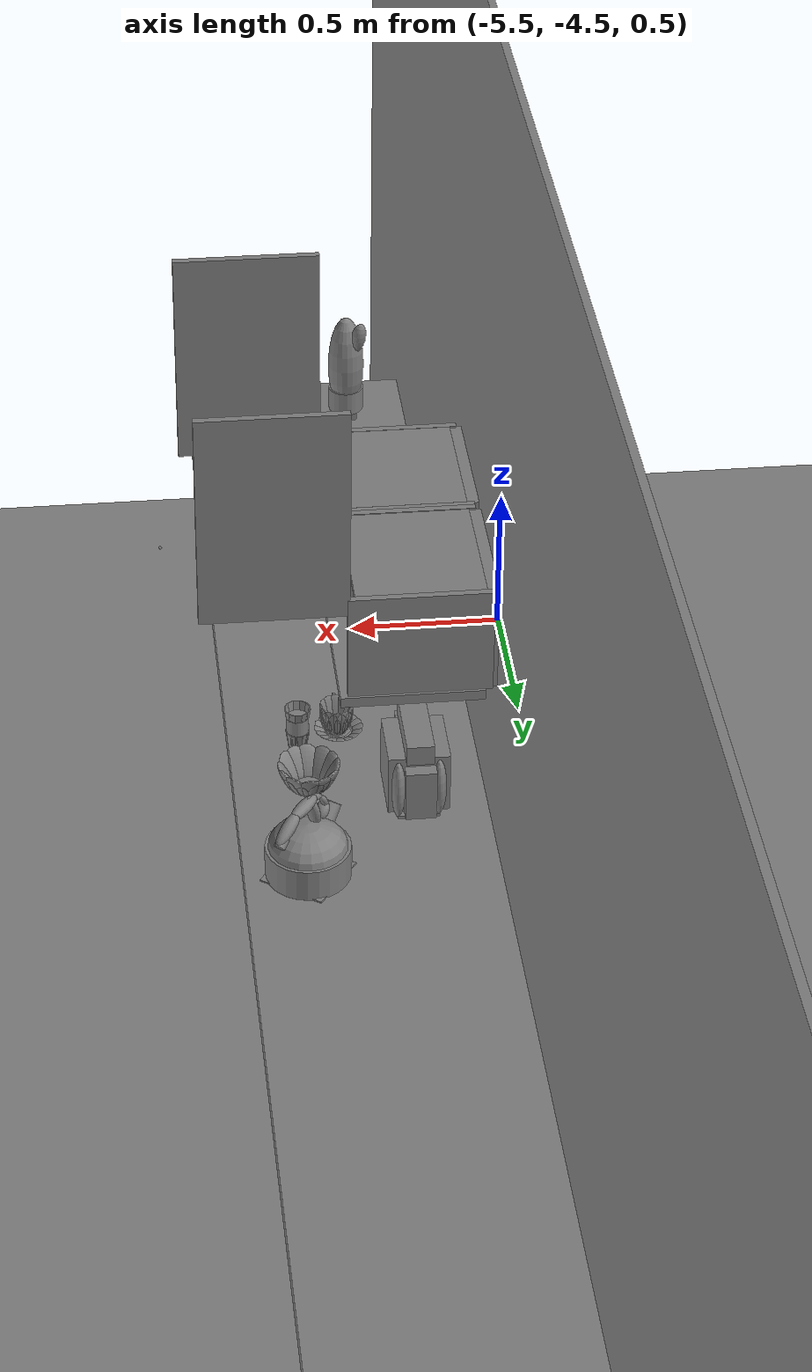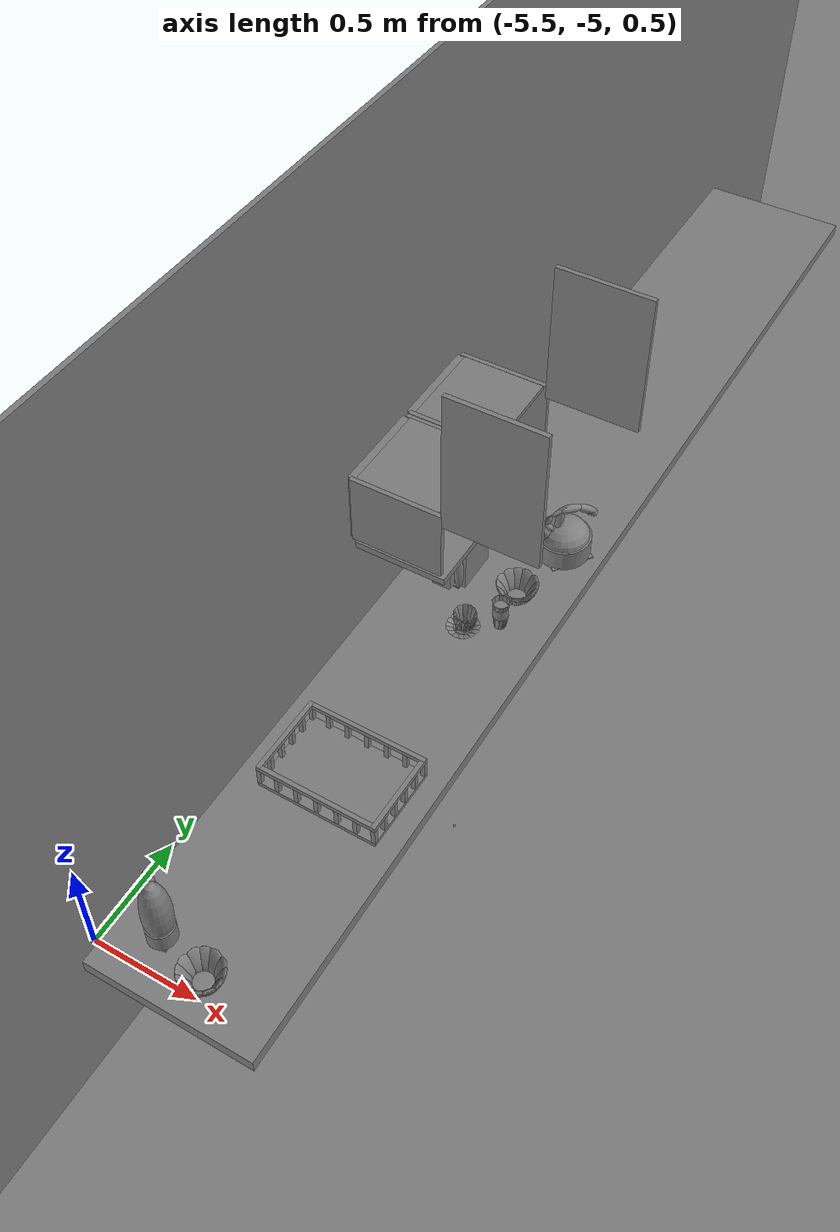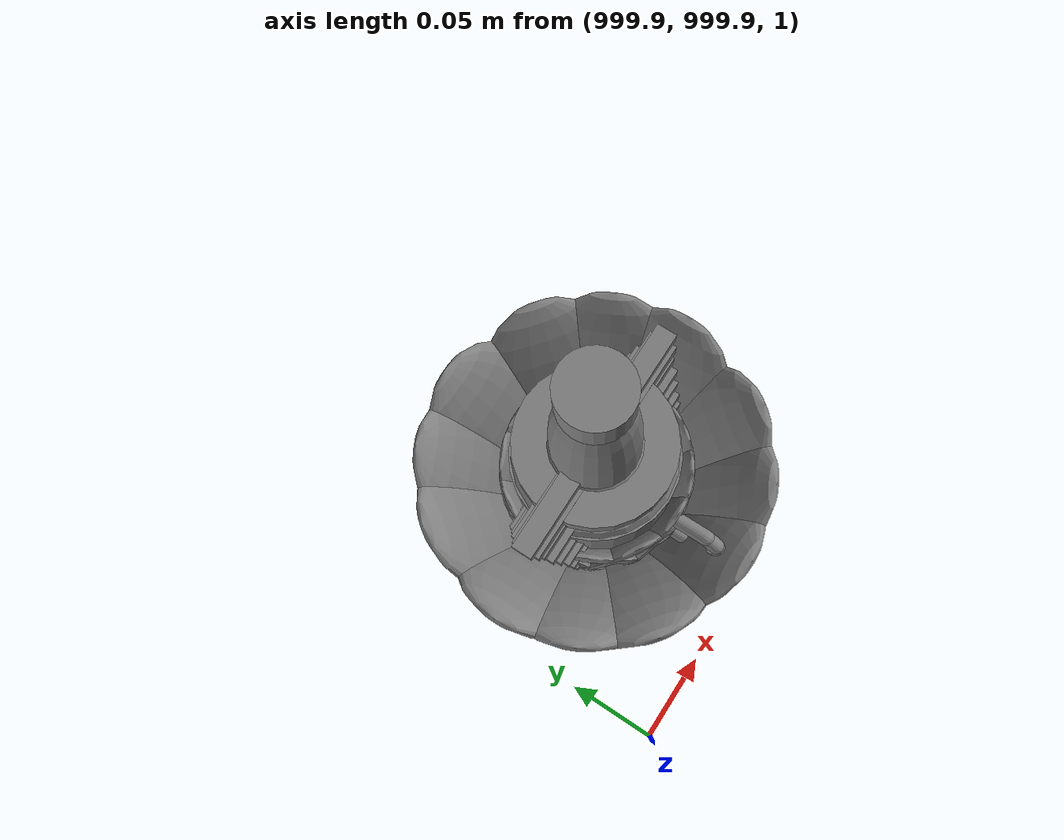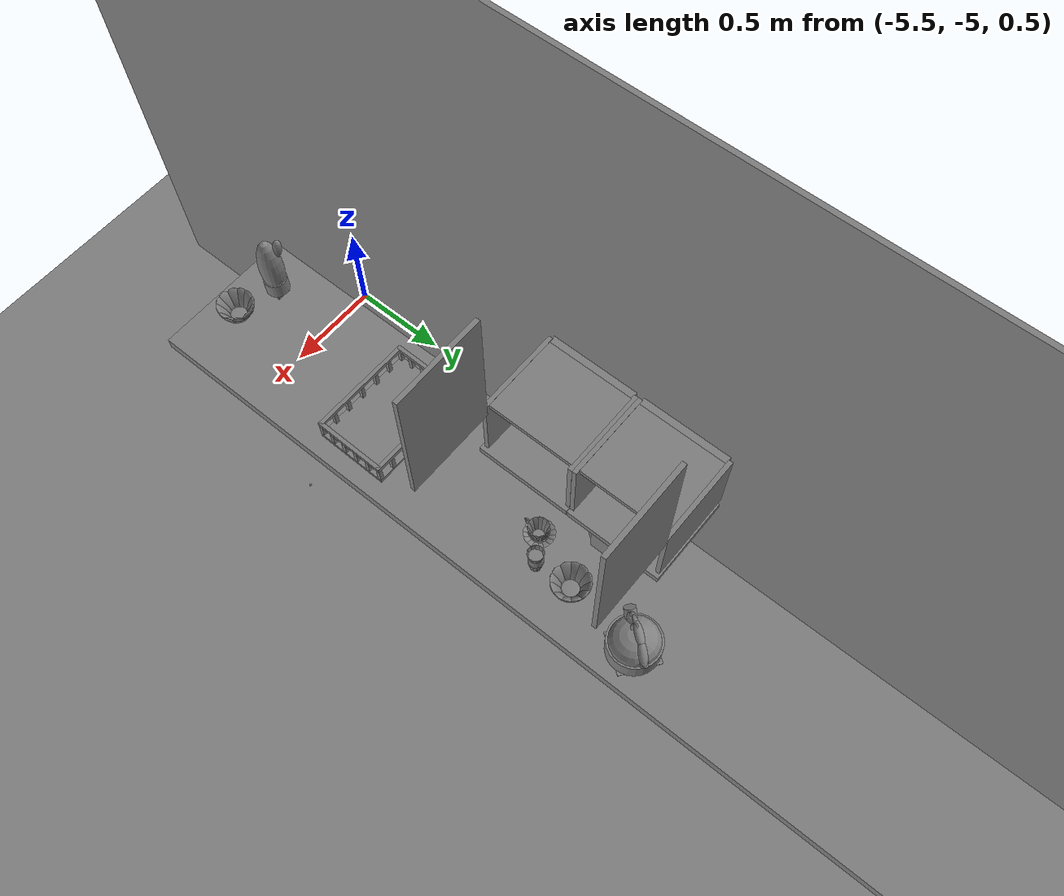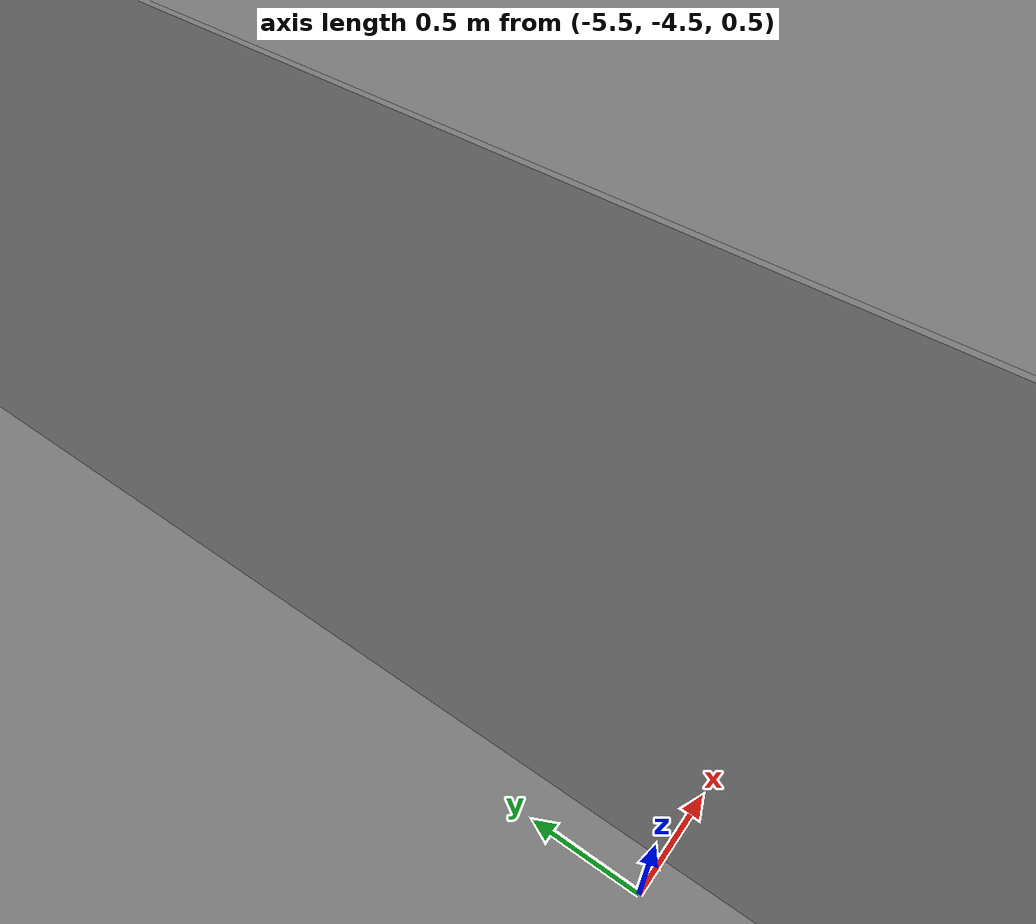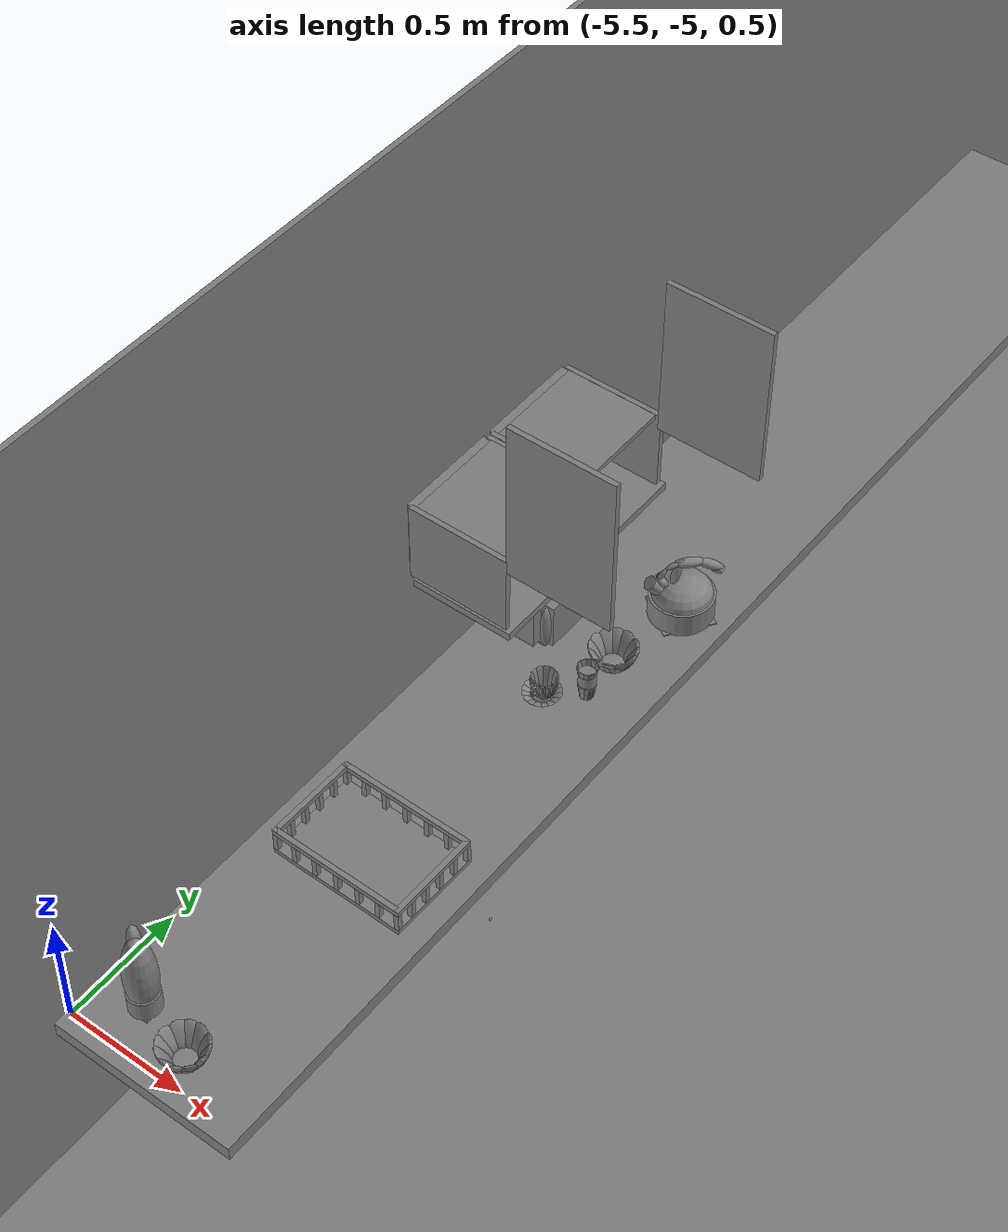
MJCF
<mujoco>
    <option gravity="0.000000000 0.000000000 -9.810000420" timestep="0.0049999999" integrator="implicitfast" density="9.8000002" viscosity="1.8000001e-05" noslip_iterations="10" iterations="100" sdf_iterations="50">
        <flag multiccd="disable"/>
    </option>
    <size memory="1000M"/>
    <compiler coordinate="local"/>
    <worldbody>
        <light cutoff="30" pos="0 1 1" dir="0 -1 -2"/>
        <light cutoff="30" pos="0 -1 1" dir="0 1 -2"/>
        <body pos="-5.020127296 -2.953741550 1.135127425" euler="89.999946594 0.000000000 0.000000000" name="Interactive Objcets_Bread">
            <geom contype="1" conaffinity="1" density="1000" type="box" material="" rgba="0.500000000 0.500000000 0.500000000 1.000000000" solimp="0.899999976 0.949999988 0.001000000" friction="1.000000000 0.005000000 0.000100000" solref="0.020000000 1.000000000" margin="0" condim="3" group="0" pos="-0.008702755 -0.017670274 -0.135069147" quat="0.707107067 -0.707106471 0.000000021 -0.000000021" size="0.045000002 0.020000000 0.079999998" name="Interactive Objcets_geom_427E4A74_3CBD_4B4E_8FCC_68924FD60D11"/>
            <geom contype="1" conaffinity="1" density="1000" type="box" material="" rgba="0.500000000 0.500000000 0.500000000 1.000000000" solimp="0.899999976 0.949999988 0.001000000" friction="1.000000000 0.005000000 0.000100000" solref="0.020000000 1.000000000" margin="0" condim="3" group="0" pos="0.033925056 -0.123201847 0.086778767" quat="0.707107067 -0.707106471 0.000000021 -0.000000021" size="0.020000000 0.020000000 0.005000000" name="Interactive Objcets_geom_8C458FEA_A3F3_457F_A63B_50A489CA7162"/>
            <geom contype="1" conaffinity="1" density="1000" type="box" material="" rgba="0.500000000 0.500000000 0.500000000 1.000000000" solimp="0.899999976 0.949999988 0.001000000" friction="1.000000000 0.005000000 0.000100000" solref="0.020000000 1.000000000" margin="0" condim="3" group="0" pos="-0.008702755 -0.016588926 0.000174277" quat="0.707107067 -0.707106471 0.000000021 -0.000000021" size="0.090000004 0.100000001 0.094999999" name="Interactive Objcets_geom_FB427E4B_EC80_4806_9F66_C6817B63FC88"/>
            <geom contype="1" conaffinity="1" density="1000" type="ellipsoid" material="" rgba="0.500000000 0.500000000 0.500000000 1.000000000" solimp="0.899999976 0.949999988 0.001000000" friction="1.000000000 0.005000000 0.000100000" solref="0.020000000 1.000000000" margin="0" condim="3" group="0" pos="-0.067312241 -0.026057482 -0.101716787" quat="0.707107067 -0.707106471 0.000000021 -0.000000021" size="0.020000000 0.029999999 0.094999999" name="Interactive Objcets_geom_834BCB65_2846_4129_BC6D_1BD658528D16"/>
            <geom contype="1" conaffinity="1" density="1000" type="ellipsoid" material="" rgba="0.500000000 0.500000000 0.500000000 1.000000000" solimp="0.899999976 0.949999988 0.001000000" friction="1.000000000 0.005000000 0.000100000" solref="0.020000000 1.000000000" margin="0" condim="3" group="0" pos="0.052222252 -0.026057363 0.101459242" quat="0.707107067 -0.707106471 0.000000021 -0.000000021" size="0.020000000 0.029999999 0.094999999" name="Interactive Objcets_geom_90999E51_609C_4CEC_B60E_30FB7CD4C4BD"/>
            <geom contype="1" conaffinity="1" density="1000" type="box" material="" rgba="0.500000000 0.500000000 0.500000000 1.000000000" solimp="0.899999976 0.949999988 0.001000000" friction="1.000000000 0.005000000 0.000100000" solref="0.020000000 1.000000000" margin="0" condim="3" group="0" pos="-0.050020695 -0.123201847 0.086778767" quat="0.707107067 -0.707106471 0.000000021 -0.000000021" size="0.020000000 0.020000000 0.005000000" name="Interactive Objcets_geom_6D9CEC2A_9E82_44F3_95EA_AD214E1B4B46"/>
            <geom contype="1" conaffinity="1" density="1000" type="box" material="" rgba="0.500000000 0.500000000 0.500000000 1.000000000" solimp="0.899999976 0.949999988 0.001000000" friction="1.000000000 0.005000000 0.000100000" solref="0.020000000 1.000000000" margin="0" condim="3" group="0" pos="0.033925056 -0.123201728 -0.092369899" quat="0.707107067 -0.707106471 0.000000021 -0.000000021" size="0.020000000 0.020000000 0.005000000" name="Interactive Objcets_geom_0D4FD246_2E4A_441F_94CC_A7A9607EA7EC"/>
            <geom contype="1" conaffinity="1" density="1000" type="ellipsoid" material="" rgba="0.500000000 0.500000000 0.500000000 1.000000000" solimp="0.899999976 0.949999988 0.001000000" friction="1.000000000 0.005000000 0.000100000" solref="0.020000000 1.000000000" margin="0" condim="3" group="0" pos="-0.069190502 -0.026057363 0.101458766" quat="0.707107067 -0.707106471 0.000000021 -0.000000021" size="0.020000000 0.029999999 0.094999999" name="Interactive Objcets_geom_ED375E82_84C4_41A1_A950_70A8341128E5"/>
            <geom contype="1" conaffinity="1" density="1000" type="box" material="" rgba="0.500000000 0.500000000 0.500000000 1.000000000" solimp="0.899999976 0.949999988 0.001000000" friction="1.000000000 0.005000000 0.000100000" solref="0.020000000 1.000000000" margin="0" condim="3" group="0" pos="-0.008702755 -0.017670155 0.134585604" quat="0.707107067 -0.707106471 0.000000021 -0.000000021" size="0.045000002 0.020000000 0.079999998" name="Interactive Objcets_geom_7403C6E5_7C22_4415_8482_48C45C3B9D43"/>
            <geom contype="1" conaffinity="1" density="1000" type="box" material="" rgba="0.500000000 0.500000000 0.500000000 1.000000000" solimp="0.899999976 0.949999988 0.001000000" friction="1.000000000 0.005000000 0.000100000" solref="0.020000000 1.000000000" margin="0" condim="3" group="0" pos="-0.050020695 -0.123201728 -0.092370376" quat="0.707107067 -0.707106471 0.000000021 -0.000000021" size="0.020000000 0.020000000 0.005000000" name="Interactive Objcets_geom_6135CE5F_0665_476D_ABFD_26FF893FDE2C"/>
            <geom contype="1" conaffinity="1" density="1000" type="box" material="" rgba="0.500000000 0.500000000 0.500000000 1.000000000" solimp="0.899999976 0.949999988 0.001000000" friction="1.000000000 0.005000000 0.000100000" solref="0.020000000 1.000000000" margin="0" condim="3" group="0" pos="-0.008702755 0.104617000 -0.003706597" quat="0.707107067 -0.707106471 0.000000021 -0.000000021" size="0.039999999 0.119999997 0.030999999" name="Interactive Objcets_geom_88380EA1_30AF_418C_8C01_3549F63F8886"/>
            <geom contype="1" conaffinity="1" density="1000" type="ellipsoid" material="" rgba="0.500000000 0.500000000 0.500000000 1.000000000" solimp="0.899999976 0.949999988 0.001000000" friction="1.000000000 0.005000000 0.000100000" solref="0.020000000 1.000000000" margin="0" condim="3" group="0" pos="0.052222252 -0.026057243 -0.106481344" quat="0.707107067 -0.707106471 0.000000021 -0.000000021" size="0.020000000 0.029999999 0.094999999" name="Interactive Objcets_geom_059C61B6_30FC_4801_9AC5_235D823680D2"/>
            <freejoint name="Interactive Objcets_Bread"/>
        </body>
        <body pos="-4.282498837 -4.350724697 1.855287910" euler="129.090820312 28.496440887 -144.343582153" mocap="true" name="spotlight2_SpotLight"/>
        <body pos="1000.000000000 1000.000000000 1.000000000" euler="0.000000000 0.000000000 0.000000000" name="openloong_gripper_2f85_fix_base_usda_salt">
            <geom contype="1" conaffinity="1" density="1000" type="box" material="" rgba="0.500000000 0.500000000 0.500000000 1.000000000" solimp="0.899999976 0.949999988 0.001000000" friction="1.000000000 0.005000000 0.000100000" solref="0.020000000 1.000000000" margin="0" condim="3" group="0" pos="0.000305176 0.000000000 0.084862232" quat="1.000000000 0.000000000 0.000000000 0.000000000" size="0.048999999 0.018999999 0.005000000" name="openloong_gripper_2f85_fix_base_usda_geom_000E7B08_5FFD_4D42_8170_51E9E67B4976"/>
            <geom contype="1" conaffinity="1" density="1000" type="box" material="" rgba="0.500000000 0.500000000 0.500000000 1.000000000" solimp="0.899999976 0.949999988 0.001000000" friction="1.000000000 0.005000000 0.000100000" solref="0.020000000 1.000000000" margin="0" condim="3" group="0" pos="0.000305176 0.000000000 0.104564309" quat="1.000000000 0.000000000 0.000000000 0.000000000" size="0.052000001 0.014000000 0.005000000" name="openloong_gripper_2f85_fix_base_usda_geom_B8627131_5F7E_4F3E_88E3_4B6A73B3106A"/>
            <geom contype="1" conaffinity="1" density="1000" type="box" material="" rgba="0.500000000 0.500000000 0.500000000 1.000000000" solimp="0.899999976 0.949999988 0.001000000" friction="1.000000000 0.005000000 0.000100000" solref="0.020000000 1.000000000" margin="0" condim="3" group="0" pos="0.000305176 0.000000000 0.114487171" quat="1.000000000 0.000000000 0.000000000 0.000000000" size="0.054000001 0.011500000 0.005000000" name="openloong_gripper_2f85_fix_base_usda_geom_67E030AD_C95B_44AF_9085_FA3A7EEF22C1"/>
            <geom contype="1" conaffinity="1" density="1000" type="box" material="" rgba="0.500000000 0.500000000 0.500000000 1.000000000" solimp="0.899999976 0.949999988 0.001000000" friction="1.000000000 0.005000000 0.000100000" solref="0.020000000 1.000000000" margin="0" condim="3" group="0" pos="0.000305176 0.000000000 0.075103164" quat="1.000000000 0.000000000 0.000000000 0.000000000" size="0.048000000 0.020000000 0.005000000" name="openloong_gripper_2f85_fix_base_usda_geom_9F527359_A72E_47EA_9BAA_2CF808B731BD"/>
            <geom contype="1" conaffinity="1" density="1000" type="box" material="" rgba="0.500000000 0.500000000 0.500000000 1.000000000" solimp="0.899999976 0.949999988 0.001000000" friction="1.000000000 0.005000000 0.000100000" solref="0.020000000 1.000000000" margin="0" condim="3" group="0" pos="0.000305176 0.000000000 0.134892464" quat="1.000000000 0.000000000 0.000000000 0.000000000" size="0.057000000 0.007000000 0.005000000" name="openloong_gripper_2f85_fix_base_usda_geom_C7A13490_C9FD_46E5_AF39_06C9ED1C0B04"/>
            <geom contype="1" conaffinity="1" density="1000" type="box" material="" rgba="0.500000000 0.500000000 0.500000000 1.000000000" solimp="0.899999976 0.949999988 0.001000000" friction="1.000000000 0.005000000 0.000100000" solref="0.020000000 1.000000000" margin="0" condim="3" group="0" pos="0.000305176 0.000000000 0.094920278" quat="1.000000000 0.000000000 0.000000000 0.000000000" size="0.050000001 0.017000001 0.005000000" name="openloong_gripper_2f85_fix_base_usda_geom_01469B99_1290_4181_9B43_2277B7B6EF83"/>
            <geom contype="1" conaffinity="1" density="1000" type="box" material="" rgba="0.500000000 0.500000000 0.500000000 1.000000000" solimp="0.899999976 0.949999988 0.001000000" friction="1.000000000 0.005000000 0.000100000" solref="0.020000000 1.000000000" margin="0" condim="3" group="0" pos="0.000305176 0.000000000 0.065204859" quat="1.000000000 0.000000000 0.000000000 0.000000000" size="0.045000002 0.021000000 0.005000000" name="openloong_gripper_2f85_fix_base_usda_geom_72A7126E_478F_44A3_A4BC_AA962C39B497"/>
            <geom contype="1" conaffinity="1" density="1000" type="box" material="" rgba="0.500000000 0.500000000 0.500000000 1.000000000" solimp="0.899999976 0.949999988 0.001000000" friction="1.000000000 0.005000000 0.000100000" solref="0.020000000 1.000000000" margin="0" condim="3" group="0" pos="0.000305176 0.000000000 0.144135714" quat="1.000000000 0.000000000 0.000000000 0.000000000" size="0.059000000 0.005000000 0.004000000" name="openloong_gripper_2f85_fix_base_usda_geom_22055BCC_20E0_4773_AE75_C28439511424"/>
            <geom contype="1" conaffinity="1" density="1000" type="box" material="" rgba="0.500000000 0.500000000 0.500000000 1.000000000" solimp="0.899999976 0.949999988 0.001000000" friction="1.000000000 0.005000000 0.000100000" solref="0.020000000 1.000000000" margin="0" condim="3" group="0" pos="0.000000000 0.000000000 0.031593561" quat="1.000000000 0.000000000 0.000000000 0.000000000" size="0.041999999 0.024000000 0.029999999" name="openloong_gripper_2f85_fix_base_usda_geom_38ED07A8_DC2D_4F0E_BF64_32EFFC150CB4"/>
            <geom contype="1" conaffinity="1" density="1000" type="box" material="" rgba="0.500000000 0.500000000 0.500000000 1.000000000" solimp="0.899999976 0.949999988 0.001000000" friction="1.000000000 0.005000000 0.000100000" solref="0.020000000 1.000000000" margin="0" condim="3" group="0" pos="0.000305176 0.000000000 0.124608755" quat="1.000000000 0.000000000 0.000000000 0.000000000" size="0.055000000 0.008000000 0.005000000" name="openloong_gripper_2f85_fix_base_usda_geom_77D09921_6C18_46C7_9535_7CB1A5918926"/>
            <freejoint name="openloong_gripper_2f85_fix_base_usda_salt_joint"/>
            <site size="0.005000000 0.005000000 0.005000000" rgba="0.500000000 0.500000000 0.500000000 1.000000000" pos="0.000000000 0.000000000 0.000000000" quat="1.000000000 0.000000000 0.000000000 0.000000000" group="0" type="sphere" name="openloong_gripper_2f85_fix_base_usda_saltsite"/>
        </body>
        <body pos="-4.442990303 -4.528850555 1.723151326" euler="-3.939397573 -62.452247620 143.732254028" mocap="true" name="spotlight5_SpotLight"/>
        <body pos="1000.000000000 1000.000000000 1.000000000" euler="0.000000000 0.000000000 0.000000000" name="openloong_gripper_2f85_fix_base_usda_coffeecup_white_kps">
            <geom contype="1" conaffinity="1" density="1000" type="capsule" material="" rgba="0.500000000 0.500000000 0.500000000 1.000000000" solimp="0.899999976 0.949999988 0.001000000" friction="1.000000000 0.005000000 0.000100000" solref="0.020000000 1.000000000" margin="0" condim="3" group="0" pos="-0.000854492 -0.065795898 0.050029993" quat="0.343559504 -0.613204718 0.626912475 0.336047262" size="0.004000000 0.005000000 1.000000000" name="openloong_gripper_2f85_fix_base_usda_geom_32F07F72_9E27_4F5E_AAD3_F5E870E53359"/>
            <geom contype="1" conaffinity="1" density="1000" type="ellipsoid" material="" rgba="0.500000000 0.500000000 0.500000000 1.000000000" solimp="0.899999976 0.949999988 0.001000000" friction="1.000000000 0.005000000 0.000100000" solref="0.020000000 1.000000000" margin="0" condim="3" group="0" pos="-0.000793457 -0.038452148 0.048040152" quat="0.711656272 0.066323131 -0.067805752 0.696095467" size="0.005000000 0.029999999 0.048999999" name="openloong_gripper_2f85_fix_base_usda_geom_966DDD2F_E4D4_4384_8E3A_48FED12A1EC5"/>
            <geom contype="1" conaffinity="1" density="1000" type="ellipsoid" material="" rgba="0.500000000 0.500000000 0.500000000 1.000000000" solimp="0.899999976 0.949999988 0.001000000" friction="1.000000000 0.005000000 0.000100000" solref="0.020000000 1.000000000" margin="0" condim="3" group="0" pos="0.037719727 -0.001892090 0.048040152" quat="0.995387912 0.001371633 0.094835162 -0.014391154" size="0.005000000 0.029999999 0.048999999" name="openloong_gripper_2f85_fix_base_usda_geom_0D797F6C_6DFC_4CFE_A903_E8023732F3F6"/>
            <geom contype="1" conaffinity="1" density="1000" type="ellipsoid" material="" rgba="0.500000000 0.500000000 0.500000000 1.000000000" solimp="0.899999976 0.949999988 0.001000000" friction="1.000000000 0.005000000 0.000100000" solref="0.020000000 1.000000000" margin="0" condim="3" group="0" pos="0.033996582 0.015502930 0.048040152" quat="0.970659733 -0.021051638 0.092478797 0.220962167" size="0.005000000 0.029999999 0.048999999" name="openloong_gripper_2f85_fix_base_usda_geom_A02F28B9_2ECD_464A_82FE_0EBD9A374373"/>
            <geom contype="1" conaffinity="1" density="1000" type="box" material="" rgba="0.500000000 0.500000000 0.500000000 1.000000000" solimp="0.899999976 0.949999988 0.001000000" friction="1.000000000 0.005000000 0.000100000" solref="0.020000000 1.000000000" margin="0" condim="3" group="0" pos="0.000793457 -0.000183105 0.000156164" quat="0.714879215 0.000000000 0.000000000 0.699247897" size="0.020000000 0.020000000 0.002000000" name="openloong_gripper_2f85_fix_base_usda_geom_2D3F6C4F_D1CB_406E_9EA3_68F01978F544"/>
            <geom contype="1" conaffinity="1" density="1000" type="ellipsoid" material="" rgba="0.500000000 0.500000000 0.500000000 1.000000000" solimp="0.899999976 0.949999988 0.001000000" friction="1.000000000 0.005000000 0.000100000" solref="0.020000000 1.000000000" margin="0" condim="3" group="0" pos="-0.019409180 -0.033081055 0.048040152" quat="0.866879702 0.046630561 -0.082595348 0.489411235" size="0.005000000 0.029999999 0.048999999" name="openloong_gripper_2f85_fix_base_usda_geom_6AB61FEB_FB5F_4C41_AF17_E6E9168B9096"/>
            <geom contype="1" conaffinity="1" density="1000" type="ellipsoid" material="" rgba="0.500000000 0.500000000 0.500000000 1.000000000" solimp="0.899999976 0.949999988 0.001000000" friction="1.000000000 0.005000000 0.000100000" solref="0.020000000 1.000000000" margin="0" condim="3" group="0" pos="-0.016052246 0.033264160 0.048040152" quat="0.840792537 -0.050782297 -0.080109790 -0.532983541" size="0.005000000 0.029999999 0.048999999" name="openloong_gripper_2f85_fix_base_usda_geom_7B91CB6C_1C95_42C2_8408_7D37901EABE8"/>
            <geom contype="1" conaffinity="1" density="1000" type="capsule" material="" rgba="0.500000000 0.500000000 0.500000000 1.000000000" solimp="0.899999976 0.949999988 0.001000000" friction="1.000000000 0.005000000 0.000100000" solref="0.020000000 1.000000000" margin="0" condim="3" group="0" pos="-0.000549316 -0.053527832 0.046825886" quat="0.505496025 -0.494442940 0.505495846 0.494442940" size="0.004000000 0.005000000 1.000000000" name="openloong_gripper_2f85_fix_base_usda_geom_CF979B54_81C9_45F7_AE07_DF8D6558EA42"/>
            <geom contype="1" conaffinity="1" density="1000" type="ellipsoid" material="" rgba="0.500000000 0.500000000 0.500000000 1.000000000" solimp="0.899999976 0.949999988 0.001000000" friction="1.000000000 0.005000000 0.000100000" solref="0.020000000 1.000000000" margin="0" condim="3" group="0" pos="-0.032104492 0.018920898 0.048040152" quat="0.958129764 -0.025742561 -0.091288343 -0.270168930" size="0.005000000 0.029999999 0.048999999" name="openloong_gripper_2f85_fix_base_usda_geom_07904978_25A5_4559_8E50_69EBDFEF9FDD"/>
            <geom contype="1" conaffinity="1" density="1000" type="ellipsoid" material="" rgba="0.500000000 0.500000000 0.500000000 1.000000000" solimp="0.899999976 0.949999988 0.001000000" friction="1.000000000 0.005000000 0.000100000" solref="0.020000000 1.000000000" margin="0" condim="3" group="0" pos="-0.037597656 0.000305176 0.048040152" quat="0.995387554 -0.001371440 -0.094839431 -0.014389008" size="0.005000000 0.029999999 0.048999999" name="openloong_gripper_2f85_fix_base_usda_geom_9B88FC1E_C3F2_4ED1_82A9_208B9370A615"/>
            <geom contype="1" conaffinity="1" density="1000" type="capsule" material="" rgba="0.500000000 0.500000000 0.500000000 1.000000000" solimp="0.899999976 0.949999988 0.001000000" friction="1.000000000 0.005000000 0.000100000" solref="0.020000000 1.000000000" margin="0" condim="3" group="0" pos="-0.000366211 -0.043762207 0.044118762" quat="0.260488123 -0.651174724 0.665731549 0.254792154" size="0.004000000 0.003000000 1.000000000" name="openloong_gripper_2f85_fix_base_usda_geom_FFB7EA6C_9F3F_40CA_8ADF_E6AF1BD663E3"/>
            <geom contype="1" conaffinity="1" density="1000" type="capsule" material="" rgba="0.500000000 0.500000000 0.500000000 1.000000000" solimp="0.899999976 0.949999988 0.001000000" friction="1.000000000 0.005000000 0.000100000" solref="0.020000000 1.000000000" margin="0" condim="3" group="0" pos="-0.000915527 -0.068542480 0.082936406" quat="0.624995589 -0.339446366 0.347034454 0.611329615" size="0.004000000 0.004000000 1.000000000" name="openloong_gripper_2f85_fix_base_usda_geom_A38B13B0_8FFC_42E5_B2D0_7A3646DB6F28"/>
            <geom contype="1" conaffinity="1" density="1000" type="ellipsoid" material="" rgba="0.500000000 0.500000000 0.500000000 1.000000000" solimp="0.899999976 0.949999988 0.001000000" friction="1.000000000 0.005000000 0.000100000" solref="0.020000000 1.000000000" margin="0" condim="3" group="0" pos="0.016113281 -0.034851074 0.048040152" quat="0.840793252 0.050779939 0.080106191 -0.532983422" size="0.005000000 0.029999999 0.048999999" name="openloong_gripper_2f85_fix_base_usda_geom_A50ECCB6_2F88_4A08_8BA9_69FB15C33163"/>
            <geom contype="1" conaffinity="1" density="1000" type="ellipsoid" material="" rgba="0.500000000 0.500000000 0.500000000 1.000000000" solimp="0.899999976 0.949999988 0.001000000" friction="1.000000000 0.005000000 0.000100000" solref="0.020000000 1.000000000" margin="0" condim="3" group="0" pos="0.000854492 0.036865234 0.048040152" quat="0.711656570 -0.066320375 0.067802906 0.696095705" size="0.005000000 0.029999999 0.048999999" name="openloong_gripper_2f85_fix_base_usda_geom_253A3DD7_C768_4AE7_94B9_2D9B9FD837FA"/>
            <geom contype="1" conaffinity="1" density="1000" type="ellipsoid" material="" rgba="0.500000000 0.500000000 0.500000000 1.000000000" solimp="0.899999976 0.949999988 0.001000000" friction="1.000000000 0.005000000 0.000100000" solref="0.020000000 1.000000000" margin="0" condim="3" group="0" pos="-0.033935547 -0.017089844 0.048040152" quat="0.970659137 0.021052625 -0.092483103 0.220962465" size="0.005000000 0.029999999 0.048999999" name="openloong_gripper_2f85_fix_base_usda_geom_7E37E352_5D82_415F_AB8D_7269F6E80C40"/>
            <geom contype="1" conaffinity="1" density="1000" type="ellipsoid" material="" rgba="0.500000000 0.500000000 0.500000000 1.000000000" solimp="0.899999976 0.949999988 0.001000000" friction="1.000000000 0.005000000 0.000100000" solref="0.020000000 1.000000000" margin="0" condim="3" group="0" pos="0.019531250 0.031494141 0.048040152" quat="0.866880119 -0.046628602 0.082591817 0.489411235" size="0.005000000 0.029999999 0.048999999" name="openloong_gripper_2f85_fix_base_usda_geom_0F3DF140_6914_4276_BD67_2A9BD51C1ED5"/>
            <geom contype="1" conaffinity="1" density="1000" type="ellipsoid" material="" rgba="0.500000000 0.500000000 0.500000000 1.000000000" solimp="0.899999976 0.949999988 0.001000000" friction="1.000000000 0.005000000 0.000100000" solref="0.020000000 1.000000000" margin="0" condim="3" group="0" pos="0.032165527 -0.020507812 0.048040152" quat="0.958128154 0.025740955 0.091285400 -0.270175666" size="0.005000000 0.029999999 0.048999999" name="openloong_gripper_2f85_fix_base_usda_geom_7F8AC3EC_0EE8_4775_BA43_8443C4EF452E"/>
            <geom contype="1" conaffinity="1" density="1000" type="capsule" material="" rgba="0.500000000 0.500000000 0.500000000 1.000000000" solimp="0.899999976 0.949999988 0.001000000" friction="1.000000000 0.005000000 0.000100000" solref="0.020000000 1.000000000" margin="0" condim="3" group="0" pos="-0.000610352 -0.056823730 0.083572865" quat="0.452654332 -0.541215360 0.553313971 0.442756712" size="0.004000000 0.009000000 1.000000000" name="openloong_gripper_2f85_fix_base_usda_geom_17518375_7A75_42BB_B37E_9417E2C49078"/>
            <geom contype="1" conaffinity="1" density="1000" type="ellipsoid" material="" rgba="0.500000000 0.500000000 0.500000000 1.000000000" solimp="0.899999976 0.949999988 0.001000000" friction="1.000000000 0.005000000 0.000100000" solref="0.020000000 1.000000000" margin="0" condim="3" group="0" pos="0.000061035 -0.000183105 0.001848221" quat="0.714879215 0.000000000 0.000000000 0.699247897" size="0.029999999 0.029999999 0.001000000" name="openloong_gripper_2f85_fix_base_usda_geom_BFA5E6CE_8D40_45C5_BC34_3FADEB346EB5"/>
            <geom contype="1" conaffinity="1" density="1000" type="capsule" material="" rgba="0.500000000 0.500000000 0.500000000 1.000000000" solimp="0.899999976 0.949999988 0.001000000" friction="1.000000000 0.005000000 0.000100000" solref="0.020000000 1.000000000" margin="0" condim="3" group="0" pos="-0.000976562 -0.071838379 0.066101432" quat="0.031849027 -0.698553741 0.714169443 0.031152546" size="0.004000000 0.012000000 1.000000000" name="openloong_gripper_2f85_fix_base_usda_geom_5603D9BA_875D_4446_8CE0_C126B13F07C3"/>
            <freejoint name="openloong_gripper_2f85_fix_base_usda_coffeecup_white_kps_joint"/>
            <site size="0.005000000 0.005000000 0.005000000" rgba="0.500000000 0.500000000 0.500000000 1.000000000" pos="0.000000000 0.000000000 0.000000000" quat="0.999961913 0.008726534 0.000000000 0.000000000" group="0" type="sphere" name="openloong_gripper_2f85_fix_base_usda_coffeecup_white_kps"/>
        </body>
        <body pos="0.000000000 0.000000000 0.000000000" euler="0.000000000 0.000000000 0.000000000" name="Static Objcets_Static Objcets">
            <geom contype="1" conaffinity="1" density="1000" type="box" material="" rgba="0.500000000 0.500000000 0.500000000 1.000000000" solimp="0.899999976 0.949999988 0.001000000" friction="1.000000000 0.005000000 0.000100000" solref="0.020000000 1.000000000" margin="0" condim="3" group="0" pos="-5.189302921 -3.293644905 1.760152459" quat="0.707107067 0.707106471 0.000000000 0.000000000" size="0.025000000 0.159999996 0.200000003" name="Static Objcets_geom_D67D7CFD_58C2_400B_99E4_0C4AFB34FC67"/>
            <geom contype="1" conaffinity="1" density="1000" type="box" material="" rgba="0.500000000 0.500000000 0.500000000 1.000000000" solimp="0.899999976 0.949999988 0.001000000" friction="1.000000000 0.005000000 0.000100000" solref="0.020000000 1.000000000" margin="0" condim="3" group="0" pos="-4.999745846 -3.497932911 1.764780521" quat="0.707107067 0.707106471 0.000000000 0.000000000" size="0.200000003 0.159999996 0.010000000" name="Static Objcets_geom_5EEF8E38_6259_4DC5_9B7F_F2707AC1FF9A"/>
            <geom contype="1" conaffinity="1" density="1000" type="box" material="" rgba="0.500000000 0.500000000 0.500000000 1.000000000" solimp="0.899999976 0.949999988 0.001000000" friction="1.000000000 0.005000000 0.000100000" solref="0.020000000 1.000000000" margin="0" condim="3" group="0" pos="-4.979488373 -3.297635794 1.591412544" quat="0.707106829 0.707106709 0.000000000 0.000000000" size="0.200000003 0.015000000 0.219999999" name="Static Objcets_geom_1FD5B72D_3A08_4FFA_83F0_751D1B8C9083"/>
            <geom contype="1" conaffinity="1" density="1000" type="box" material="" rgba="0.500000000 0.500000000 0.500000000 1.000000000" solimp="0.899999976 0.949999988 0.001000000" friction="1.000000000 0.005000000 0.000100000" solref="0.020000000 1.000000000" margin="0" condim="3" group="0" pos="-4.999745846 -3.087441683 1.763863802" quat="0.707107067 0.707106471 0.000000000 0.000000000" size="0.200000003 0.159999996 0.010000000" name="Static Objcets_geom_79BE0872_75B5_4FB9_A458_115120DD3152"/>
            <geom contype="1" conaffinity="1" density="1000" type="box" material="" rgba="0.500000000 0.500000000 0.500000000 1.000000000" solimp="0.899999976 0.949999988 0.001000000" friction="1.000000000 0.005000000 0.000100000" solref="0.020000000 1.000000000" margin="0" condim="3" group="0" pos="-5.000125408 -3.294431210 1.913951039" quat="0.707107067 0.707106471 0.000000000 0.000000000" size="0.180000007 0.010000000 0.200000003" name="Static Objcets_geom_03E990E1_3528_455C_BECA_153526721660"/>
            <geom contype="1" conaffinity="1" density="1000" type="box" material="" rgba="0.500000000 0.500000000 0.500000000 1.000000000" solimp="0.899999976 0.949999988 0.001000000" friction="1.000000000 0.005000000 0.000100000" solref="0.020000000 1.000000000" margin="0" condim="3" group="0" pos="-4.873187065 -2.461376429 0.977675021" quat="0.707107067 0.707106471 0.000000000 0.000000000" size="0.370000005 0.029999999 2.799999952" name="Static Objcets_geom_DC3A76E2_CE52_4164_8BF7_E46CB2956466"/>
            <geom contype="1" conaffinity="1" density="1000" type="box" material="" rgba="0.500000000 0.500000000 0.500000000 1.000000000" solimp="0.899999976 0.949999988 0.001000000" friction="1.000000000 0.005000000 0.000100000" solref="0.020000000 1.000000000" margin="0" condim="3" group="0" pos="-5.244853973 -2.375543594 1.820221663" quat="0.707107008 0.707106531 0.000000000 0.000000000" size="0.010000000 1.500000000 3.700000048" name="Static Objcets_geom_7B15BC0C_B958_4A2A_94BF_3E08B56BD7B5"/>
            <geom contype="1" conaffinity="1" density="1000" type="box" material="" rgba="0.500000000 0.500000000 0.500000000 1.000000000" solimp="0.899999976 0.949999988 0.001000000" friction="1.000000000 0.005000000 0.000100000" solref="0.020000000 1.000000000" margin="0" condim="3" group="0" pos="-0.720102787 0.222944975 -1.102830648" quat="0.000000954 1.000000000 0.000000000 0.000000000" size="8.000000000 8.000000000 0.010000000" name="Static Objcets_geom_C8AEA0DD_3CC8_4501_8297_4DA337F4729E"/>
            <geom contype="1" conaffinity="1" density="1000" type="box" material="" rgba="0.500000000 0.500000000 0.500000000 1.000000000" solimp="0.899999976 0.949999988 0.001000000" friction="1.000000000 0.005000000 0.000100000" solref="0.020000000 1.000000000" margin="0" condim="3" group="0" pos="-4.999745846 -2.653569937 1.764779806" quat="0.707107067 0.707106471 0.000000000 0.000000000" size="0.200000003 0.159999996 0.010000000" name="Static Objcets_geom_6B1D823E_E07B_49AA_B6C9_C251ACB2D0EC"/>
            <geom contype="1" conaffinity="1" density="1000" type="box" material="" rgba="0.500000000 0.500000000 0.500000000 1.000000000" solimp="0.899999976 0.949999988 0.001000000" friction="1.000000000 0.005000000 0.000100000" solref="0.020000000 1.000000000" margin="0" condim="3" group="0" pos="-5.000125408 -2.861802340 1.913950682" quat="0.707107067 0.707106471 0.000000000 0.000000000" size="0.180000007 0.010000000 0.200000003" name="Static Objcets_geom_DD4760A0_7893_4570_B88C_94F0B7372272"/>
            <geom contype="1" conaffinity="1" density="1000" type="box" material="" rgba="0.500000000 0.500000000 0.500000000 1.000000000" solimp="0.899999976 0.949999988 0.001000000" friction="1.000000000 0.005000000 0.000100000" solref="0.020000000 1.000000000" margin="0" condim="3" group="0" pos="-5.189302921 -2.861564636 1.760152102" quat="0.707107067 0.707106471 0.000000000 0.000000000" size="0.025000000 0.159999996 0.200000003" name="Static Objcets_geom_F656C363_F4A7_4FF4_A1C8_EF99080BB33F"/>
            <geom contype="1" conaffinity="1" density="1000" type="box" material="" rgba="0.500000000 0.500000000 0.500000000 1.000000000" solimp="0.899999976 0.949999988 0.001000000" friction="1.000000000 0.005000000 0.000100000" solref="0.020000000 1.000000000" margin="0" condim="3" group="0" pos="-4.979488373 -2.855390549 1.591412187" quat="0.707106709 0.707106769 0.000000000 0.000000000" size="0.200000003 0.015000000 0.219999999" name="Static Objcets_geom_4A005289_69F2_4483_8574_A93C8DFC5630"/>
            <geom contype="1" conaffinity="1" density="1000" type="box" material="" rgba="0.500000000 0.500000000 0.500000000 1.000000000" solimp="0.899999976 0.949999988 0.001000000" friction="1.000000000 0.005000000 0.000100000" solref="0.020000000 1.000000000" margin="0" condim="3" group="0" pos="-4.999745846 -3.066934109 1.765979409" quat="0.707107067 0.707106471 0.000000000 0.000000000" size="0.200000003 0.159999996 0.010000000" name="Static Objcets_geom_0BFA28EB_D040_491B_BC6F_566A3A9EB88D"/>
        </body>
        <body pos="-4.705342293 -3.169416904 1.103703976" euler="0.000000000 0.000000000 0.000000000" name="Interactive Objcets_cup_02">
            <geom contype="1" conaffinity="1" density="1000" type="box" material="" rgba="0.500000000 0.500000000 0.500000000 1.000000000" solimp="0.899999976 0.949999988 0.001000000" friction="1.000000000 0.005000000 0.000100000" solref="0.020000000 1.000000000" margin="0" condim="3" group="0" pos="0.022285938 0.016949892 -0.037281752" quat="0.893179297 -0.070051625 0.034732576 -0.442851186" size="0.010000000 0.001000000 0.035000000" name="Interactive Objcets_geom_467C7E0A_7A79_49D3_A1E9_4607DB894399"/>
            <geom contype="1" conaffinity="1" density="1000" type="box" material="" rgba="0.500000000 0.500000000 0.500000000 1.000000000" solimp="0.899999976 0.949999988 0.001000000" friction="1.000000000 0.005000000 0.000100000" solref="0.020000000 1.000000000" margin="0" condim="3" group="0" pos="0.034549713 0.000000000 0.062637210" quat="0.704941988 -0.055288255 0.055288251 -0.704942048" size="0.010000000 0.001000000 0.015000000" name="Interactive Objcets_geom_DC5EFC52_2D9A_46A0_8805_1C4DE1700813"/>
            <geom contype="1" conaffinity="1" density="1000" type="box" material="" rgba="0.500000000 0.500000000 0.500000000 1.000000000" solimp="0.899999976 0.949999988 0.001000000" friction="1.000000000 0.005000000 0.000100000" solref="0.020000000 1.000000000" margin="0" condim="3" group="0" pos="0.029378891 -0.018181801 0.062637210" quat="0.870895982 0.068302706 0.038053915 0.485208035" size="0.010000000 0.001000000 0.015000000" name="Interactive Objcets_geom_B7556CC8_5D0F_45A5_B6AF_155650E85727"/>
            <geom contype="1" conaffinity="1" density="1000" type="box" material="" rgba="0.500000000 0.500000000 0.500000000 1.000000000" solimp="0.899999976 0.949999988 0.001000000" friction="1.000000000 0.005000000 0.000100000" solref="0.020000000 1.000000000" margin="0" condim="3" group="0" pos="0.000000000 -0.034549713 0.062637210" quat="0.996938646 0.078187965 0.000000000 0.000000000" size="0.010000000 0.001000000 0.015000000" name="Interactive Objcets_geom_1DBC1D47_191F_479C_BD12_FDF5AE33D49B"/>
            <geom contype="1" conaffinity="1" density="1000" type="cylinder" material="" rgba="0.500000000 0.500000000 0.500000000 1.000000000" solimp="0.899999976 0.949999988 0.001000000" friction="1.000000000 0.005000000 0.000100000" solref="0.020000000 1.000000000" margin="0" condim="3" group="0" pos="0.000000000 0.000000000 0.022491097" quat="1.000000000 0.000000030 0.000000000 0.000000000" size="0.033000000 0.025000000 1.000000000" name="Interactive Objcets_geom_198DC10F_520C_41CC_AF57_29F729127F91"/>
            <geom contype="1" conaffinity="1" density="1000" type="box" material="" rgba="0.500000000 0.500000000 0.500000000 1.000000000" solimp="0.899999976 0.949999988 0.001000000" friction="1.000000000 0.005000000 0.000100000" solref="0.020000000 1.000000000" margin="0" condim="3" group="0" pos="0.000000000 0.034549713 0.062637210" quat="0.996938646 -0.078187965 0.000000000 0.000000000" size="0.010000000 0.001000000 0.015000000" name="Interactive Objcets_geom_199B3258_7693_418A_91BF_AE09BED44826"/>
            <geom contype="1" conaffinity="1" density="1000" type="box" material="" rgba="0.500000000 0.500000000 0.500000000 1.000000000" solimp="0.899999976 0.949999988 0.001000000" friction="1.000000000 0.005000000 0.000100000" solref="0.020000000 1.000000000" margin="0" condim="3" group="0" pos="0.011943817 0.025323629 -0.037281752" quat="0.972834349 -0.076298930 0.017089661 -0.217898533" size="0.010000000 0.001000000 0.035000000" name="Interactive Objcets_geom_A9FE4275_BDB9_4335_A6B1_2A2CD438A28C"/>
            <geom contype="1" conaffinity="1" density="1000" type="box" material="" rgba="0.500000000 0.500000000 0.500000000 1.000000000" solimp="0.899999976 0.949999988 0.001000000" friction="1.000000000 0.005000000 0.000100000" solref="0.020000000 1.000000000" margin="0" condim="3" group="0" pos="0.025214195 -0.011892319 -0.037281752" quat="0.841975451 0.066034243 0.041866414 0.533820212" size="0.010000000 0.001000000 0.035000000" name="Interactive Objcets_geom_863FCA37_85DC_4873_BC17_C9D993B7D80C"/>
            <geom contype="1" conaffinity="1" density="1000" type="box" material="" rgba="0.500000000 0.500000000 0.500000000 1.000000000" solimp="0.899999976 0.949999988 0.001000000" friction="1.000000000 0.005000000 0.000100000" solref="0.020000000 1.000000000" margin="0" condim="3" group="0" pos="-0.027999878 0.000000000 -0.037281752" quat="0.704941988 0.055288255 -0.055288251 -0.704942048" size="0.010000000 0.001000000 0.035000000" name="Interactive Objcets_geom_CF02BBD2_6900_4951_9366_275DE7BCDC82"/>
            <geom contype="1" conaffinity="1" density="1000" type="box" material="" rgba="0.500000000 0.500000000 0.500000000 1.000000000" solimp="0.899999976 0.949999988 0.001000000" friction="1.000000000 0.005000000 0.000100000" solref="0.020000000 1.000000000" margin="0" condim="3" group="0" pos="0.017436981 -0.029826880 0.062637210" quat="0.962265730 0.075468659 0.020441191 0.260636479" size="0.010000000 0.001000000 0.015000000" name="Interactive Objcets_geom_A5B383FD_8088_4C24_A8F2_6D733D874339"/>
            <geom contype="1" conaffinity="1" density="1000" type="box" material="" rgba="0.500000000 0.500000000 0.500000000 1.000000000" solimp="0.899999976 0.949999988 0.001000000" friction="1.000000000 0.005000000 0.000100000" solref="0.020000000 1.000000000" margin="0" condim="3" group="0" pos="0.029827118 0.017437220 0.062637210" quat="0.864722252 -0.067819774 0.038910985 -0.496126890" size="0.010000000 0.001000000 0.015000000" name="Interactive Objcets_geom_7D2D5D11_B362_4E9E_828E_1FD95DDE115D"/>
            <geom contype="1" conaffinity="1" density="1000" type="box" material="" rgba="0.500000000 0.500000000 0.500000000 1.000000000" solimp="0.899999976 0.949999988 0.001000000" friction="1.000000000 0.005000000 0.000100000" solref="0.020000000 1.000000000" margin="0" condim="3" group="0" pos="0.000000000 0.027877331 -0.037281752" quat="0.996938646 -0.078187965 0.000000000 0.000000000" size="0.010000000 0.001000000 0.035000000" name="Interactive Objcets_geom_1B5689BE_DD90_4A9D_9F28_AB6ED7DF9357"/>
            <geom contype="1" conaffinity="1" density="1000" type="box" material="" rgba="0.500000000 0.500000000 0.500000000 1.000000000" solimp="0.899999976 0.949999988 0.001000000" friction="1.000000000 0.005000000 0.000100000" solref="0.020000000 1.000000000" margin="0" condim="3" group="0" pos="-0.025214195 0.011891127 -0.037281752" quat="0.841975451 -0.066034243 -0.041866414 0.533820212" size="0.010000000 0.001000000 0.035000000" name="Interactive Objcets_geom_563A8C07_7183_4515_957C_3D914F834E0B"/>
            <geom contype="1" conaffinity="1" density="1000" type="box" material="" rgba="0.500000000 0.500000000 0.500000000 1.000000000" solimp="0.899999976 0.949999988 0.001000000" friction="1.000000000 0.005000000 0.000100000" solref="0.020000000 1.000000000" margin="0" condim="3" group="0" pos="-0.022286415 -0.016949654 -0.037281752" quat="0.893179297 0.070051625 -0.034732576 -0.442851186" size="0.010000000 0.001000000 0.035000000" name="Interactive Objcets_geom_3F559A10_372F_4BBF_BC52_E7F00BA1F423"/>
            <geom contype="1" conaffinity="1" density="1000" type="box" material="" rgba="0.500000000 0.500000000 0.500000000 1.000000000" solimp="0.899999976 0.949999988 0.001000000" friction="1.000000000 0.005000000 0.000100000" solref="0.020000000 1.000000000" margin="0" condim="3" group="0" pos="-0.016875744 0.022189617 -0.037281752" quat="0.944716334 -0.074092269 -0.024973858 0.318430305" size="0.010000000 0.001000000 0.035000000" name="Interactive Objcets_geom_C02F55F2_42A3_4BA5_AFE6_458F37741169"/>
            <geom contype="1" conaffinity="1" density="1000" type="box" material="" rgba="0.500000000 0.500000000 0.500000000 1.000000000" solimp="0.899999976 0.949999988 0.001000000" friction="1.000000000 0.005000000 0.000100000" solref="0.020000000 1.000000000" margin="0" condim="3" group="0" pos="0.018182278 0.029379368 0.062637210" quat="0.958910167 -0.075206861 0.021389510 -0.272722572" size="0.010000000 0.001000000 0.015000000" name="Interactive Objcets_geom_4E899E76_D6B6_4809_A47C_953235CB5B51"/>
            <geom contype="1" conaffinity="1" density="1000" type="box" material="" rgba="0.500000000 0.500000000 0.500000000 1.000000000" solimp="0.899999976 0.949999988 0.001000000" friction="1.000000000 0.005000000 0.000100000" solref="0.020000000 1.000000000" margin="0" condim="3" group="0" pos="0.000000000 0.000000000 -0.075536966" quat="1.000000000 0.000000000 0.000000000 0.000000000" size="0.015000000 0.015000000 0.002000000" name="Interactive Objcets_geom_2CFB803A_FE6C_4CBC_B00C_62587A0D70B5"/>
            <geom contype="1" conaffinity="1" density="1000" type="box" material="" rgba="0.500000000 0.500000000 0.500000000 1.000000000" solimp="0.899999976 0.949999988 0.001000000" friction="1.000000000 0.005000000 0.000100000" solref="0.020000000 1.000000000" margin="0" condim="3" group="0" pos="-0.018181324 -0.029377937 0.062637210" quat="0.958910167 0.075206861 -0.021389510 -0.272722572" size="0.010000000 0.001000000 0.015000000" name="Interactive Objcets_geom_8D7CCC0C_3AC3_4B40_BBA5_B98B3D3538D4"/>
            <geom contype="1" conaffinity="1" density="1000" type="box" material="" rgba="0.500000000 0.500000000 0.500000000 1.000000000" solimp="0.899999976 0.949999988 0.001000000" friction="1.000000000 0.005000000 0.000100000" solref="0.020000000 1.000000000" margin="0" condim="3" group="0" pos="0.027999878 0.000000000 -0.037281752" quat="0.704941988 -0.055288255 0.055288251 -0.704942048" size="0.010000000 0.001000000 0.035000000" name="Interactive Objcets_geom_79A49FC1_E960_437F_87E9_892870FD20E4"/>
            <geom contype="1" conaffinity="1" density="1000" type="box" material="" rgba="0.500000000 0.500000000 0.500000000 1.000000000" solimp="0.899999976 0.949999988 0.001000000" friction="1.000000000 0.005000000 0.000100000" solref="0.020000000 1.000000000" margin="0" condim="3" group="0" pos="0.016875744 -0.022189379 -0.037281752" quat="0.944716334 0.074092269 0.024973858 0.318430305" size="0.010000000 0.001000000 0.035000000" name="Interactive Objcets_geom_DEEB3B28_E858_456D_B9BB_48F4CE5AEE65"/>
            <geom contype="1" conaffinity="1" density="1000" type="box" material="" rgba="0.500000000 0.500000000 0.500000000 1.000000000" solimp="0.899999976 0.949999988 0.001000000" friction="1.000000000 0.005000000 0.000100000" solref="0.020000000 1.000000000" margin="0" condim="3" group="0" pos="-0.029377937 0.018182278 0.062637210" quat="0.870895982 -0.068302706 -0.038053915 0.485208035" size="0.010000000 0.001000000 0.015000000" name="Interactive Objcets_geom_FEE81498_8561_490D_9750_28170C106F92"/>
            <geom contype="1" conaffinity="1" density="1000" type="box" material="" rgba="0.500000000 0.500000000 0.500000000 1.000000000" solimp="0.899999976 0.949999988 0.001000000" friction="1.000000000 0.005000000 0.000100000" solref="0.020000000 1.000000000" margin="0" condim="3" group="0" pos="-0.017436504 0.029826880 0.062637210" quat="0.962265730 -0.075468659 -0.020441191 0.260636479" size="0.010000000 0.001000000 0.015000000" name="Interactive Objcets_geom_5AAAAE96_CC21_4996_BAE6_E8BDFC32EDA1"/>
            <geom contype="1" conaffinity="1" density="1000" type="box" material="" rgba="0.500000000 0.500000000 0.500000000 1.000000000" solimp="0.899999976 0.949999988 0.001000000" friction="1.000000000 0.005000000 0.000100000" solref="0.020000000 1.000000000" margin="0" condim="3" group="0" pos="-0.034549713 0.000000000 0.062637210" quat="0.704941988 0.055288255 -0.055288251 -0.704942048" size="0.010000000 0.001000000 0.015000000" name="Interactive Objcets_geom_21181EB0_5FDD_42FA_8966_37004DE1C37E"/>
            <geom contype="1" conaffinity="1" density="1000" type="box" material="" rgba="0.500000000 0.500000000 0.500000000 1.000000000" solimp="0.899999976 0.949999988 0.001000000" friction="1.000000000 0.005000000 0.000100000" solref="0.020000000 1.000000000" margin="0" condim="3" group="0" pos="-0.029826641 -0.017436504 0.062637210" quat="0.864722252 0.067819774 -0.038910985 -0.496126890" size="0.010000000 0.001000000 0.015000000" name="Interactive Objcets_geom_4A74C678_F366_4311_BCD7_2F3A7CB23984"/>
            <geom contype="1" conaffinity="1" density="1000" type="box" material="" rgba="0.500000000 0.500000000 0.500000000 1.000000000" solimp="0.899999976 0.949999988 0.001000000" friction="1.000000000 0.005000000 0.000100000" solref="0.020000000 1.000000000" margin="0" condim="3" group="0" pos="0.000000000 -0.027877331 -0.037281752" quat="0.996938646 0.078187965 0.000000000 0.000000000" size="0.010000000 0.001000000 0.035000000" name="Interactive Objcets_geom_D91DA0B5_961D_4623_B6E7_CF9CCC4A0FDE"/>
            <freejoint name="Interactive Objcets_cup_02"/>
        </body>
        <body pos="-5.046103477 -5.051773071 1.001502514" euler="0.000000000 0.000000000 0.000000000" name="Interactive Objcets_huapen">
            <geom contype="1" conaffinity="1" density="1000" type="ellipsoid" material="" rgba="0.500000000 0.500000000 0.500000000 1.000000000" solimp="0.899999976 0.949999988 0.001000000" friction="1.000000000 0.005000000 0.000100000" solref="0.020000000 1.000000000" margin="0" condim="3" group="0" pos="0.008062840 0.004346371 0.205056787" quat="1.000000000 0.000000000 0.000000000 0.000000000" size="0.059999999 0.059999999 0.180000007" name="Interactive Objcets_huapen_hua_260A61CE_5D0D_475F_B68A_0ABFB0C940CB"/>
            <geom contype="1" conaffinity="1" density="1000" type="ellipsoid" material="" rgba="0.500000000 0.500000000 0.500000000 1.000000000" solimp="0.899999976 0.949999988 0.001000000" friction="1.000000000 0.005000000 0.000100000" solref="0.020000000 1.000000000" margin="0" condim="3" group="0" pos="-0.029900074 0.033599377 0.321917295" quat="0.992658079 -0.083605267 -0.087364964 0.002748166" size="0.025000000 0.025000000 0.059999999" name="Interactive Objcets_huapen_hua_7F4487B0_E2B5_4427_9999_4653B549F579"/>
            <geom contype="1" conaffinity="1" density="1000" type="box" material="" rgba="0.500000000 0.500000000 0.500000000 1.000000000" solimp="0.899999976 0.949999988 0.001000000" friction="1.000000000 0.005000000 0.000100000" solref="0.020000000 1.000000000" margin="0" condim="3" group="0" pos="0.008062840 0.003952503 0.020566106" quat="1.000000000 0.000000000 0.000000000 0.000000000" size="0.035000000 0.035000000 0.020000000" name="Interactive Objcets_huapen_hua_94B6E7BD_69B6_47F2_888F_452F706D1D06"/>
            <geom contype="1" conaffinity="1" density="1000" type="cylinder" material="" rgba="0.500000000 0.500000000 0.500000000 1.000000000" solimp="0.899999976 0.949999988 0.001000000" friction="1.000000000 0.005000000 0.000100000" solref="0.020000000 1.000000000" margin="0" condim="3" group="0" pos="0.008062840 0.003952026 0.080107450" quat="1.000000000 0.000000000 0.000000000 0.000000000" size="0.057999998 0.039999999 1.000000000" name="Interactive Objcets_huapen_hua_19B5B156_035B_434F_90AA_C827795F05C8"/>
            <freejoint name="Interactive Objcets_huapen"/>
        </body>
        <body pos="-4.721817970 -2.990536690 1.027358174" euler="0.000000000 0.000000000 89.999946594" name="Interactive Objcets_bow_02">
            <geom contype="1" conaffinity="1" density="1000" type="ellipsoid" material="" rgba="0.500000000 0.500000000 0.500000000 1.000000000" solimp="0.899999976 0.949999988 0.001000000" friction="1.000000000 0.005000000 0.000100000" solref="0.020000000 1.000000000" margin="0" condim="3" group="0" pos="0.052321676 -0.040297508 0.044118762" quat="0.919264674 0.076882742 0.225593731 -0.313287675" size="0.010000000 0.039999999 0.052000001" name="Interactive Objcets_geom_2D5EA3C2_CDBC_4C7E_B72E_6513F730E2C8"/>
            <geom contype="1" conaffinity="1" density="1000" type="ellipsoid" material="" rgba="0.500000000 0.500000000 0.500000000 1.000000000" solimp="0.899999976 0.949999988 0.001000000" friction="1.000000000 0.005000000 0.000100000" solref="0.020000000 1.000000000" margin="0" condim="3" group="0" pos="0.040234569 0.052338600 0.044118762" quat="0.429593176 -0.213750035 -0.105424814 -0.871002913" size="0.010000000 0.039999999 0.052000001" name="Interactive Objcets_geom_6E72F462_40C0_4FE7_81BA_B5CECC2CEF18"/>
            <geom contype="1" conaffinity="1" density="1000" type="ellipsoid" material="" rgba="0.500000000 0.500000000 0.500000000 1.000000000" solimp="0.899999976 0.949999988 0.001000000" friction="1.000000000 0.005000000 0.000100000" solref="0.020000000 1.000000000" margin="0" condim="3" group="0" pos="0.029448029 -0.059084892 0.044118762" quat="0.825555801 0.125530601 0.202597082 -0.511521280" size="0.010000000 0.039999999 0.052000001" name="Interactive Objcets_geom_F47DD9C1_36FD_4643_A7EF_F4EE233CED9A"/>
            <geom contype="1" conaffinity="1" density="1000" type="ellipsoid" material="" rgba="0.500000000 0.500000000 0.500000000 1.000000000" solimp="0.899999976 0.949999988 0.001000000" friction="1.000000000 0.005000000 0.000100000" solref="0.020000000 1.000000000" margin="0" condim="3" group="0" pos="-0.058925860 -0.029528141 0.044118762" quat="0.223252773 0.231952101 0.054787740 -0.945174515" size="0.010000000 0.039999999 0.052000001" name="Interactive Objcets_geom_E33C0C7E_C492_4CA1_8E1D_35515BDCD307"/>
            <geom contype="1" conaffinity="1" density="1000" type="ellipsoid" material="" rgba="0.500000000 0.500000000 0.500000000 1.000000000" solimp="0.899999976 0.949999988 0.001000000" friction="1.000000000 0.005000000 0.000100000" solref="0.020000000 1.000000000" margin="0" condim="3" group="0" pos="-0.040080305 -0.052354336 0.044118762" quat="0.429593205 0.213749886 0.105425082 -0.871003032" size="0.010000000 0.039999999 0.052000001" name="Interactive Objcets_geom_D6896D8B_2C14_46A3_924C_9773FBA66B37"/>
            <geom contype="1" conaffinity="1" density="1000" type="ellipsoid" material="" rgba="0.500000000 0.500000000 0.500000000 1.000000000" solimp="0.899999976 0.949999988 0.001000000" friction="1.000000000 0.005000000 0.000100000" solref="0.020000000 1.000000000" margin="0" condim="3" group="0" pos="0.000082973 0.000000000 0.005656481" quat="1.000000000 0.000000000 0.000000000 0.000000000" size="0.039999999 0.039999999 0.002000000" name="Interactive Objcets_geom_E2AABD68_77F5_4AB6_AB29_D7897A258615"/>
            <geom contype="1" conaffinity="1" density="1000" type="ellipsoid" material="" rgba="0.500000000 0.500000000 0.500000000 1.000000000" solimp="0.899999976 0.949999988 0.001000000" friction="1.000000000 0.005000000 0.000100000" solref="0.020000000 1.000000000" margin="0" condim="3" group="0" pos="-0.065898418 -0.000007629 0.044118762" quat="0.971183062 -0.000000142 -0.238334835 0.000000030" size="0.010000000 0.039999999 0.052000001" name="Interactive Objcets_geom_7F88CFA5_9F4D_4015_AFEF_56E32DC29D6D"/>
            <geom contype="1" conaffinity="1" density="1000" type="ellipsoid" material="" rgba="0.500000000 0.500000000 0.500000000 1.000000000" solimp="0.899999976 0.949999988 0.001000000" friction="1.000000000 0.005000000 0.000100000" solref="0.020000000 1.000000000" margin="0" condim="3" group="0" pos="-0.000090118 0.065967560 0.044118762" quat="0.687598705 -0.168314859 -0.168741152 -0.685860336" size="0.010000000 0.039999999 0.052000001" name="Interactive Objcets_geom_27A48663_1A4B_4E63_960A_CBAA2C5372C8"/>
            <geom contype="1" conaffinity="1" density="1000" type="ellipsoid" material="" rgba="0.500000000 0.500000000 0.500000000 1.000000000" solimp="0.899999976 0.949999988 0.001000000" friction="1.000000000 0.005000000 0.000100000" solref="0.020000000 1.000000000" margin="0" condim="3" group="0" pos="-0.052167647 0.040282249 0.044118762" quat="0.919264615 -0.076883025 -0.225593641 -0.313287735" size="0.010000000 0.039999999 0.052000001" name="Interactive Objcets_geom_18AFE426_FEF7_4BAA_9BA5_565B6E93D8C4"/>
            <geom contype="1" conaffinity="1" density="1000" type="ellipsoid" material="" rgba="0.500000000 0.500000000 0.500000000 1.000000000" solimp="0.899999976 0.949999988 0.001000000" friction="1.000000000 0.005000000 0.000100000" solref="0.020000000 1.000000000" margin="0" condim="3" group="0" pos="0.059080135 0.029512405 0.044118762" quat="0.223252743 -0.231952220 -0.054787420 -0.945174456" size="0.010000000 0.039999999 0.052000001" name="Interactive Objcets_geom_C8748651_0DA6_4A3A_8C54_E2A462D3D3FA"/>
            <geom contype="1" conaffinity="1" density="1000" type="ellipsoid" material="" rgba="0.500000000 0.500000000 0.500000000 1.000000000" solimp="0.899999976 0.949999988 0.001000000" friction="1.000000000 0.005000000 0.000100000" solref="0.020000000 1.000000000" margin="0" condim="3" group="0" pos="0.000243668 -0.065982819 0.044118762" quat="0.687598705 0.168314636 0.168741375 -0.685860336" size="0.010000000 0.039999999 0.052000001" name="Interactive Objcets_geom_1CBCFA54_A654_4059_9E74_FB9B5523E246"/>
            <geom contype="1" conaffinity="1" density="1000" type="ellipsoid" material="" rgba="0.500000000 0.500000000 0.500000000 1.000000000" solimp="0.899999976 0.949999988 0.001000000" friction="1.000000000 0.005000000 0.000100000" solref="0.020000000 1.000000000" margin="0" condim="3" group="0" pos="0.066052437 -0.000007629 0.044118762" quat="0.971183062 -0.000000156 0.238334835 0.000000030" size="0.010000000 0.039999999 0.052000001" name="Interactive Objcets_geom_3B45608B_4962_4A9C_BC73_FF6C7C38773B"/>
            <geom contype="1" conaffinity="1" density="1000" type="ellipsoid" material="" rgba="0.500000000 0.500000000 0.500000000 1.000000000" solimp="0.899999976 0.949999988 0.001000000" friction="1.000000000 0.005000000 0.000100000" solref="0.020000000 1.000000000" margin="0" condim="3" group="0" pos="0.000082973 0.000000000 0.000446677" quat="1.000000000 0.000000000 0.000000000 0.000000000" size="0.039999999 0.039999999 0.002000000" name="Interactive Objcets_geom_B92246ED_003D_4BA4_9E29_6ED7CB274874"/>
            <geom contype="1" conaffinity="1" density="1000" type="ellipsoid" material="" rgba="0.500000000 0.500000000 0.500000000 1.000000000" solimp="0.899999976 0.949999988 0.001000000" friction="1.000000000 0.005000000 0.000100000" solref="0.020000000 1.000000000" margin="0" condim="3" group="0" pos="-0.029293532 0.059069633 0.044118762" quat="0.825555801 -0.125530809 -0.202596903 -0.511521280" size="0.010000000 0.039999999 0.052000001" name="Interactive Objcets_geom_31F6105E_3351_4D12_AC43_063F380343CD"/>
            <freejoint name="Interactive Objcets_bow_02"/>
        </body>
        <body pos="-4.835184574 -3.254794121 1.033557892" euler="0.000000000 0.000000000 0.000000000" name="Interactive Objcets_cupplate_01">
            <geom contype="1" conaffinity="1" density="1000" type="ellipsoid" material="" rgba="0.500000000 0.500000000 0.500000000 1.000000000" solimp="0.899999976 0.949999988 0.001000000" friction="1.000000000 0.005000000 0.000100000" solref="0.020000000 1.000000000" margin="0" condim="3" group="0" pos="0.022432804 0.052464008 0.000154614" quat="0.455865860 -0.467545629 -0.308059722 -0.691871881" size="0.002000000 0.020000000 0.017000001" name="Interactive Objcets_geom_8E063CCC_CBD3_4A7B_B116_DAACE5652B2A"/>
            <geom contype="1" conaffinity="1" density="1000" type="ellipsoid" material="" rgba="0.500000000 0.500000000 0.500000000 1.000000000" solimp="0.899999976 0.949999988 0.001000000" friction="1.000000000 0.005000000 0.000100000" solref="0.020000000 1.000000000" margin="0" condim="3" group="0" pos="-0.052522659 0.022613287 0.000154614" quat="0.811438143 -0.113215551 -0.548344791 -0.167535841" size="0.002000000 0.020000000 0.017000001" name="Interactive Objcets_geom_AF5F667A_1709_4C41_ACA2_B219F9797D16"/>
            <geom contype="1" conaffinity="1" density="1000" type="ellipsoid" material="" rgba="0.500000000 0.500000000 0.500000000 1.000000000" solimp="0.899999976 0.949999988 0.001000000" friction="1.000000000 0.005000000 0.000100000" solref="0.020000000 1.000000000" margin="0" condim="3" group="0" pos="0.052457333 0.022318602 0.000154614" quat="0.165263638 -0.548659503 -0.111679509 -0.811904132" size="0.002000000 0.020000000 0.017000001" name="Interactive Objcets_geom_3FA8778F_608A_46C1_A78D_D16449888F3C"/>
            <geom contype="1" conaffinity="1" density="1000" type="ellipsoid" material="" rgba="0.500000000 0.500000000 0.500000000 1.000000000" solimp="0.899999976 0.949999988 0.001000000" friction="1.000000000 0.005000000 0.000100000" solref="0.020000000 1.000000000" margin="0" condim="3" group="0" pos="0.057000160 0.000000477 0.000000000" quat="0.828553081 0.000000000 0.559910476 0.000000000" size="0.002000000 0.020000000 0.017000001" name="Interactive Objcets_geom_0FF07F04_C5ED_4B01_8E76_60D6ED8675CF"/>
            <geom contype="1" conaffinity="1" density="1000" type="ellipsoid" material="" rgba="0.500000000 0.500000000 0.500000000 1.000000000" solimp="0.899999976 0.949999988 0.001000000" friction="1.000000000 0.005000000 0.000100000" solref="0.020000000 1.000000000" margin="0" condim="3" group="0" pos="-0.000003815 -0.057095528 0.000000000" quat="0.586347640 0.395597160 0.396235406 -0.585402966" size="0.002000000 0.020000000 0.017000001" name="Interactive Objcets_geom_74ADCC06_9C66_4E1B_80D6_6FA3F2AF2977"/>
            <geom contype="1" conaffinity="1" density="1000" type="ellipsoid" material="" rgba="0.500000000 0.500000000 0.500000000 1.000000000" solimp="0.899999976 0.949999988 0.001000000" friction="1.000000000 0.005000000 0.000100000" solref="0.020000000 1.000000000" margin="0" condim="3" group="0" pos="-0.041719437 -0.039082766 0.000000000" quat="0.304989874 0.520597219 0.206102297 -0.770377457" size="0.002000000 0.020000000 0.017000001" name="Interactive Objcets_geom_D260BCF7_52AA_4F20_965A_DEA4168966C1"/>
            <geom contype="1" conaffinity="1" density="1000" type="ellipsoid" material="" rgba="0.500000000 0.500000000 0.500000000 1.000000000" solimp="0.899999976 0.949999988 0.001000000" friction="1.000000000 0.005000000 0.000100000" solref="0.020000000 1.000000000" margin="0" condim="3" group="0" pos="0.041527748 0.039082766 0.000154614" quat="0.304989874 -0.520597219 -0.206102297 -0.770377457" size="0.002000000 0.020000000 0.017000001" name="Interactive Objcets_geom_4F1877A6_14E9_4FB1_9FFD_E93AFD947E37"/>
            <geom contype="1" conaffinity="1" density="1000" type="ellipsoid" material="" rgba="0.500000000 0.500000000 0.500000000 1.000000000" solimp="0.899999976 0.949999988 0.001000000" friction="1.000000000 0.005000000 0.000100000" solref="0.020000000 1.000000000" margin="0" condim="3" group="0" pos="-0.057191849 0.000000477 0.000154614" quat="0.828553081 0.000000000 -0.559910476 0.000000000" size="0.002000000 0.020000000 0.017000001" name="Interactive Objcets_geom_410DA2AF_13A2_4222_92D1_1175859B25A5"/>
            <geom contype="1" conaffinity="1" density="1000" type="ellipsoid" material="" rgba="0.500000000 0.500000000 0.500000000 1.000000000" solimp="0.899999976 0.949999988 0.001000000" friction="1.000000000 0.005000000 0.000100000" solref="0.020000000 1.000000000" margin="0" condim="3" group="0" pos="0.000000000 0.000000000 -0.007192612" quat="1.000000000 0.000000000 0.000000000 0.000000000" size="0.039999999 0.039999999 0.001000000" name="Interactive Objcets_geom_3D958D33_0F72_4E57_BB4B_797E602E2DA1"/>
            <geom contype="1" conaffinity="1" density="1000" type="ellipsoid" material="" rgba="0.500000000 0.500000000 0.500000000 1.000000000" solimp="0.899999976 0.949999988 0.001000000" friction="1.000000000 0.005000000 0.000100000" solref="0.020000000 1.000000000" margin="0" condim="3" group="0" pos="0.022139072 -0.052588940 0.000000119" quat="0.690592766 0.309367865 0.466681093 -0.457801163" size="0.002000000 0.020000000 0.017000001" name="Interactive Objcets_geom_C0FD2103_3187_4CA1_8E27_8FD69009A12E"/>
            <geom contype="1" conaffinity="1" density="1000" type="ellipsoid" material="" rgba="0.500000000 0.500000000 0.500000000 1.000000000" solimp="0.899999976 0.949999988 0.001000000" friction="1.000000000 0.005000000 0.000100000" solref="0.020000000 1.000000000" margin="0" condim="3" group="0" pos="-0.052649021 -0.022319317 0.000000119" quat="0.165263638 0.548659503 0.111679509 -0.811904132" size="0.002000000 0.020000000 0.017000001" name="Interactive Objcets_geom_35CCEECE_F58F_4B77_9DC5_F86100FFAF3F"/>
            <geom contype="1" conaffinity="1" density="1000" type="ellipsoid" material="" rgba="0.500000000 0.500000000 0.500000000 1.000000000" solimp="0.899999976 0.949999988 0.001000000" friction="1.000000000 0.005000000 0.000100000" solref="0.020000000 1.000000000" margin="0" condim="3" group="0" pos="0.052331448 -0.022612572 0.000000000" quat="0.811438143 0.113215551 0.548344791 -0.167535841" size="0.002000000 0.020000000 0.017000001" name="Interactive Objcets_geom_372FF602_7B37_4014_8628_C04B34CB133F"/>
            <geom contype="1" conaffinity="1" density="1000" type="ellipsoid" material="" rgba="0.500000000 0.500000000 0.500000000 1.000000000" solimp="0.899999976 0.949999988 0.001000000" friction="1.000000000 0.005000000 0.000100000" solref="0.020000000 1.000000000" margin="0" condim="3" group="0" pos="-0.000187874 0.057096481 0.000154614" quat="0.586347640 -0.395597160 -0.396235406 -0.585402966" size="0.002000000 0.020000000 0.017000001" name="Interactive Objcets_geom_DF1D0853_B8D5_4E55_9C8F_49580E7CEC58"/>
            <geom contype="1" conaffinity="1" density="1000" type="ellipsoid" material="" rgba="0.500000000 0.500000000 0.500000000 1.000000000" solimp="0.899999976 0.949999988 0.001000000" friction="1.000000000 0.005000000 0.000100000" solref="0.020000000 1.000000000" margin="0" condim="3" group="0" pos="-0.039110661 0.041686535 0.000154614" quat="0.760133922 -0.222795680 -0.513674736 -0.329691947" size="0.002000000 0.020000000 0.017000001" name="Interactive Objcets_geom_27EF6A42_7CDB_48A7_86E5_6ACD6EF002DA"/>
            <geom contype="1" conaffinity="1" density="1000" type="ellipsoid" material="" rgba="0.500000000 0.500000000 0.500000000 1.000000000" solimp="0.899999976 0.949999988 0.001000000" friction="1.000000000 0.005000000 0.000100000" solref="0.020000000 1.000000000" margin="0" condim="3" group="0" pos="-0.022624493 -0.052463770 0.000000000" quat="0.455865860 0.467545629 0.308059722 -0.691871881" size="0.002000000 0.020000000 0.017000001" name="Interactive Objcets_geom_289B0390_C545_41C9_B667_3BD2408DE312"/>
            <geom contype="1" conaffinity="1" density="1000" type="ellipsoid" material="" rgba="0.500000000 0.500000000 0.500000000 1.000000000" solimp="0.899999976 0.949999988 0.001000000" friction="1.000000000 0.005000000 0.000100000" solref="0.020000000 1.000000000" margin="0" condim="3" group="0" pos="0.000000000 0.000000000 -0.006308794" quat="1.000000000 0.000000000 0.000000000 0.000000000" size="0.035000000 0.035000000 0.001000000" name="Interactive Objcets_geom_DEDBFDEF_FBFF_4B24_B319_8B69D5671369"/>
            <geom contype="1" conaffinity="1" density="1000" type="ellipsoid" material="" rgba="0.500000000 0.500000000 0.500000000 1.000000000" solimp="0.899999976 0.949999988 0.001000000" friction="1.000000000 0.005000000 0.000100000" solref="0.020000000 1.000000000" margin="0" condim="3" group="0" pos="-0.022329807 0.052588463 0.000154614" quat="0.690592766 -0.309367865 -0.466681093 -0.457801163" size="0.002000000 0.020000000 0.017000001" name="Interactive Objcets_geom_1DA562A6_8B8E_427E_A96A_C416EABBF2C0"/>
            <geom contype="1" conaffinity="1" density="1000" type="ellipsoid" material="" rgba="0.500000000 0.500000000 0.500000000 1.000000000" solimp="0.899999976 0.949999988 0.001000000" friction="1.000000000 0.005000000 0.000100000" solref="0.020000000 1.000000000" margin="0" condim="3" group="0" pos="0.038919926 -0.041685820 0.000000000" quat="0.760133922 0.222795680 0.513674736 -0.329691947" size="0.002000000 0.020000000 0.017000001" name="Interactive Objcets_geom_F5894A3F_D096_4714_93FB_D3FA7E671288"/>
            <freejoint name="Interactive Objcets_cupplate_01"/>
        </body>
        <body pos="-4.685121059 -2.618872881 1.139834642" euler="-89.999885559 -75.046211243 -179.999633789" name="Interactive Objcets_shuihu">
            <geom contype="1" conaffinity="1" density="1000" type="ellipsoid" material="" rgba="0.500000000 0.500000000 0.500000000 1.000000000" solimp="0.899999976 0.949999988 0.001000000" friction="1.000000000 0.005000000 0.000100000" solref="0.020000000 1.000000000" margin="0" condim="3" group="0" pos="0.076839805 0.041928887 0.028444767" quat="0.777403057 0.260122687 0.543099582 -0.181723833" size="0.020000000 0.029999999 0.015000000" name="Interactive Objcets_geom_875A02BA_4702_4F9C_B742_036FD738999A"/>
            <geom contype="1" conaffinity="1" density="1000" type="cylinder" material="" rgba="0.500000000 0.500000000 0.500000000 1.000000000" solimp="0.899999976 0.949999988 0.001000000" friction="1.000000000 0.005000000 0.000100000" solref="0.020000000 1.000000000" margin="0" condim="3" group="0" pos="0.006719470 -0.083229184 -0.000185013" quat="0.579664290 -0.579662681 0.404957741 0.404956520" size="0.123000003 0.050000001 1.000000000" name="Interactive Objcets_geom_BD8D3861_D1ED_4E99_AA3D_9DA892D0501D"/>
            <geom contype="1" conaffinity="1" density="1000" type="cylinder" material="" rgba="0.500000000 0.500000000 0.500000000 1.000000000" solimp="0.899999976 0.949999988 0.001000000" friction="1.000000000 0.005000000 0.000100000" solref="0.020000000 1.000000000" margin="0" condim="3" group="0" pos="0.097564876 0.019223809 0.042538166" quat="0.757945418 -0.330064029 0.507527351 0.242883876" size="0.027000001 0.032499999 1.000000000" name="Interactive Objcets_geom_DA80D70E_5FDC_4860_87FB_0ACB79578373"/>
            <geom contype="1" conaffinity="1" density="1000" type="ellipsoid" material="" rgba="0.500000000 0.500000000 0.500000000 1.000000000" solimp="0.899999976 0.949999988 0.001000000" friction="1.000000000 0.005000000 0.000100000" solref="0.020000000 1.000000000" margin="0" condim="3" group="0" pos="0.006307602 -0.038442492 -0.000561237" quat="0.579664290 -0.579662681 0.404957741 0.404956520" size="0.115000002 0.115000002 0.079999998" name="Interactive Objcets_geom_B9375EF2_6001_4F8C_BFD7_3BF01A1BDC6E"/>
            <geom contype="1" conaffinity="1" density="1000" type="ellipsoid" material="" rgba="0.500000000 0.500000000 0.500000000 1.000000000" solimp="0.899999976 0.949999988 0.001000000" friction="1.000000000 0.005000000 0.000100000" solref="0.020000000 1.000000000" margin="0" condim="3" group="0" pos="0.079775751 0.074323297 0.032407284" quat="0.807211578 -0.212389767 0.536951303 0.122406662" size="0.011000000 0.029999999 0.010000000" name="Interactive Objcets_geom_2600CB0F_F014_48C2_A621_EB71772D11A1"/>
            <geom contype="1" conaffinity="1" density="1000" type="cylinder" material="" rgba="0.500000000 0.500000000 0.500000000 1.000000000" solimp="0.899999976 0.949999988 0.001000000" friction="1.000000000 0.005000000 0.000100000" solref="0.020000000 1.000000000" margin="0" condim="3" group="0" pos="-0.109747589 0.061178923 -0.054180622" quat="0.791120291 -0.252390862 0.522301614 0.193980843" size="0.017000001 0.015000000 1.000000000" name="Interactive Objcets_geom_604403F0_C5E0_4DDC_9C45_4C095C10F5DE"/>
            <geom contype="1" conaffinity="1" density="1000" type="box" material="" rgba="0.500000000 0.500000000 0.500000000 1.000000000" solimp="0.899999976 0.949999988 0.001000000" friction="1.000000000 0.005000000 0.000100000" solref="0.020000000 1.000000000" margin="0" condim="3" group="0" pos="0.006720424 -0.132364750 -0.000183582" quat="0.579664230 -0.579662681 0.404957652 0.404956520" size="0.100000001 0.100000001 0.005000000" name="Interactive Objcets_geom_277B3FE5_8C53_47A9_A9CA_66324CF44BC0"/>
            <geom contype="1" conaffinity="1" density="1000" type="ellipsoid" material="" rgba="0.500000000 0.500000000 0.500000000 1.000000000" solimp="0.899999976 0.949999988 0.001000000" friction="1.000000000 0.005000000 0.000100000" solref="0.020000000 1.000000000" margin="0" condim="3" group="0" pos="-0.012925148 0.115441918 -0.008463383" quat="0.573223114 -0.617213011 0.363985062 0.397464871" size="0.020000000 0.059999999 0.017999999" name="Interactive Objcets_geom_7B22F73C_BFB1_4E1E_A480_81BAE510D96B"/>
            <geom contype="1" conaffinity="1" density="1000" type="ellipsoid" material="" rgba="0.500000000 0.500000000 0.500000000 1.000000000" solimp="0.899999976 0.949999988 0.001000000" friction="1.000000000 0.005000000 0.000100000" solref="0.020000000 1.000000000" margin="0" condim="3" group="0" pos="0.036164403 0.116219044 0.012343884" quat="0.691036344 -0.468154669 0.465933800 0.293608427" size="0.011000000 0.039999999 0.010000000" name="Interactive Objcets_geom_D0C7B324_5314_4865_BCFB_8788246D5522"/>
            <geom contype="1" conaffinity="1" density="1000" type="ellipsoid" material="" rgba="0.500000000 0.500000000 0.500000000 1.000000000" solimp="0.899999976 0.949999988 0.001000000" friction="1.000000000 0.005000000 0.000100000" solref="0.020000000 1.000000000" margin="0" condim="3" group="0" pos="-0.081469536 0.090929627 -0.040654182" quat="0.423473954 -0.728255510 0.250199795 0.477193654" size="0.020000000 0.059999999 0.017999999" name="Interactive Objcets_geom_E9EEFAE5_6E01_4F49_BF8C_FD2417D36CDA"/>
            <geom contype="1" conaffinity="1" density="1000" type="ellipsoid" material="" rgba="0.500000000 0.500000000 0.500000000 1.000000000" solimp="0.899999976 0.949999988 0.001000000" friction="1.000000000 0.005000000 0.000100000" solref="0.020000000 1.000000000" margin="0" condim="3" group="0" pos="0.031587839 0.066336274 0.011863232" quat="0.813834965 -0.098448642 0.568551302 0.068776846" size="0.020000000 0.059999999 0.015000000" name="Interactive Objcets_geom_8FDB2E44_F851_4E85_8D76_3D14EC0CA494"/>
            <freejoint name="Interactive Objcets_shuihu"/>
        </body>
        <body pos="-4.821335316 -5.105734825 1.007418752" euler="0.000000000 0.000000000 89.999946594" name="Interactive Objcets_bow_04">
            <geom contype="1" conaffinity="1" density="1000" type="ellipsoid" material="" rgba="0.500000000 0.500000000 0.500000000 1.000000000" solimp="0.899999976 0.949999988 0.001000000" friction="1.000000000 0.005000000 0.000100000" solref="0.020000000 1.000000000" margin="0" condim="3" group="0" pos="0.052321672 -0.040297985 0.044118762" quat="0.919264674 0.076882720 0.225593746 -0.313287675" size="0.010000000 0.039999999 0.052000001" name="Interactive Objcets_geom_6352ADF4_9F33_411F_9837_65A763E3C1A0"/>
            <geom contype="1" conaffinity="1" density="1000" type="ellipsoid" material="" rgba="0.500000000 0.500000000 0.500000000 1.000000000" solimp="0.899999976 0.949999988 0.001000000" friction="1.000000000 0.005000000 0.000100000" solref="0.020000000 1.000000000" margin="0" condim="3" group="0" pos="0.059080124 0.029511929 0.044118762" quat="0.223252952 -0.231952190 -0.054787360 -0.945174456" size="0.010000000 0.039999999 0.052000001" name="Interactive Objcets_geom_2F29FAE6_395B_434E_AAE3_A0598857DF42"/>
            <geom contype="1" conaffinity="1" density="1000" type="ellipsoid" material="" rgba="0.500000000 0.500000000 0.500000000 1.000000000" solimp="0.899999976 0.949999988 0.001000000" friction="1.000000000 0.005000000 0.000100000" solref="0.020000000 1.000000000" margin="0" condim="3" group="0" pos="0.000082970 0.000000000 0.003118873" quat="1.000000000 0.000000000 0.000000000 0.000000000" size="0.039999999 0.039999999 0.002000000" name="Interactive Objcets_geom_1133D5E7_C2ED_4B22_AB72_AD2F8BC605CE"/>
            <geom contype="1" conaffinity="1" density="1000" type="ellipsoid" material="" rgba="0.500000000 0.500000000 0.500000000 1.000000000" solimp="0.899999976 0.949999988 0.001000000" friction="1.000000000 0.005000000 0.000100000" solref="0.020000000 1.000000000" margin="0" condim="3" group="0" pos="-0.040080309 -0.052354813 0.044118762" quat="0.429593146 0.213749856 0.105425127 -0.871003032" size="0.010000000 0.039999999 0.052000001" name="Interactive Objcets_geom_EEA08339_5C55_4AA0_B5AD_011F8A08E748"/>
            <geom contype="1" conaffinity="1" density="1000" type="ellipsoid" material="" rgba="0.500000000 0.500000000 0.500000000 1.000000000" solimp="0.899999976 0.949999988 0.001000000" friction="1.000000000 0.005000000 0.000100000" solref="0.020000000 1.000000000" margin="0" condim="3" group="0" pos="0.000243664 -0.065983295 0.044118762" quat="0.687598884 0.168314576 0.168741226 -0.685860336" size="0.010000000 0.039999999 0.052000001" name="Interactive Objcets_geom_E43B9B37_7193_456B_9C88_DBB58AB4FBAC"/>
            <geom contype="1" conaffinity="1" density="1000" type="ellipsoid" material="" rgba="0.500000000 0.500000000 0.500000000 1.000000000" solimp="0.899999976 0.949999988 0.001000000" friction="1.000000000 0.005000000 0.000100000" solref="0.020000000 1.000000000" margin="0" condim="3" group="0" pos="-0.065898657 -0.000007629 0.044118762" quat="0.971183062 -0.000000142 -0.238334835 0.000000030" size="0.010000000 0.039999999 0.052000001" name="Interactive Objcets_geom_050D6D1A_B5DB_4E94_B1B5_1BE675D7C57F"/>
            <geom contype="1" conaffinity="1" density="1000" type="ellipsoid" material="" rgba="0.500000000 0.500000000 0.500000000 1.000000000" solimp="0.899999976 0.949999988 0.001000000" friction="1.000000000 0.005000000 0.000100000" solref="0.020000000 1.000000000" margin="0" condim="3" group="0" pos="-0.052167892 0.040281773 0.044118762" quat="0.919264615 -0.076883025 -0.225593626 -0.313287735" size="0.010000000 0.039999999 0.052000001" name="Interactive Objcets_geom_FD7D1FB9_CF8D_496F_A109_A08438BB9AD2"/>
            <geom contype="1" conaffinity="1" density="1000" type="ellipsoid" material="" rgba="0.500000000 0.500000000 0.500000000 1.000000000" solimp="0.899999976 0.949999988 0.001000000" friction="1.000000000 0.005000000 0.000100000" solref="0.020000000 1.000000000" margin="0" condim="3" group="0" pos="-0.029293537 0.059069157 0.044118762" quat="0.825556040 -0.125530839 -0.202596709 -0.511521041" size="0.010000000 0.039999999 0.052000001" name="Interactive Objcets_geom_93CFC6CC_E253_49AD_B26B_869AFF909A98"/>
            <geom contype="1" conaffinity="1" density="1000" type="ellipsoid" material="" rgba="0.500000000 0.500000000 0.500000000 1.000000000" solimp="0.899999976 0.949999988 0.001000000" friction="1.000000000 0.005000000 0.000100000" solref="0.020000000 1.000000000" margin="0" condim="3" group="0" pos="0.000082970 0.000000000 0.000446677" quat="1.000000000 0.000000000 0.000000000 0.000000000" size="0.039999999 0.039999999 0.002000000" name="Interactive Objcets_geom_566A54C1_F7B8_47DF_9D11_5BD84595DAA8"/>
            <geom contype="1" conaffinity="1" density="1000" type="ellipsoid" material="" rgba="0.500000000 0.500000000 0.500000000 1.000000000" solimp="0.899999976 0.949999988 0.001000000" friction="1.000000000 0.005000000 0.000100000" solref="0.020000000 1.000000000" margin="0" condim="3" group="0" pos="0.029448032 -0.059085369 0.044118762" quat="0.825555801 0.125530601 0.202597082 -0.511521280" size="0.010000000 0.039999999 0.052000001" name="Interactive Objcets_geom_63B47D84_5EFB_4DF8_A082_6B975715875E"/>
            <geom contype="1" conaffinity="1" density="1000" type="ellipsoid" material="" rgba="0.500000000 0.500000000 0.500000000 1.000000000" solimp="0.899999976 0.949999988 0.001000000" friction="1.000000000 0.005000000 0.000100000" solref="0.020000000 1.000000000" margin="0" condim="3" group="0" pos="0.066051960 -0.000007629 0.044118762" quat="0.971183062 -0.000000156 0.238334835 0.000000030" size="0.010000000 0.039999999 0.052000001" name="Interactive Objcets_geom_92D29CE5_077D_4BB9_80AE_06F8AD1325A9"/>
            <geom contype="1" conaffinity="1" density="1000" type="ellipsoid" material="" rgba="0.500000000 0.500000000 0.500000000 1.000000000" solimp="0.899999976 0.949999988 0.001000000" friction="1.000000000 0.005000000 0.000100000" solref="0.020000000 1.000000000" margin="0" condim="3" group="0" pos="-0.058925867 -0.029528618 0.044118762" quat="0.223252863 0.231952116 0.054787725 -0.945174456" size="0.010000000 0.039999999 0.052000001" name="Interactive Objcets_geom_EDCADD23_BBFF_4571_9B10_0891BD8CF6D6"/>
            <geom contype="1" conaffinity="1" density="1000" type="ellipsoid" material="" rgba="0.500000000 0.500000000 0.500000000 1.000000000" solimp="0.899999976 0.949999988 0.001000000" friction="1.000000000 0.005000000 0.000100000" solref="0.020000000 1.000000000" margin="0" condim="3" group="0" pos="0.040234327 0.052339077 0.044118762" quat="0.429593533 -0.213750005 -0.105424747 -0.871002972" size="0.010000000 0.039999999 0.052000001" name="Interactive Objcets_geom_78D97A2C_3868_4CAC_92BC_AF752D1BF211"/>
            <geom contype="1" conaffinity="1" density="1000" type="ellipsoid" material="" rgba="0.500000000 0.500000000 0.500000000 1.000000000" solimp="0.899999976 0.949999988 0.001000000" friction="1.000000000 0.005000000 0.000100000" solref="0.020000000 1.000000000" margin="0" condim="3" group="0" pos="-0.000090122 0.065967083 0.044118762" quat="0.687598825 -0.168314755 -0.168741047 -0.685860395" size="0.010000000 0.039999999 0.052000001" name="Interactive Objcets_geom_DB59C8B9_2B00_4738_98E2_FBDAAA850D7E"/>
            <freejoint name="Interactive Objcets_bow_04"/>
        </body>
        <body pos="-4.379179478 -4.263300419 1.791875243" euler="121.075202942 16.459272385 -116.613838196" mocap="true" name="spotlight3_SpotLight"/>
        <body pos="-4.827295780 -3.287638187 1.074643731" euler="0.000000000 0.000000000 89.999992371" name="Interactive Objcets_coffeecup_01">
            <geom contype="1" conaffinity="1" density="1000" type="ellipsoid" material="" rgba="0.500000000 0.500000000 0.500000000 1.000000000" solimp="0.899999976 0.949999988 0.001000000" friction="1.000000000 0.005000000 0.000100000" solref="0.020000000 1.000000000" margin="0" condim="3" group="0" pos="0.035336256 0.000558376 -0.043215394" quat="0.999999881 0.000000000 0.000000000 0.000000000" size="0.029999999 0.029999999 0.001000000" name="Interactive Objcets_geom_1D02E28E_C327_450F_B676_BB23F4FFF38F"/>
            <geom contype="1" conaffinity="1" density="1000" type="ellipsoid" material="" rgba="0.500000000 0.500000000 0.500000000 1.000000000" solimp="0.899999976 0.949999988 0.001000000" friction="1.000000000 0.005000000 0.000100000" solref="0.020000000 1.000000000" margin="0" condim="3" group="0" pos="0.067416430 -0.018191338 0.002976775" quat="0.961934388 0.024418317 0.091648072 -0.256293803" size="0.005000000 0.029999999 0.048999999" name="Interactive Objcets_geom_BD52EAA4_3E81_4453_A5BC_9D5978FFF593"/>
            <geom contype="1" conaffinity="1" density="1000" type="ellipsoid" material="" rgba="0.500000000 0.500000000 0.500000000 1.000000000" solimp="0.899999976 0.949999988 0.001000000" friction="1.000000000 0.005000000 0.000100000" solref="0.020000000 1.000000000" margin="0" condim="3" group="0" pos="0.034471050 -0.037125111 0.002976775" quat="0.701517045 0.067293778 0.066836871 -0.706313014" size="0.005000000 0.029999999 0.048999999" name="Interactive Objcets_geom_2FD44989_A0AC_4DE2_B478_96AD8592A4D2"/>
            <geom contype="1" conaffinity="1" density="1000" type="ellipsoid" material="" rgba="0.500000000 0.500000000 0.500000000 1.000000000" solimp="0.899999976 0.949999988 0.001000000" friction="1.000000000 0.005000000 0.000100000" solref="0.020000000 1.000000000" margin="0" condim="3" group="0" pos="0.035336256 0.000558376 -0.045152068" quat="0.999999881 0.000000000 0.000000000 0.000000000" size="0.029999999 0.029999999 0.001000000" name="Interactive Objcets_geom_19BBC623_A4A5_4DC3_BCF4_BB7E417B9D83"/>
            <geom contype="1" conaffinity="1" density="1000" type="ellipsoid" material="" rgba="0.500000000 0.500000000 0.500000000 1.000000000" solimp="0.899999976 0.949999988 0.001000000" friction="1.000000000 0.005000000 0.000100000" solref="0.020000000 1.000000000" margin="0" condim="3" group="0" pos="0.001010895 -0.016271591 0.002976775" quat="0.228377163 0.092315644 0.021758538 -0.968941689" size="0.005000000 0.029999999 0.048999999" name="Interactive Objcets_geom_F047EAEB_51C5_4577_908F_67BA994CE93A"/>
            <geom contype="1" conaffinity="1" density="1000" type="capsule" material="" rgba="0.500000000 0.500000000 0.500000000 1.000000000" solimp="0.899999976 0.949999988 0.001000000" friction="1.000000000 0.005000000 0.000100000" solref="0.020000000 1.000000000" margin="0" condim="3" group="0" pos="-0.021276474 0.000000000 0.038509369" quat="0.633189917 0.000000000 0.773996413 0.000000000" size="0.004000000 0.009000000 1.000000000" name="Interactive Objcets_geom_4DAEC10E_2C3A_4C76_A0D7_395EB45508DE"/>
            <geom contype="1" conaffinity="1" density="1000" type="capsule" material="" rgba="0.500000000 0.500000000 0.500000000 1.000000000" solimp="0.899999976 0.949999988 0.001000000" friction="1.000000000 0.005000000 0.000100000" solref="0.020000000 1.000000000" margin="0" condim="3" group="0" pos="-0.018014431 0.000000000 0.001762271" quat="0.707106769 -0.000000004 0.707106709 -0.000000088" size="0.004000000 0.005000000 1.000000000" name="Interactive Objcets_geom_6F49F92D_FC64_421E_A136_D7274380F7D5"/>
            <geom contype="1" conaffinity="1" density="1000" type="ellipsoid" material="" rgba="0.500000000 0.500000000 0.500000000 1.000000000" solimp="0.899999976 0.949999988 0.001000000" friction="1.000000000 0.005000000 0.000100000" solref="0.020000000 1.000000000" margin="0" condim="3" group="0" pos="0.068445444 0.017385960 0.002976775" quat="0.228377223 -0.092319682 -0.021759447 -0.968941331" size="0.005000000 0.029999999 0.048999999" name="Interactive Objcets_geom_950BCE43_DCFC_4535_A82E_B2321923D172"/>
            <geom contype="1" conaffinity="1" density="1000" type="ellipsoid" material="" rgba="0.500000000 0.500000000 0.500000000 1.000000000" solimp="0.899999976 0.949999988 0.001000000" friction="1.000000000 0.005000000 0.000100000" solref="0.020000000 1.000000000" margin="0" condim="3" group="0" pos="0.002039194 0.019308567 0.002976775" quat="0.961933970 -0.024419386 -0.091652036 -0.256293654" size="0.005000000 0.029999999 0.048999999" name="Interactive Objcets_geom_C3D3CD87_A269_473B_A2D8_4805ACAE858D"/>
            <geom contype="1" conaffinity="1" density="1000" type="ellipsoid" material="" rgba="0.500000000 0.500000000 0.500000000 1.000000000" solimp="0.899999976 0.949999988 0.001000000" friction="1.000000000 0.005000000 0.000100000" solref="0.020000000 1.000000000" margin="0" condim="3" group="0" pos="0.034984604 0.038240910 0.002976775" quat="0.701516926 -0.067296736 -0.066839755 -0.706312656" size="0.005000000 0.029999999 0.048999999" name="Interactive Objcets_geom_6A58A73A_CEF4_4CA5_9C6D_6A14BFB93AED"/>
            <geom contype="1" conaffinity="1" density="1000" type="ellipsoid" material="" rgba="0.500000000 0.500000000 0.500000000 1.000000000" solimp="0.899999976 0.949999988 0.001000000" friction="1.000000000 0.005000000 0.000100000" solref="0.020000000 1.000000000" margin="0" condim="3" group="0" pos="0.017669693 0.034160614 0.002976775" quat="0.848410904 -0.049618516 -0.080835648 -0.520770907" size="0.005000000 0.029999999 0.048999999" name="Interactive Objcets_geom_063CEF3A_2409_4E19_928A_9E5A8DCB469C"/>
            <geom contype="1" conaffinity="1" density="1000" type="ellipsoid" material="" rgba="0.500000000 0.500000000 0.500000000 1.000000000" solimp="0.899999976 0.949999988 0.001000000" friction="1.000000000 0.005000000 0.000100000" solref="0.020000000 1.000000000" margin="0" condim="3" group="0" pos="-0.002956629 0.000558376 0.002976775" quat="0.995491505 0.000000004 -0.094849378 -0.000000089" size="0.005000000 0.029999999 0.048999999" name="Interactive Objcets_geom_FF031D31_026D_4A67_BA27_E8988EDDA544"/>
            <geom contype="1" conaffinity="1" density="1000" type="ellipsoid" material="" rgba="0.500000000 0.500000000 0.500000000 1.000000000" solimp="0.899999976 0.949999988 0.001000000" friction="1.000000000 0.005000000 0.000100000" solref="0.020000000 1.000000000" margin="0" condim="3" group="0" pos="0.051787138 -0.033043861 0.002976775" quat="0.848411202 0.049616337 0.080832161 -0.520771146" size="0.005000000 0.029999999 0.048999999" name="Interactive Objcets_geom_DA7D7A1A_30AA_4C03_99AD_3D7122BD052B"/>
            <geom contype="1" conaffinity="1" density="1000" type="capsule" material="" rgba="0.500000000 0.500000000 0.500000000 1.000000000" solimp="0.899999976 0.949999988 0.001000000" friction="1.000000000 0.005000000 0.000100000" solref="0.020000000 1.000000000" margin="0" condim="3" group="0" pos="-0.030251026 0.000000000 0.004966617" quat="0.480583906 -0.000000000 0.876948774 -0.000000126" size="0.004000000 0.005000000 1.000000000" name="Interactive Objcets_geom_D28AF28D_50DC_4CE4_BC20_6F7992322F37"/>
            <geom contype="1" conaffinity="1" density="1000" type="capsule" material="" rgba="0.500000000 0.500000000 0.500000000 1.000000000" solimp="0.899999976 0.949999988 0.001000000" friction="1.000000000 0.005000000 0.000100000" solref="0.020000000 1.000000000" margin="0" condim="3" group="0" pos="-0.036300898 0.000000000 0.021037936" quat="0.044551343 -0.000000000 0.999007046 -0.000000126" size="0.004000000 0.012000000 1.000000000" name="Interactive Objcets_geom_AA029E87_BBEA_46CE_9CD4_1ED5C7553628"/>
            <geom contype="1" conaffinity="1" density="1000" type="capsule" material="" rgba="0.500000000 0.500000000 0.500000000 1.000000000" solimp="0.899999976 0.949999988 0.001000000" friction="1.000000000 0.005000000 0.000100000" solref="0.020000000 1.000000000" margin="0" condim="3" group="0" pos="-0.008219719 0.000000000 -0.000944734" quat="0.364379913 0.000000063 0.931250274 -0.000000063" size="0.004000000 0.003000000 1.000000000" name="Interactive Objcets_geom_2E690D64_7E59_4E73_B8A4_AB3A81BFE84B"/>
            <geom contype="1" conaffinity="1" density="1000" type="capsule" material="" rgba="0.500000000 0.500000000 0.500000000 1.000000000" solimp="0.899999976 0.949999988 0.001000000" friction="1.000000000 0.005000000 0.000100000" solref="0.020000000 1.000000000" margin="0" condim="3" group="0" pos="-0.033022881 0.000000000 0.037873149" quat="0.874267220 0.000000042 0.485444903 -0.000000084" size="0.004000000 0.004000000 1.000000000" name="Interactive Objcets_geom_6AC9F27A_751D_42B3_BDC3_48A25A0E9AED"/>
            <geom contype="1" conaffinity="1" density="1000" type="ellipsoid" material="" rgba="0.500000000 0.500000000 0.500000000 1.000000000" solimp="0.899999976 0.949999988 0.001000000" friction="1.000000000 0.005000000 0.000100000" solref="0.020000000 1.000000000" margin="0" condim="3" group="0" pos="0.015755907 -0.032001972 0.002976775" quat="0.496025920 0.082232773 0.047258731 -0.863112032" size="0.005000000 0.029999999 0.048999999" name="Interactive Objcets_geom_E222F46E_FC0D_4733_82D2_7ECAE8BAB84D"/>
            <geom contype="1" conaffinity="1" density="1000" type="ellipsoid" material="" rgba="0.500000000 0.500000000 0.500000000 1.000000000" solimp="0.899999976 0.949999988 0.001000000" friction="1.000000000 0.005000000 0.000100000" solref="0.020000000 1.000000000" margin="0" condim="3" group="0" pos="0.072411790 0.000558376 0.002976775" quat="0.995491922 -0.000000019 0.094845265 -0.000000089" size="0.005000000 0.029999999 0.048999999" name="Interactive Objcets_geom_1E856E50_B0B7_4CA2_A712_D8DC0ADD8970"/>
            <geom contype="1" conaffinity="1" density="1000" type="ellipsoid" material="" rgba="0.500000000 0.500000000 0.500000000 1.000000000" solimp="0.899999976 0.949999988 0.001000000" friction="1.000000000 0.005000000 0.000100000" solref="0.020000000 1.000000000" margin="0" condim="3" group="0" pos="0.053700209 0.033117294 0.002976775" quat="0.496025741 -0.082236379 -0.047260769 -0.863111615" size="0.005000000 0.029999999 0.048999999" name="Interactive Objcets_geom_60781927_F646_43AC_A645_6A6ABC84670D"/>
            <freejoint name="Interactive Objcets_coffeecup_01"/>
        </body>
        <body pos="-4.805274963 -2.665403366 1.876015186" euler="89.999877930 89.999969482 0.000000000" name="Interactive Objcets_guimen_02">
            <geom contype="1" conaffinity="1" density="1000" type="box" material="" rgba="0.500000000 0.500000000 0.500000000 1.000000000" solimp="0.899999976 0.949999988 0.001000000" friction="1.000000000 0.005000000 0.000100000" solref="0.020000000 1.000000000" margin="0" condim="3" group="0" pos="0.006727815 0.314709663 0.203009367" quat="0.999999940 0.000000000 0.000000000 0.000000000" size="0.010000000 0.317999989 0.204999998" name="Interactive Objcets_geom_4A0ABE97_2576_4ECB_92AF_17909EC4C41F"/>
            <joint armature="0" stiffness="0" damping="1" axis="0.000000 1.000000 0.000000" type="hinge" name="Interactive Objcets_guimen_02"/>
        </body>
        <body pos="-4.802892208 -3.488179445 1.876015186" euler="89.999992371 -89.999946594 0.000000000" name="Interactive Objcets_guimen_01">
            <geom contype="1" conaffinity="1" density="1000" type="box" material="" rgba="0.500000000 0.500000000 0.500000000 1.000000000" solimp="0.899999976 0.949999988 0.001000000" friction="1.000000000 0.005000000 0.000100000" solref="0.020000000 1.000000000" margin="0" condim="3" group="0" pos="0.006727934 0.314709902 -0.203009605" quat="1.000000000 0.000000119 -0.000000119 0.000000000" size="0.010000000 0.317999989 0.204999998" name="Interactive Objcets_geom_31848E4B_4595_4EC5_92F2_430CA722A459"/>
            <joint armature="0" stiffness="0" damping="1" axis="0.000000 1.000000 0.000000" type="hinge" name="Interactive Objcets_guimen_01"/>
        </body>
        <body pos="-4.860558510 -4.149443150 1.004824519" euler="0.000000000 0.000000000 -90.691101074" name="openloong_gripper_2f85_fix_base_usda_Basket_Kitchen_01">
            <geom contype="1" conaffinity="1" density="1000" type="box" material="" rgba="0.500000000 0.500000000 0.500000000 1.000000000" solimp="0.899999976 0.949999988 0.001000000" friction="1.000000000 0.005000000 0.000100000" solref="0.020000000 1.000000000" margin="0" condim="3" group="0" pos="-0.175679624 -0.000001907 0.109079957" quat="0.707106948 0.000000000 0.000000000 0.707106292" size="0.268999994 0.010000000 0.010500000" name="openloong_gripper_2f85_fix_base_usda_geom_419E26E9_0DAF_4A77_896F_FC8EF021A347"/>
            <geom contype="1" conaffinity="1" density="1000" type="box" material="" rgba="0.500000000 0.500000000 0.500000000 1.000000000" solimp="0.899999976 0.949999988 0.001000000" friction="1.000000000 0.005000000 0.000100000" solref="0.020000000 1.000000000" margin="0" condim="3" group="0" pos="-0.176020086 0.002991676 0.059861541" quat="0.707106948 0.000000000 0.000000000 0.707106292" size="0.009500000 0.009500000 0.039999999" name="openloong_gripper_2f85_fix_base_usda_geom_84C98D1F_4683_470F_9605_E0945BDF3659"/>
            <geom contype="1" conaffinity="1" density="1000" type="box" material="" rgba="0.500000000 0.500000000 0.500000000 1.000000000" solimp="0.899999976 0.949999988 0.001000000" friction="1.000000000 0.005000000 0.000100000" solref="0.020000000 1.000000000" margin="0" condim="3" group="0" pos="0.176000476 0.002991199 0.059860587" quat="0.707106948 0.000000000 0.000000000 0.707106292" size="0.009500000 0.009500000 0.039999999" name="openloong_gripper_2f85_fix_base_usda_geom_998104BA_441D_45AE_98A1_1B3E318ADF8F"/>
            <geom contype="1" conaffinity="1" density="1000" type="box" material="" rgba="0.500000000 0.500000000 0.500000000 1.000000000" solimp="0.899999976 0.949999988 0.001000000" friction="1.000000000 0.005000000 0.000100000" solref="0.020000000 1.000000000" margin="0" condim="3" group="0" pos="0.176003337 0.259475470 0.059859991" quat="0.707106948 0.000000000 0.000000000 0.707106292" size="0.009500000 0.009500000 0.039999999" name="openloong_gripper_2f85_fix_base_usda_geom_E1704EEF_C979_437E_B32E_DCA2CA072526"/>
            <geom contype="1" conaffinity="1" density="1000" type="box" material="" rgba="0.500000000 0.500000000 0.500000000 1.000000000" solimp="0.899999976 0.949999988 0.001000000" friction="1.000000000 0.005000000 0.000100000" solref="0.020000000 1.000000000" margin="0" condim="3" group="0" pos="-0.176020086 -0.088696003 0.059861422" quat="0.707106948 0.000000000 0.000000000 0.707106292" size="0.009500000 0.009500000 0.039999999" name="openloong_gripper_2f85_fix_base_usda_geom_62BED450_AA26_4656_BB44_04F412380B4D"/>
            <geom contype="1" conaffinity="1" density="1000" type="box" material="" rgba="0.500000000 0.500000000 0.500000000 1.000000000" solimp="0.899999976 0.949999988 0.001000000" friction="1.000000000 0.005000000 0.000100000" solref="0.020000000 1.000000000" margin="0" condim="3" group="0" pos="0.000000000 0.259647608 0.109079957" quat="0.707106948 0.000000000 0.000000000 0.707106292" size="0.010000000 0.185000002 0.010500000" name="openloong_gripper_2f85_fix_base_usda_geom_A0D80B43_04E2_46B6_A0AD_7D604AAB4FDF"/>
            <geom contype="1" conaffinity="1" density="1000" type="box" material="" rgba="0.500000000 0.500000000 0.500000000 1.000000000" solimp="0.899999976 0.949999988 0.001000000" friction="1.000000000 0.005000000 0.000100000" solref="0.020000000 1.000000000" margin="0" condim="3" group="0" pos="0.176001906 -0.259545803 0.059860349" quat="0.707106948 0.000000000 0.000000000 0.707106292" size="0.009500000 0.009500000 0.039999999" name="openloong_gripper_2f85_fix_base_usda_geom_8224DB88_BF55_4DE2_9064_C68663D0D3D7"/>
            <geom contype="1" conaffinity="1" density="1000" type="box" material="" rgba="0.500000000 0.500000000 0.500000000 1.000000000" solimp="0.899999976 0.949999988 0.001000000" friction="1.000000000 0.005000000 0.000100000" solref="0.020000000 1.000000000" margin="0" condim="3" group="0" pos="0.036305428 -0.259545326 0.059860587" quat="0.707106948 0.000000000 0.000000000 0.707106292" size="0.009500000 0.009500000 0.039999999" name="openloong_gripper_2f85_fix_base_usda_geom_09038B0B_3931_4FDD_A2A1_4D180D0E95A2"/>
            <geom contype="1" conaffinity="1" density="1000" type="box" material="" rgba="0.500000000 0.500000000 0.500000000 1.000000000" solimp="0.899999976 0.949999988 0.001000000" friction="1.000000000 0.005000000 0.000100000" solref="0.020000000 1.000000000" margin="0" condim="3" group="0" pos="0.000000119 -0.259647369 0.109079957" quat="0.707106948 0.000000000 0.000000000 0.707106292" size="0.010000000 0.185000002 0.010500000" name="openloong_gripper_2f85_fix_base_usda_geom_29A59199_C463_4D79_8037_9630824870B4"/>
            <geom contype="1" conaffinity="1" density="1000" type="box" material="" rgba="0.500000000 0.500000000 0.500000000 1.000000000" solimp="0.899999976 0.949999988 0.001000000" friction="1.000000000 0.005000000 0.000100000" solref="0.020000000 1.000000000" margin="0" condim="3" group="0" pos="-0.034950614 -0.259546280 0.059860826" quat="0.707106948 0.000000000 0.000000000 0.707106292" size="0.009500000 0.009500000 0.039999999" name="openloong_gripper_2f85_fix_base_usda_geom_74963E09_D747_4C2E_A99A_351CEBBAA72D"/>
            <geom contype="1" conaffinity="1" density="1000" type="box" material="" rgba="0.500000000 0.500000000 0.500000000 1.000000000" solimp="0.899999976 0.949999988 0.001000000" friction="1.000000000 0.005000000 0.000100000" solref="0.020000000 1.000000000" margin="0" condim="3" group="0" pos="0.108178139 0.259475708 0.059860229" quat="0.707106948 0.000000000 0.000000000 0.707106292" size="0.009500000 0.009500000 0.039999999" name="openloong_gripper_2f85_fix_base_usda_geom_F659919F_65FC_446F_9A8F_FBBDCB4F4387"/>
            <geom contype="1" conaffinity="1" density="1000" type="box" material="" rgba="0.500000000 0.500000000 0.500000000 1.000000000" solimp="0.899999976 0.949999988 0.001000000" friction="1.000000000 0.005000000 0.000100000" solref="0.020000000 1.000000000" margin="0" condim="3" group="0" pos="-0.106845737 0.259474993 0.059860826" quat="0.707106948 0.000000000 0.000000000 0.707106292" size="0.009500000 0.009500000 0.039999999" name="openloong_gripper_2f85_fix_base_usda_geom_E6D273CC_8E40_432F_A1E6_78EBA073831C"/>
            <geom contype="1" conaffinity="1" density="1000" type="box" material="" rgba="0.500000000 0.500000000 0.500000000 1.000000000" solimp="0.899999976 0.949999988 0.001000000" friction="1.000000000 0.005000000 0.000100000" solref="0.020000000 1.000000000" margin="0" condim="3" group="0" pos="-0.176020563 0.179505825 0.059861779" quat="0.707106948 0.000000000 0.000000000 0.707106292" size="0.009500000 0.009500000 0.039999999" name="openloong_gripper_2f85_fix_base_usda_geom_3B6A48B9_B4E6_401C_BC63_8A149DD553FE"/>
            <geom contype="1" conaffinity="1" density="1000" type="box" material="" rgba="0.500000000 0.500000000 0.500000000 1.000000000" solimp="0.899999976 0.949999988 0.001000000" friction="1.000000000 0.005000000 0.000100000" solref="0.020000000 1.000000000" margin="0" condim="3" group="0" pos="-0.034949303 0.259475708 0.059860587" quat="0.707106948 0.000000000 0.000000000 0.707106292" size="0.009500000 0.009500000 0.039999999" name="openloong_gripper_2f85_fix_base_usda_geom_A83BDE89_A476_476A_A0A0_47F1CF1463EE"/>
            <geom contype="1" conaffinity="1" density="1000" type="box" material="" rgba="0.500000000 0.500000000 0.500000000 1.000000000" solimp="0.899999976 0.949999988 0.001000000" friction="1.000000000 0.005000000 0.000100000" solref="0.020000000 1.000000000" margin="0" condim="3" group="0" pos="0.175792098 -0.000002384 0.109079838" quat="0.707106948 0.000000000 0.000000000 0.707106292" size="0.268999994 0.010000000 0.010500000" name="openloong_gripper_2f85_fix_base_usda_geom_2FC641E2_1EE1_4A07_BEA8_C9D14333C0FC"/>
            <geom contype="1" conaffinity="1" density="1000" type="box" material="" rgba="0.500000000 0.500000000 0.500000000 1.000000000" solimp="0.899999976 0.949999988 0.001000000" friction="1.000000000 0.005000000 0.000100000" solref="0.020000000 1.000000000" margin="0" condim="3" group="0" pos="-0.000015259 0.000000000 0.010667920" quat="0.707106948 0.000000000 0.000000000 0.707106292" size="0.268999994 0.186000004 0.010500000" name="openloong_gripper_2f85_fix_base_usda_geom_DF64BEB1_2E95_4265_AA3D_2173238524A7"/>
            <geom contype="1" conaffinity="1" density="1000" type="box" material="" rgba="0.500000000 0.500000000 0.500000000 1.000000000" solimp="0.899999976 0.949999988 0.001000000" friction="1.000000000 0.005000000 0.000100000" solref="0.020000000 1.000000000" margin="0" condim="3" group="0" pos="-0.176020026 0.094224930 0.059861660" quat="0.707106948 0.000000000 0.000000000 0.707106292" size="0.009500000 0.009500000 0.039999999" name="openloong_gripper_2f85_fix_base_usda_geom_10C7337F_9266_427D_93F5_1D02356643CF"/>
            <geom contype="1" conaffinity="1" density="1000" type="box" material="" rgba="0.500000000 0.500000000 0.500000000 1.000000000" solimp="0.899999976 0.949999988 0.001000000" friction="1.000000000 0.005000000 0.000100000" solref="0.020000000 1.000000000" margin="0" condim="3" group="0" pos="0.108177185 -0.259545326 0.059860349" quat="0.707106948 0.000000000 0.000000000 0.707106292" size="0.009500000 0.009500000 0.039999999" name="openloong_gripper_2f85_fix_base_usda_geom_5D12F621_13BA_4712_9048_DE1DBAE0A99D"/>
            <geom contype="1" conaffinity="1" density="1000" type="box" material="" rgba="0.500000000 0.500000000 0.500000000 1.000000000" solimp="0.899999976 0.949999988 0.001000000" friction="1.000000000 0.005000000 0.000100000" solref="0.020000000 1.000000000" margin="0" condim="3" group="0" pos="-0.176020026 -0.177031994 0.059861183" quat="0.707106948 0.000000000 0.000000000 0.707106292" size="0.009500000 0.009500000 0.039999999" name="openloong_gripper_2f85_fix_base_usda_geom_4703094A_BD85_48F7_9BAB_B6A7A15049B2"/>
            <geom contype="1" conaffinity="1" density="1000" type="box" material="" rgba="0.500000000 0.500000000 0.500000000 1.000000000" solimp="0.899999976 0.949999988 0.001000000" friction="1.000000000 0.005000000 0.000100000" solref="0.020000000 1.000000000" margin="0" condim="3" group="0" pos="-0.176020086 -0.259545803 0.059861183" quat="0.707106948 0.000000000 0.000000000 0.707106292" size="0.009500000 0.009500000 0.039999999" name="openloong_gripper_2f85_fix_base_usda_geom_FF9D663D_9BF9_4F88_BDA1_BC8F2D929AF3"/>
            <geom contype="1" conaffinity="1" density="1000" type="box" material="" rgba="0.500000000 0.500000000 0.500000000 1.000000000" solimp="0.899999976 0.949999988 0.001000000" friction="1.000000000 0.005000000 0.000100000" solref="0.020000000 1.000000000" margin="0" condim="3" group="0" pos="-0.106846333 -0.259545803 0.059861064" quat="0.707106948 0.000000000 0.000000000 0.707106292" size="0.009500000 0.009500000 0.039999999" name="openloong_gripper_2f85_fix_base_usda_geom_DB2C0F3E_7866_4A50_9E07_A2290A640C4E"/>
            <geom contype="1" conaffinity="1" density="1000" type="box" material="" rgba="0.500000000 0.500000000 0.500000000 1.000000000" solimp="0.899999976 0.949999988 0.001000000" friction="1.000000000 0.005000000 0.000100000" solref="0.020000000 1.000000000" margin="0" condim="3" group="0" pos="0.176000595 0.094224453 0.059860826" quat="0.707106948 0.000000000 0.000000000 0.707106292" size="0.009500000 0.009500000 0.039999999" name="openloong_gripper_2f85_fix_base_usda_geom_04D80C8F_17A3_4F24_AAB9_807872B373D3"/>
            <geom contype="1" conaffinity="1" density="1000" type="box" material="" rgba="0.500000000 0.500000000 0.500000000 1.000000000" solimp="0.899999976 0.949999988 0.001000000" friction="1.000000000 0.005000000 0.000100000" solref="0.020000000 1.000000000" margin="0" condim="3" group="0" pos="0.176001072 -0.088696480 0.059860587" quat="0.707106948 0.000000000 0.000000000 0.707106292" size="0.009500000 0.009500000 0.039999999" name="openloong_gripper_2f85_fix_base_usda_geom_050A25D7_7217_42B0_8F48_53BE45B92765"/>
            <geom contype="1" conaffinity="1" density="1000" type="box" material="" rgba="0.500000000 0.500000000 0.500000000 1.000000000" solimp="0.899999976 0.949999988 0.001000000" friction="1.000000000 0.005000000 0.000100000" solref="0.020000000 1.000000000" margin="0" condim="3" group="0" pos="0.036306858 0.259475946 0.059860349" quat="0.707106948 0.000000000 0.000000000 0.707106292" size="0.009500000 0.009500000 0.039999999" name="openloong_gripper_2f85_fix_base_usda_geom_7FB8440E_B31E_44CB_AA57_6FD02CD7BFA7"/>
            <geom contype="1" conaffinity="1" density="1000" type="box" material="" rgba="0.500000000 0.500000000 0.500000000 1.000000000" solimp="0.899999976 0.949999988 0.001000000" friction="1.000000000 0.005000000 0.000100000" solref="0.020000000 1.000000000" margin="0" condim="3" group="0" pos="0.176001430 -0.177032471 0.059860349" quat="0.707106948 0.000000000 0.000000000 0.707106292" size="0.009500000 0.009500000 0.039999999" name="openloong_gripper_2f85_fix_base_usda_geom_D7795C71_5F92_40FA_AEBB_91B306A406EF"/>
            <geom contype="1" conaffinity="1" density="1000" type="box" material="" rgba="0.500000000 0.500000000 0.500000000 1.000000000" solimp="0.899999976 0.949999988 0.001000000" friction="1.000000000 0.005000000 0.000100000" solref="0.020000000 1.000000000" margin="0" condim="3" group="0" pos="0.175999999 0.179504871 0.059860945" quat="0.707106948 0.000000000 0.000000000 0.707106292" size="0.009500000 0.009500000 0.039999999" name="openloong_gripper_2f85_fix_base_usda_geom_17B21ED2_7619_4089_B333_5F8A85970C10"/>
            <geom contype="1" conaffinity="1" density="1000" type="box" material="" rgba="0.500000000 0.500000000 0.500000000 1.000000000" solimp="0.899999976 0.949999988 0.001000000" friction="1.000000000 0.005000000 0.000100000" solref="0.020000000 1.000000000" margin="0" condim="3" group="0" pos="-0.176020026 0.259474516 0.059860945" quat="0.707106948 0.000000000 0.000000000 0.707106292" size="0.009500000 0.009500000 0.039999999" name="openloong_gripper_2f85_fix_base_usda_geom_1A87A534_7071_44DC_B6F0_CF871E9D4A19"/>
            <freejoint name="openloong_gripper_2f85_fix_base_usda_Basket_Kitchen_01_joint"/>
        </body>
        <body pos="1000.000000000 1000.000000000 1.000000000" euler="0.000000000 0.000000000 0.000000000" name="openloong_gripper_2f85_fix_base_usda_jar_01">
            <geom contype="1" conaffinity="1" density="1000" type="box" material="" rgba="0.500000000 0.500000000 0.500000000 1.000000000" solimp="0.899999976 0.949999988 0.001000000" friction="1.000000000 0.005000000 0.000100000" solref="0.020000000 1.000000000" margin="0" condim="3" group="0" pos="0.000000000 0.000000000 0.006158113" quat="1.000000000 0.000000000 0.000000000 0.000000000" size="0.020000000 0.020000000 0.005000000" name="openloong_gripper_2f85_fix_base_usda_geom_B3347410_4B2E_41E4_84FC_94D77EA79326"/>
            <geom contype="1" conaffinity="1" density="1000" type="cylinder" material="" rgba="0.500000000 0.500000000 0.500000000 1.000000000" solimp="0.899999976 0.949999988 0.001000000" friction="1.000000000 0.005000000 0.000100000" solref="0.020000000 1.000000000" margin="0" condim="3" group="0" pos="0.000000000 0.000000000 0.062744498" quat="1.000000000 0.000000000 0.000000000 0.000000000" size="0.041000001 0.052999999 1.000000000" name="openloong_gripper_2f85_fix_base_usda_geom_F2E4F048_22A5_4052_9BEB_1758D8BE1350"/>
            <geom contype="1" conaffinity="1" density="1000" type="ellipsoid" material="" rgba="0.500000000 0.500000000 0.500000000 1.000000000" solimp="0.899999976 0.949999988 0.001000000" friction="1.000000000 0.005000000 0.000100000" solref="0.020000000 1.000000000" margin="0" condim="3" group="0" pos="0.000000000 0.000000000 0.122252703" quat="1.000000000 0.000000000 0.000000000 0.000000000" size="0.035999998 0.035999998 0.010000000" name="openloong_gripper_2f85_fix_base_usda_geom_CEE30169_C02C_4D3E_92B9_5CCA3F3AABB7"/>
            <geom contype="1" conaffinity="1" density="1000" type="cylinder" material="" rgba="0.500000000 0.500000000 0.500000000 1.000000000" solimp="0.899999976 0.949999988 0.001000000" friction="1.000000000 0.005000000 0.000100000" solref="0.020000000 1.000000000" margin="0" condim="3" group="0" pos="0.000000000 0.000000000 0.015747190" quat="1.000000000 0.000000000 0.000000000 0.000000000" size="0.035000000 0.010000000 1.000000000" name="openloong_gripper_2f85_fix_base_usda_geom_3BCFB61C_1A9C_446C_A246_478DDBCBA023"/>
            <geom contype="1" conaffinity="1" density="1000" type="ellipsoid" material="" rgba="0.500000000 0.500000000 0.500000000 1.000000000" solimp="0.899999976 0.949999988 0.001000000" friction="1.000000000 0.005000000 0.000100000" solref="0.020000000 1.000000000" margin="0" condim="3" group="0" pos="0.000000000 0.000000000 0.115815401" quat="1.000000000 0.000000000 0.000000000 0.000000000" size="0.039999999 0.039999999 0.010000000" name="openloong_gripper_2f85_fix_base_usda_geom_BA17C8D3_A67F_4920_BE2C_89E05D2C7044"/>
            <geom contype="1" conaffinity="1" density="1000" type="cylinder" material="" rgba="0.500000000 0.500000000 0.500000000 1.000000000" solimp="0.899999976 0.949999988 0.001000000" friction="1.000000000 0.005000000 0.000100000" solref="0.020000000 1.000000000" margin="0" condim="3" group="0" pos="0.000000000 0.000000000 0.133183479" quat="1.000000000 0.000000000 0.000000000 0.000000000" size="0.037999999 0.006500000 1.000000000" name="openloong_gripper_2f85_fix_base_usda_geom_180734B2_5D5C_4BF5_BB48_8DEBB67E0059"/>
            <freejoint name="openloong_gripper_2f85_fix_base_usda_jar_01_joint"/>
            <site size="0.005000000 0.005000000 0.005000000" rgba="0.500000000 0.500000000 0.500000000 1.000000000" pos="0.000000000 0.000000000 0.000000000" quat="1.000000000 0.000000000 0.000000000 0.000000000" group="0" type="sphere" name="openloong_gripper_2f85_fix_base_usda_jar_01site"/>
        </body>
        <body pos="1000.000000000 1000.000000000 1.000000000" euler="0.000000000 0.000000000 0.000000000" name="openloong_gripper_2f85_fix_base_usda_bottle_red">
            <geom contype="1" conaffinity="1" density="1000" type="ellipsoid" material="" rgba="0.500000000 0.500000000 0.500000000 1.000000000" solimp="0.899999976 0.949999988 0.001000000" friction="1.000000000 0.005000000 0.000100000" solref="0.020000000 1.000000000" margin="0" condim="3" group="0" pos="0.000000000 0.000000000 0.144284487" quat="1.000000000 0.000000000 0.000000000 0.000000000" size="0.021000000 0.021000000 0.079999998" name="openloong_gripper_2f85_fix_base_usda_geom_78A3F992_EEEF_490F_ABC9_07ECEE9BCD21"/>
            <geom contype="1" conaffinity="1" density="1000" type="cylinder" material="" rgba="0.500000000 0.500000000 0.500000000 1.000000000" solimp="0.899999976 0.949999988 0.001000000" friction="1.000000000 0.005000000 0.000100000" solref="0.020000000 1.000000000" margin="0" condim="3" group="0" pos="0.000000000 0.000000000 0.220618963" quat="1.000000000 0.000000000 0.000000000 0.000000000" size="0.016000001 0.010000000 1.000000000" name="openloong_gripper_2f85_fix_base_usda_geom_834595B3_3430_4E66_8FAA_76748D7AD1AB"/>
            <geom contype="1" conaffinity="1" density="1000" type="ellipsoid" material="" rgba="0.500000000 0.500000000 0.500000000 1.000000000" solimp="0.899999976 0.949999988 0.001000000" friction="1.000000000 0.005000000 0.000100000" solref="0.020000000 1.000000000" margin="0" condim="3" group="0" pos="0.000000000 0.000000000 0.118945479" quat="1.000000000 0.000000000 0.000000000 0.000000000" size="0.030999999 0.030999999 0.029999999" name="openloong_gripper_2f85_fix_base_usda_geom_C5A39C79_BA3D_4DF0_9BF2_2A00E124D671"/>
            <geom contype="1" conaffinity="1" density="1000" type="box" material="" rgba="0.500000000 0.500000000 0.500000000 1.000000000" solimp="0.899999976 0.949999988 0.001000000" friction="1.000000000 0.005000000 0.000100000" solref="0.020000000 1.000000000" margin="0" condim="3" group="0" pos="0.000000000 0.000000000 0.002189159" quat="1.000000000 0.000000000 0.000000000 0.000000000" size="0.020000000 0.020000000 0.003000000" name="openloong_gripper_2f85_fix_base_usda_geom_8B64D10D_C985_4A71_80D1_93C6919100F6"/>
            <geom contype="1" conaffinity="1" density="1000" type="cylinder" material="" rgba="0.500000000 0.500000000 0.500000000 1.000000000" solimp="0.899999976 0.949999988 0.001000000" friction="1.000000000 0.005000000 0.000100000" solref="0.020000000 1.000000000" margin="0" condim="3" group="0" pos="0.000000000 -0.000366211 0.060884237" quat="1.000000000 0.000000000 0.000000000 0.000000000" size="0.030999999 0.057999998 1.000000000" name="openloong_gripper_2f85_fix_base_usda_geom_7ABF2AB2_45A1_4969_8E92_91CD82852D55"/>
            <freejoint name="openloong_gripper_2f85_fix_base_usda_bottle_red_joint"/>
            <site size="0.005000000 0.005000000 0.005000000" rgba="0.500000000 0.500000000 0.500000000 1.000000000" pos="0.000000000 0.000000000 0.000000000" quat="0.999961913 0.008726535 0.000000000 0.000000000" group="0" type="sphere" name="openloong_gripper_2f85_fix_base_usda_bottle_redsite"/>
        </body>
        <body pos="1000.000000000 1000.000000000 1.000000000" euler="0.000000000 0.000000000 0.000000000" name="openloong_gripper_2f85_fix_base_usda_bow_yellow_kps">
            <geom contype="1" conaffinity="1" density="1000" type="ellipsoid" material="" rgba="0.500000000 0.500000000 0.500000000 1.000000000" solimp="0.899999976 0.949999988 0.001000000" friction="1.000000000 0.005000000 0.000100000" solref="0.020000000 1.000000000" margin="0" condim="3" group="0" pos="-0.052185059 0.040283203 0.044118762" quat="0.919264615 -0.076883033 -0.225593656 -0.313287765" size="0.010000000 0.039999999 0.052000001" name="openloong_gripper_2f85_fix_base_usda_geom_8B0C594E_4698_4513_84EF_A999875C1B75"/>
            <geom contype="1" conaffinity="1" density="1000" type="ellipsoid" material="" rgba="0.500000000 0.500000000 0.500000000 1.000000000" solimp="0.899999976 0.949999988 0.001000000" friction="1.000000000 0.005000000 0.000100000" solref="0.020000000 1.000000000" margin="0" condim="3" group="0" pos="-0.000061035 0.065979004 0.044118762" quat="0.687598765 -0.168314874 -0.168741167 -0.685860336" size="0.010000000 0.039999999 0.052000001" name="openloong_gripper_2f85_fix_base_usda_geom_CEA1EF06_A9C0_4E56_85EE_0E1D73903604"/>
            <geom contype="1" conaffinity="1" density="1000" type="box" material="" rgba="0.500000000 0.500000000 0.500000000 1.000000000" solimp="0.899999976 0.949999988 0.001000000" friction="1.000000000 0.005000000 0.000100000" solref="0.020000000 1.000000000" margin="0" condim="3" group="0" pos="0.000061035 0.000000000 -0.002001643" quat="1.000000000 0.000000000 0.000000000 0.000000000" size="0.029999999 0.029999999 0.002000000" name="openloong_gripper_2f85_fix_base_usda_geom_B4A42B55_1E30_4C33_8CDD_8EB6E8C65243"/>
            <geom contype="1" conaffinity="1" density="1000" type="ellipsoid" material="" rgba="0.500000000 0.500000000 0.500000000 1.000000000" solimp="0.899999976 0.949999988 0.001000000" friction="1.000000000 0.005000000 0.000100000" solref="0.020000000 1.000000000" margin="0" condim="3" group="0" pos="0.029418945 -0.059082031 0.044118762" quat="0.825555861 0.125530601 0.202597082 -0.511521280" size="0.010000000 0.039999999 0.052000001" name="openloong_gripper_2f85_fix_base_usda_geom_BAF07E8B_9366_4615_A4AC_AE338CBA0C79"/>
            <geom contype="1" conaffinity="1" density="1000" type="ellipsoid" material="" rgba="0.500000000 0.500000000 0.500000000 1.000000000" solimp="0.899999976 0.949999988 0.001000000" friction="1.000000000 0.005000000 0.000100000" solref="0.020000000 1.000000000" margin="0" condim="3" group="0" pos="0.000244141 -0.065979004 0.044118762" quat="0.687598765 0.168314651 0.168741375 -0.685860336" size="0.010000000 0.039999999 0.052000001" name="openloong_gripper_2f85_fix_base_usda_geom_587FA0A1_7DA7_4852_9859_FAB55B1FE306"/>
            <geom contype="1" conaffinity="1" density="1000" type="ellipsoid" material="" rgba="0.500000000 0.500000000 0.500000000 1.000000000" solimp="0.899999976 0.949999988 0.001000000" friction="1.000000000 0.005000000 0.000100000" solref="0.020000000 1.000000000" margin="0" condim="3" group="0" pos="0.000061035 0.000000000 0.000446677" quat="1.000000000 0.000000000 0.000000000 0.000000000" size="0.039999999 0.039999999 0.002000000" name="openloong_gripper_2f85_fix_base_usda_geom_492F75D2_309E_436A_8393_5A78A0A67241"/>
            <geom contype="1" conaffinity="1" density="1000" type="ellipsoid" material="" rgba="0.500000000 0.500000000 0.500000000 1.000000000" solimp="0.899999976 0.949999988 0.001000000" friction="1.000000000 0.005000000 0.000100000" solref="0.020000000 1.000000000" margin="0" condim="3" group="0" pos="0.059082031 0.029541016 0.044118762" quat="0.223252773 -0.231952220 -0.054787423 -0.945174456" size="0.010000000 0.039999999 0.052000001" name="openloong_gripper_2f85_fix_base_usda_geom_80C8B100_E0E9_4C45_A045_B772318B83CA"/>
            <geom contype="1" conaffinity="1" density="1000" type="ellipsoid" material="" rgba="0.500000000 0.500000000 0.500000000 1.000000000" solimp="0.899999976 0.949999988 0.001000000" friction="1.000000000 0.005000000 0.000100000" solref="0.020000000 1.000000000" margin="0" condim="3" group="0" pos="0.000061035 0.000000000 0.007335305" quat="1.000000000 0.000000000 0.000000000 0.000000000" size="0.039999999 0.039999999 0.002000000" name="openloong_gripper_2f85_fix_base_usda_geom_AB5B5EB2_618C_429F_9AF8_C3C159E13EA0"/>
            <geom contype="1" conaffinity="1" density="1000" type="ellipsoid" material="" rgba="0.500000000 0.500000000 0.500000000 1.000000000" solimp="0.899999976 0.949999988 0.001000000" friction="1.000000000 0.005000000 0.000100000" solref="0.020000000 1.000000000" margin="0" condim="3" group="0" pos="-0.029296875 0.059082031 0.044118762" quat="0.825555861 -0.125530809 -0.202596918 -0.511521280" size="0.010000000 0.039999999 0.052000001" name="openloong_gripper_2f85_fix_base_usda_geom_86D2E955_159F_4596_8F07_C54550381BE3"/>
            <geom contype="1" conaffinity="1" density="1000" type="ellipsoid" material="" rgba="0.500000000 0.500000000 0.500000000 1.000000000" solimp="0.899999976 0.949999988 0.001000000" friction="1.000000000 0.005000000 0.000100000" solref="0.020000000 1.000000000" margin="0" condim="3" group="0" pos="0.040222168 0.052368164 0.044118762" quat="0.429593176 -0.213750049 -0.105424821 -0.871002972" size="0.010000000 0.039999999 0.052000001" name="openloong_gripper_2f85_fix_base_usda_geom_969469E8_591A_4A54_AB98_DA7AD356DBD4"/>
            <geom contype="1" conaffinity="1" density="1000" type="ellipsoid" material="" rgba="0.500000000 0.500000000 0.500000000 1.000000000" solimp="0.899999976 0.949999988 0.001000000" friction="1.000000000 0.005000000 0.000100000" solref="0.020000000 1.000000000" margin="0" condim="3" group="0" pos="0.066040039 0.000000000 0.044118762" quat="0.971183062 -0.000000156 0.238334835 0.000000030" size="0.010000000 0.039999999 0.052000001" name="openloong_gripper_2f85_fix_base_usda_geom_A49B1333_B303_429C_8084_5C73E2D17A81"/>
            <geom contype="1" conaffinity="1" density="1000" type="ellipsoid" material="" rgba="0.500000000 0.500000000 0.500000000 1.000000000" solimp="0.899999976 0.949999988 0.001000000" friction="1.000000000 0.005000000 0.000100000" solref="0.020000000 1.000000000" margin="0" condim="3" group="0" pos="0.052307129 -0.040283203 0.044118762" quat="0.919264674 0.076882750 0.225593731 -0.313287705" size="0.010000000 0.039999999 0.052000001" name="openloong_gripper_2f85_fix_base_usda_geom_8CDCCC99_37E3_4CF3_9797_6D937AAE305C"/>
            <geom contype="1" conaffinity="1" density="1000" type="ellipsoid" material="" rgba="0.500000000 0.500000000 0.500000000 1.000000000" solimp="0.899999976 0.949999988 0.001000000" friction="1.000000000 0.005000000 0.000100000" solref="0.020000000 1.000000000" margin="0" condim="3" group="0" pos="-0.065917969 0.000000000 0.044118762" quat="0.971183062 -0.000000142 -0.238334835 0.000000030" size="0.010000000 0.039999999 0.052000001" name="openloong_gripper_2f85_fix_base_usda_geom_5C173565_DA86_40DC_A946_95FDBB2ACFC9"/>
            <geom contype="1" conaffinity="1" density="1000" type="ellipsoid" material="" rgba="0.500000000 0.500000000 0.500000000 1.000000000" solimp="0.899999976 0.949999988 0.001000000" friction="1.000000000 0.005000000 0.000100000" solref="0.020000000 1.000000000" margin="0" condim="3" group="0" pos="-0.058898926 -0.029541016 0.044118762" quat="0.223252758 0.231952101 0.054787733 -0.945174575" size="0.010000000 0.039999999 0.052000001" name="openloong_gripper_2f85_fix_base_usda_geom_03534C30_4AB2_4107_BF49_DA69D91844E5"/>
            <geom contype="1" conaffinity="1" density="1000" type="ellipsoid" material="" rgba="0.500000000 0.500000000 0.500000000 1.000000000" solimp="0.899999976 0.949999988 0.001000000" friction="1.000000000 0.005000000 0.000100000" solref="0.020000000 1.000000000" margin="0" condim="3" group="0" pos="-0.040100098 -0.052368164 0.044118762" quat="0.429593235 0.213749886 0.105425082 -0.871003032" size="0.010000000 0.039999999 0.052000001" name="openloong_gripper_2f85_fix_base_usda_geom_2EE02C58_CB59_438D_B06F_6B42DEBDD68D"/>
            <freejoint name="openloong_gripper_2f85_fix_base_usda_bow_yellow_kps_joint"/>
            <site size="0.005000000 0.005000000 0.005000000" rgba="0.500000000 0.500000000 0.500000000 1.000000000" pos="0.000000000 0.000000000 0.000000000" quat="0.999961913 0.008726534 0.000000000 0.000000000" group="0" type="sphere" name="openloong_gripper_2f85_fix_base_usda_bow_yellow_kps"/>
        </body>
        <body pos="-4.356668472 -4.161190033 -0.097664952" euler="0.000000000 0.000000000 180.000000000" mocap="true" name="openloong_gripper_2f85_fix_base_usda_leftHandMocap"/>
        <body pos="-4.356668472 -4.161190033 -0.097664952" euler="0.000000000 0.000000000 180.000000000" mocap="true" name="openloong_gripper_2f85_fix_base_usda_rightHandMocap"/>
        <body pos="-4.356668472 -4.161190033 1.102335095" euler="0.000000000 0.000000000 180.000000000" name="openloong_gripper_2f85_fix_base_usda_base_link">
            <geom contype="1" conaffinity="1" density="1000" type="mesh" material="" rgba="0.783999979 0.783999979 0.783999979 1.000000000" solimp="0.899999976 0.949999988 0.001000000" friction="1.000000000 0.005000000 0.000100000" solref="0.020000000 1.000000000" margin="0" condim="3" group="3" mesh="base_link" pos="0.000000000 0.000000000 0.000000000" quat="1.000000000 0.000000000 0.000000000 0.000000000" size="1.000000000 1.000000000 1.000000000" name="openloong_gripper_2f85_fix_base_usda__geom_7_90FFBA06_17E4_4BC6_9DCD_A01E0FF86DAF"/>
            <site size="0.005000000 0.005000000 0.005000000" rgba="0.500000000 0.500000000 0.500000000 1.000000000" pos="0.000000000 0.000000000 0.000000000" quat="1.000000000 0.000000000 0.000000000 0.000000000" group="0" type="sphere" name="openloong_gripper_2f85_fix_base_usda_imu"/>
            <inertial mass="22.447001" pos="-0.005664100 -0.001336700 0.238289997" diaginertia="0.374352545 0.277180195 0.220617250" quat="0.999247074 0.035235517 -0.015086859 0.006023135"/>
            <body pos="0.000000000 0.000000000 0.300000072" euler="0.000000000 0.000000000 0.000000000" name="openloong_gripper_2f85_fix_base_usda_dummy_body">
                <geom contype="1" conaffinity="1" density="1000" type="sphere" material="" rgba="0.783999979 0.783999979 0.783999979 1.000000000" solimp="0.899999976 0.949999988 0.001000000" friction="1.000000000 0.005000000 0.000100000" solref="0.020000000 1.000000000" margin="0" condim="3" group="3" pos="0.000000000 0.000000000 0.000000000" quat="1.000000000 0.000000000 0.000000000 0.000000000" size="0.010000000 0.000000000 0.000000000" name="openloong_gripper_2f85_fix_base_usda__geom_8_A693609B_2746_4D43_B57C_609DE54EE137"/>
                <joint armature="0.0099999998" stiffness="0" damping="0.1" axis="0.000000 0.000000 1.000000" type="hinge" name="openloong_gripper_2f85_fix_base_usda_dummy_joint"/>
                <site size="0.010000000 0.005000000 0.005000000" rgba="0.500000000 0.500000000 0.500000000 1.000000000" pos="0.000000000 0.000000000 0.000000000" quat="1.000000000 0.000000000 0.000000000 0.000000000" group="3" type="sphere" name="openloong_gripper_2f85_fix_base_usda_dummy_site"/>
            </body>
            <body pos="0.009000063 0.000000000 0.406399965" euler="0.000000000 0.000000000 0.000000000" name="openloong_gripper_2f85_fix_base_usda_Link_head_yaw">
                <geom contype="1" conaffinity="1" density="1000" type="mesh" material="" rgba="0.783999979 0.783999979 0.783999979 1.000000000" solimp="0.899999976 0.949999988 0.001000000" friction="1.000000000 0.005000000 0.000100000" solref="0.020000000 1.000000000" margin="0" condim="3" group="3" mesh="Link_head_yaw" pos="0.000000000 0.000000000 0.000000000" quat="1.000000000 0.000000000 0.000000000 0.000000000" size="1.000000000 1.000000000 1.000000000" name="openloong_gripper_2f85_fix_base_usda__geom_10_2B4BEDFE_40EC_482B_BA2B_6336272C5443"/>
                <inertial mass="0.84249002" pos="0.000000000 -0.002081400 0.044801001" diaginertia="0.000700588 0.000629000 0.000553812" quat="0.706933022 -0.015675601 0.015677100 0.706933022"/>
                <body pos="0.000000000 -0.034600019 0.048499942" euler="0.000000000 0.000000000 0.000000000" name="openloong_gripper_2f85_fix_base_usda_Link_head_pitch">
                    <geom contype="1" conaffinity="1" density="1000" type="mesh" material="" rgba="0.783999979 0.783999979 0.783999979 1.000000000" solimp="0.899999976 0.949999988 0.001000000" friction="1.000000000 0.005000000 0.000100000" solref="0.020000000 1.000000000" margin="0" condim="3" group="3" mesh="Link_head_pitch" pos="0.000000000 0.000000000 0.000000000" quat="1.000000000 0.000000000 0.000000000 0.000000000" size="1.000000000 1.000000000 1.000000000" name="openloong_gripper_2f85_fix_base_usda__geom_12_B7AC22E5_BB6E_4F13_8F57_50D30757826D"/>
                    <inertial mass="1.3943" pos="0.020569000 0.033004001 0.125000000" diaginertia="0.006381400 0.006289940 0.004481460" quat="0.973390222 0.008406822 0.228157058 0.019624906"/>
                    <body pos="0.000000000 0.029999971 0.000000000" euler="0.000000000 0.000000000 0.000000000" name="openloong_gripper_2f85_fix_base_usda_neck_center_body">
                        <site size="0.010000000 0.005000000 0.005000000" rgba="0.500000000 0.500000000 0.500000000 1.000000000" pos="0.000000000 0.000000000 0.000000000" quat="1.000000000 0.000000000 0.000000000 0.000000000" group="3" type="sphere" name="openloong_gripper_2f85_fix_base_usda_neck_center_site"/>
                        <body pos="0.019999981 0.000000000 0.149999976" euler="-0.000002229 39.998176575 -90.000205994" name="openloong_gripper_2f85_fix_base_usda_camera_head">
                            <site size="0.010000000 0.005000000 0.005000000" rgba="0.500000000 0.500000000 0.500000000 1.000000000" pos="0.000000000 0.000000000 0.000000000" quat="1.000000000 0.000000000 0.000000000 0.000000000" group="3" type="sphere" name="openloong_gripper_2f85_fix_base_usda_camera_head_site"/>
                        </body>
                    </body>
                </body>
            </body>
            <body pos="0.003999949 -0.161599994 0.392199993" euler="0.000000000 0.000000000 0.000000000" name="openloong_gripper_2f85_fix_base_usda_Link_arm_r_01">
                <geom contype="1" conaffinity="1" density="1000" type="mesh" material="" rgba="0.783999979 0.783999979 0.783999979 1.000000000" solimp="0.899999976 0.949999988 0.001000000" friction="1.000000000 0.005000000 0.000100000" solref="0.020000000 1.000000000" margin="0" condim="3" group="3" mesh="Link_arm_r_01" pos="0.000000000 0.000000000 0.000000000" quat="1.000000000 0.000000000 0.000000000 0.000000000" size="1.000000000 1.000000000 1.000000000" name="openloong_gripper_2f85_fix_base_usda__geom_14_55B9E871_2D47_4614_867F_1BCA002FDF69"/>
                <joint armature="0.0099999998" stiffness="0" damping="1" axis="0.000000 -1.000000 0.000000" limited="true" range="-170.000015259 170.000015259" type="hinge" name="openloong_gripper_2f85_fix_base_usda_J_arm_r_01"/>
                <inertial mass="0.75641" pos="0.004494600 -0.038293999 -0.000001874" diaginertia="0.000842990 0.000803050 0.000587120" quat="-0.000163502 0.707098067 0.000812463 0.707115054"/>
                <body pos="-0.042000055 -0.041000009 0.000000000" euler="0.000000000 0.000000000 0.000000000" name="openloong_gripper_2f85_fix_base_usda_Link_arm_r_02">
                    <geom contype="1" conaffinity="1" density="1000" type="mesh" material="" rgba="0.783999979 0.783999979 0.783999979 1.000000000" solimp="0.899999976 0.949999988 0.001000000" friction="1.000000000 0.005000000 0.000100000" solref="0.020000000 1.000000000" margin="0" condim="3" group="3" mesh="Link_arm_r_02" pos="0.000000000 0.000000000 0.000000000" quat="1.000000000 0.000000000 0.000000000 0.000000000" size="1.000000000 1.000000000 1.000000000" name="openloong_gripper_2f85_fix_base_usda__geom_16_E78CA75C_9C6D_4411_B056_64791BB9CBC5"/>
                    <joint armature="0.0099999998" stiffness="0" damping="1" axis="-1.000000 0.000000 0.000000" limited="true" range="-105.000244141 105.000244141" type="hinge" name="openloong_gripper_2f85_fix_base_usda_J_arm_r_02"/>
                    <inertial mass="0.98500001" pos="0.041999999 -0.067430697 0.000000000" diaginertia="0.002262690 0.001730990 0.001154020" quat="0.500000000 0.500000000 -0.500000000 0.500000000"/>
                    <body pos="0.042000055 -0.122600019 0.000000000" euler="0.000000000 0.000000000 0.000000000" name="openloong_gripper_2f85_fix_base_usda_Link_arm_r_03">
                        <geom contype="1" conaffinity="1" density="1000" type="mesh" material="" rgba="0.783999979 0.783999979 0.783999979 1.000000000" solimp="0.899999976 0.949999988 0.001000000" friction="1.000000000 0.005000000 0.000100000" solref="0.020000000 1.000000000" margin="0" condim="3" group="3" mesh="Link_arm_r_03" pos="0.000000000 0.000000000 0.000000000" quat="1.000000000 0.000000000 0.000000000 0.000000000" size="1.000000000 1.000000000 1.000000000" name="openloong_gripper_2f85_fix_base_usda__geom_18_89249FA2_D257_40C1_9FC9_BC81F6A7D56F"/>
                        <joint armature="0.0099999998" stiffness="0" damping="1" axis="0.000000 -1.000000 0.000000" limited="true" range="-170.000015259 170.000015259" type="hinge" name="openloong_gripper_2f85_fix_base_usda_J_arm_r_03"/>
                        <inertial mass="0.95899999" pos="-0.001413580 -0.164663002 0.020757901" diaginertia="0.002101340 0.002064590 0.000754802" quat="0.560480952 0.454391927 -0.443732947 0.531497955"/>
                        <body pos="0.035300016 -0.177399993 0.024000049" euler="0.000000000 0.000000000 0.000000000" name="openloong_gripper_2f85_fix_base_usda_Link_arm_r_04">
                            <geom contype="1" conaffinity="1" density="1000" type="mesh" material="" rgba="0.783999979 0.783999979 0.783999979 1.000000000" solimp="0.899999976 0.949999988 0.001000000" friction="1.000000000 0.005000000 0.000100000" solref="0.020000000 1.000000000" margin="0" condim="3" group="3" mesh="Link_arm_r_04" pos="0.000000000 0.000000000 0.000000000" quat="1.000000000 0.000000000 0.000000000 0.000000000" size="1.000000000 1.000000000 1.000000000" name="openloong_gripper_2f85_fix_base_usda__geom_20_2FA25649_A43F_42DB_889C_BF172C0EDB49"/>
                            <joint armature="0.0099999998" stiffness="0" damping="1" axis="-1.000000 0.000000 0.000000" limited="true" range="0.000000000 170.000015259" type="hinge" name="openloong_gripper_2f85_fix_base_usda_J_arm_r_04"/>
                            <inertial mass="0.60000002" pos="-0.038727000 -0.060766999 -0.021003000" diaginertia="0.001092610 0.000712422 0.000645102" quat="0.327701002 0.632602990 -0.467366993 0.523443997"/>
                            <body pos="-0.035300016 -0.103500009 -0.024000049" euler="0.000000000 0.000000000 0.000000000" name="openloong_gripper_2f85_fix_base_usda_Link_arm_r_05">
                                <geom contype="1" conaffinity="1" density="1000" type="mesh" material="" rgba="0.783999979 0.783999979 0.783999979 1.000000000" solimp="0.899999976 0.949999988 0.001000000" friction="1.000000000 0.005000000 0.000100000" solref="0.020000000 1.000000000" margin="0" condim="3" group="3" mesh="Link_arm_r_05" pos="0.000000000 0.000000000 0.000000000" quat="1.000000000 0.000000000 0.000000000 0.000000000" size="1.000000000 1.000000000 1.000000000" name="openloong_gripper_2f85_fix_base_usda__geom_22_E01B655C_2757_4C37_B3F9_FFEED6E74EF2"/>
                                <joint armature="0.0099999998" stiffness="0" damping="1" axis="0.000000 -1.000000 0.000000" limited="true" range="-170.000015259 170.000015259" type="hinge" name="openloong_gripper_2f85_fix_base_usda_J_arm_r_05"/>
                                <inertial mass="0.68976003" pos="0.000032712 -0.068658002 -0.000111780" diaginertia="0.002522510 0.002411100 0.000448695" quat="0.707660973 0.706543028 -0.002603360 0.002470550"/>
                                <body pos="-0.026499987 -0.196500003 0.000000000" euler="0.000000000 0.000000000 0.000000000" name="openloong_gripper_2f85_fix_base_usda_Link_arm_r_06">
                                    <geom contype="1" conaffinity="1" density="1000" type="mesh" material="" rgba="0.783999979 0.783999979 0.783999979 1.000000000" solimp="0.899999976 0.949999988 0.001000000" friction="1.000000000 0.005000000 0.000100000" solref="0.020000000 1.000000000" margin="0" condim="3" group="3" mesh="Link_arm_r_06" pos="0.000000000 0.000000000 0.000000000" quat="1.000000000 0.000000000 0.000000000 0.000000000" size="1.000000000 1.000000000 1.000000000" name="openloong_gripper_2f85_fix_base_usda__geom_24_9258673B_2B09_43F3_A26D_539447A73485"/>
                                    <joint armature="0.0099999998" stiffness="0" damping="1" axis="1.000000 0.000000 0.000000" limited="true" range="-105.000244141 105.000244141" type="hinge" name="openloong_gripper_2f85_fix_base_usda_J_arm_r_06"/>
                                    <inertial mass="0.28" pos="0.026078001 -0.000000896 0.001663700" diaginertia="0.000156930 0.000145601 0.000104979" quat="0.707080841 0.001851080 0.001883810 0.707127810"/>
                                    <body pos="0.026499987 0.000000000 0.031800032" euler="0.000000000 0.000000000 0.000000000" name="openloong_gripper_2f85_fix_base_usda_Link_arm_r_07">
                                        <geom contype="1" conaffinity="1" density="1000" type="mesh" material="" rgba="0.783999979 0.783999979 0.783999979 1.000000000" solimp="0.899999976 0.949999988 0.001000000" friction="1.000000000 0.005000000 0.000100000" solref="0.020000000 1.000000000" margin="0" condim="3" group="3" mesh="Link_arm_r_07" pos="0.000000000 0.000000000 0.000000000" quat="1.000000000 0.000000000 0.000000000 0.000000000" size="1.000000000 1.000000000 1.000000000" name="openloong_gripper_2f85_fix_base_usda__geom_26_81E2D773_9FF1_4232_83FB_DE09C806946A"/>
                                        <joint armature="0.0099999998" stiffness="0" damping="1" axis="0.000000 0.000000 1.000000" limited="true" range="-60.000133514 60.000133514" type="hinge" name="openloong_gripper_2f85_fix_base_usda_J_arm_r_07"/>
                                        <inertial mass="0.61353999" pos="-0.007859000 -0.158170000 -0.027736001" diaginertia="0.003037610 0.002570910 0.000729379" quat="0.427542925 0.443532884 -0.553093910 0.560867906"/>
                                        <body pos="0.000000000 0.000000000 -0.149999976" euler="150.000350952 0.000000000 0.000000000" name="openloong_gripper_2f85_fix_base_usda_camera_wrist_r">
                                            <site size="0.010000000 0.005000000 0.005000000" rgba="0.500000000 0.500000000 0.500000000 1.000000000" pos="0.000000000 0.000000000 0.000000000" quat="1.000000000 0.000000000 0.000000000 0.000000000" group="3" type="sphere" name="openloong_gripper_2f85_fix_base_usda_camera_wrist_r_site"/>
                                        </body>
                                        <body pos="0.000000000 -0.219999999 -0.032999992" euler="0.000000000 0.000000000 179.999969482" name="openloong_gripper_2f85_fix_base_usda_ee_center_body_r">
                                            <site size="0.010000000 0.005000000 0.005000000" rgba="0.500000000 0.500000000 0.500000000 1.000000000" pos="0.000000000 0.000000000 0.000000000" quat="1.000000000 0.000000000 0.000000000 0.000000000" group="3" type="sphere" name="openloong_gripper_2f85_fix_base_usda_ee_center_site_r"/>
                                        </body>
                                        <body pos="0.000000000 -0.065999985 -0.031000018" euler="89.999984741 0.000000000 180.000000000" name="openloong_gripper_2f85_fix_base_usda_zbr_base_link">
                                            <geom contype="1" conaffinity="1" density="1000" type="mesh" material="" rgba="0.783999979 0.783999979 0.783999979 1.000000000" solimp="0.899999976 0.949999988 0.001000000" friction="1.000000000 0.005000000 0.000100000" solref="0.020000000 1.000000000" margin="0" condim="3" group="3" mesh="base" pos="0.000000238 0.000000000 0.000000000" quat="1.000000000 0.000000000 0.000000000 0.000000000" size="1.000000238 1.000000238 1.000000238" name="openloong_gripper_2f85_fix_base_usda__geom_30_32425DF2_6564_4B55_86BF_DF9B6D7EEDB7"/>
                                            <inertial mass="0.77744102" pos="0.000000000 -0.000027039 0.035467502" diaginertia="0.000260285 0.000225381 0.000152708" quat="0.999998808 -0.001528488 0.000000000 0.000000000"/>
                                            <body pos="-0.030600794 0.004750014 0.065704525" euler="-89.999977112 0.000000000 0.000000000" name="openloong_gripper_2f85_fix_base_usda_r_left_driver">
                                                <geom contype="1" conaffinity="1" density="1000" type="mesh" material="" rgba="0.783999979 0.783999979 0.783999979 1.000000000" solimp="0.899999976 0.949999988 0.001000000" friction="1.000000000 0.005000000 0.000100000" solref="0.020000000 1.000000000" margin="0" condim="3" group="3" mesh="driver" pos="0.030601032 0.054904506 -0.004699946" quat="0.707106709 0.707106590 0.000000000 0.000000000" size="1.000000238 1.000000238 1.000000238" name="openloong_gripper_2f85_fix_base_usda__geom_32_D8E3C786_8A40_4DAD_87AA_F048C8B828B3"/>
                                                <joint armature="0.0049999999" stiffness="0" damping="0.1" axis="0.000000 0.000000 1.000000" limited="true" range="0.000000000 51.566200256" type="hinge" name="openloong_gripper_2f85_fix_base_usda_r_left_driver_joint"/>
                                                <inertial mass="0.0089956298" pos="0.000000000 0.017754700 0.001073140" diaginertia="0.000001724 0.000001609 0.000000322" quat="0.681301236 0.732003212 0.000000000 0.000000000"/>
                                                <body pos="-0.031425007 0.004532234 -0.010199907" euler="0.000000000 0.000000000 180.000000000" name="openloong_gripper_2f85_fix_base_usda_r_left_coupler">
                                                    <geom contype="1" conaffinity="1" density="1000" type="mesh" material="" rgba="0.783999979 0.783999979 0.783999979 1.000000000" solimp="0.899999976 0.949999988 0.001000000" friction="1.000000000 0.005000000 0.000100000" solref="0.020000000 1.000000000" margin="0" condim="3" group="3" mesh="coupler" pos="-0.062026039 -0.050372269 0.005499841" quat="0.707106709 -0.707106590 0.000000000 0.000000000" size="1.000000238 1.000000238 1.000000238" name="openloong_gripper_2f85_fix_base_usda__geom_34_3B638418_8EDA_4F22_B31B_9BCA9D7DC99A"/>
                                                    <inertial mass="0.0140974" pos="0.000000000 0.003012090 0.023217499" diaginertia="0.000004162 0.000003522 0.000000888" quat="0.705635548 -0.045590367 0.045590367 0.705635548"/>
                                                </body>
                                            </body>
                                            <body pos="-0.012699845 -0.011999848 0.072220027" euler="-89.999977112 0.000000000 0.000000000" name="openloong_gripper_2f85_fix_base_usda_r_left_spring_link">
                                                <geom contype="1" conaffinity="1" density="1000" type="mesh" material="" rgba="0.783999979 0.783999979 0.783999979 1.000000000" solimp="0.899999976 0.949999988 0.001000000" friction="1.000000000 0.005000000 0.000100000" solref="0.020000000 1.000000000" margin="0" condim="3" group="3" mesh="spring_link" pos="0.012700084 0.061420009 0.012049797" quat="0.707106709 0.707106590 0.000000000 0.000000000" size="1.000000238 1.000000238 1.000000238" name="openloong_gripper_2f85_fix_base_usda__geom_36_DC817AD8_48CE_4469_A964_B1EF6B5CB233"/>
                                                <joint armature="0.001" stiffness="0.050000001" damping="0.00125" axis="0.000000 0.000000 1.000000" limited="true" range="-17.000000000 51.566200256" type="hinge" name="openloong_gripper_2f85_fix_base_usda_r_left_spring_link_joint"/>
                                                <inertial mass="0.0221642" pos="-0.000000009 0.018162400 0.021265799" diaginertia="0.000008969 0.000006717 0.000002639" quat="0.663403213 -0.244737089 0.244737089 0.663403213"/>
                                                <body pos="-0.038208015 -0.042500284 0.002949954" euler="180.000000000 0.000000000 -0.002179886" name="openloong_gripper_2f85_fix_base_usda_r_left_follower">
                                                    <geom contype="1" conaffinity="1" density="1000" type="mesh" material="" rgba="0.783999979 0.783999979 0.783999979 1.000000000" solimp="0.899999976 0.949999988 0.001000000" friction="1.000000000 0.005000000 0.000100000" solref="0.020000000 1.000000000" margin="0" condim="3" group="3" mesh="tongue" pos="0.050908100 -0.103919990 -0.009099843" quat="0.707106709 -0.707106590 0.000000000 -0.000000000" size="1.000000238 1.000000238 1.000000238" name="openloong_gripper_2f85_fix_base_usda__geom_40_05C1B884_DB7E_44A6_A16C_7EF6FDB4249A"/>
                                                    <geom contype="1" conaffinity="1" density="1000" type="mesh" material="" rgba="0.783999979 0.783999979 0.783999979 1.000000000" solimp="0.899999976 0.949999988 0.001000000" friction="1.000000000 0.005000000 0.000100000" solref="0.020000000 1.000000000" margin="0" condim="3" group="3" mesh="follower" pos="0.050908100 -0.103919990 -0.009099843" quat="0.707106709 -0.707106590 0.000000000 -0.000000000" size="1.000000238 1.000000238 1.000000238" name="openloong_gripper_2f85_fix_base_usda__geom_39_ED2D5EE4_3DFB_456C_A7DF_31715E871F60"/>
                                                    <joint armature="0.001" stiffness="0" damping="0.1" axis="0.000000 0.000000 1.000000" limited="true" range="-49.999961853 51.566200256" type="hinge" name="openloong_gripper_2f85_fix_base_usda_r_left_follower"/>
                                                    <inertial mass="0.0125222" pos="0.000000000 -0.011046000 0.012478600" diaginertia="0.000002674 0.000002456 0.000000602" quat="0.986436546 0.164143041 0.000000000 0.000000000"/>
                                                    <body pos="-0.037789591 -0.103915967 -0.009099843" euler="-89.999961853 0.000000000 -0.000000000" name="openloong_gripper_2f85_fix_base_usda_r_left_pad">
                                                        <geom contype="1" conaffinity="1" density="1000" type="box" material="" rgba="0.550000012 0.550000012 0.550000012 1.000000000" solimp="0.949999988 0.990000010 0.001000000" friction="0.699999988 0.005000000 0.000100000" solref="0.020000000 1.000000000" margin="0" condim="3" group="3" mass="1e-06" pos="0.043258440 0.000000000 0.120000005" quat="0.999999821 0.000000000 0.000000000 0.000000000" size="0.002000001 0.011000003 0.009375002" name="openloong_gripper_2f85_fix_base_usda_r_left_pad1_9890BF17_C307_4CD7_BA86_7E3520A204A7"/>
                                                        <geom contype="1" conaffinity="1" density="1000" type="box" material="" rgba="0.449999988 0.449999988 0.449999988 1.000000000" solimp="0.949999988 0.990000010 0.001000000" friction="0.600000024 0.005000000 0.000100000" solref="0.020000000 1.000000000" margin="0" condim="3" group="3" mass="1e-06" pos="0.043258201 0.000000000 0.138750002" quat="0.999999821 0.000000000 0.000000000 0.000000000" size="0.002000001 0.011000003 0.009375002" name="openloong_gripper_2f85_fix_base_usda_r_left_pad2_4BEBF6B5_C9B4_401D_8BAF_328AFFBE60D6"/>
                                                    </body>
                                                </body>
                                            </body>
                                            <body pos="0.030601032 -0.004749895 0.065704525" euler="89.999984741 0.000000000 180.000000000" name="openloong_gripper_2f85_fix_base_usda_r_right_driver">
                                                <geom contype="1" conaffinity="1" density="1000" type="mesh" material="" rgba="0.783999979 0.783999979 0.783999979 1.000000000" solimp="0.899999976 0.949999988 0.001000000" friction="1.000000000 0.005000000 0.000100000" solref="0.020000000 1.000000000" margin="0" condim="3" group="3" mesh="driver" pos="0.030601032 0.054904506 -0.004699946" quat="0.707106829 0.707106709 0.000000000 0.000000000" size="1.000000238 1.000000238 1.000000238" name="openloong_gripper_2f85_fix_base_usda__geom_42_14C44E5B_F9F4_4D1B_9710_D6C4D44C7F8F"/>
                                                <joint armature="0.0049999999" stiffness="0" damping="0.1" axis="0.000000 0.000000 1.000000" limited="true" range="0.000000000 51.566200256" type="hinge" name="openloong_gripper_2f85_fix_base_usda_r_right_driver_joint"/>
                                                <inertial mass="0.0089956298" pos="0.000000000 0.017754700 0.001073140" diaginertia="0.000001724 0.000001609 0.000000322" quat="0.681301236 0.732003212 0.000000000 0.000000000"/>
                                                <body pos="-0.031425007 0.004532234 -0.010200026" euler="0.000000000 0.000000000 180.000000000" name="openloong_gripper_2f85_fix_base_usda_r_right_coupler">
                                                    <geom contype="1" conaffinity="1" density="1000" type="mesh" material="" rgba="0.783999979 0.783999979 0.783999979 1.000000000" solimp="0.899999976 0.949999988 0.001000000" friction="1.000000000 0.005000000 0.000100000" solref="0.020000000 1.000000000" margin="0" condim="3" group="3" mesh="coupler" pos="-0.062026039 -0.050372299 0.005499960" quat="0.707106829 -0.707106709 0.000000000 0.000000000" size="1.000000238 1.000000238 1.000000238" name="openloong_gripper_2f85_fix_base_usda__geom_44_4DD45104_EC88_47A6_87AC_FE9B3725B6C5"/>
                                                    <inertial mass="0.0140974" pos="0.000000000 0.003012090 0.023217499" diaginertia="0.000004162 0.000003522 0.000000888" quat="0.705635548 -0.045590367 0.045590367 0.705635548"/>
                                                </body>
                                            </body>
                                            <body pos="0.012700084 0.012000087 0.072220027" euler="89.999984741 0.000000000 180.000000000" name="openloong_gripper_2f85_fix_base_usda_r_right_spring_link">
                                                <geom contype="1" conaffinity="1" density="1000" type="mesh" material="" rgba="0.783999979 0.783999979 0.783999979 1.000000000" solimp="0.899999976 0.949999988 0.001000000" friction="1.000000000 0.005000000 0.000100000" solref="0.020000000 1.000000000" margin="0" condim="3" group="3" mesh="spring_link" pos="0.012700084 0.061420009 0.012050035" quat="0.707106829 0.707106709 0.000000000 0.000000000" size="1.000000238 1.000000238 1.000000238" name="openloong_gripper_2f85_fix_base_usda__geom_46_C6C64449_302E_4FAE_92CA_1DA2B11DCA1B"/>
                                                <joint armature="0.001" stiffness="0.050000001" damping="0.00125" axis="0.000000 0.000000 1.000000" limited="true" range="-17.000000000 51.566200256" type="hinge" name="openloong_gripper_2f85_fix_base_usda_r_right_spring_link_joint"/>
                                                <inertial mass="0.0221642" pos="-0.000000009 0.018162400 0.021265799" diaginertia="0.000008969 0.000006717 0.000002639" quat="0.663403213 -0.244737089 0.244737089 0.663403213"/>
                                                <body pos="-0.038208015 -0.042500298 0.002949954" euler="180.000000000 0.000000000 0.000000000" name="openloong_gripper_2f85_fix_base_usda_r_right_follower">
                                                    <geom contype="1" conaffinity="1" density="1000" type="mesh" material="" rgba="0.783999979 0.783999979 0.783999979 1.000000000" solimp="0.899999976 0.949999988 0.001000000" friction="1.000000000 0.005000000 0.000100000" solref="0.020000000 1.000000000" margin="0" condim="3" group="3" mesh="follower" pos="0.050907861 -0.103920005 -0.009099962" quat="0.707106829 -0.707106709 0.000000000 0.000000000" size="1.000000238 1.000000238 1.000000238" name="openloong_gripper_2f85_fix_base_usda__geom_50_01C8C7B4_DA5F_4BEF_927B_14AB058CCF89"/>
                                                    <geom contype="1" conaffinity="1" density="1000" type="mesh" material="" rgba="0.783999979 0.783999979 0.783999979 1.000000000" solimp="0.899999976 0.949999988 0.001000000" friction="1.000000000 0.005000000 0.000100000" solref="0.020000000 1.000000000" margin="0" condim="3" group="3" mesh="tongue" pos="0.050907861 -0.103920005 -0.009099962" quat="0.707106829 -0.707106709 0.000000000 0.000000000" size="1.000000238 1.000000238 1.000000238" name="openloong_gripper_2f85_fix_base_usda__geom_49_878EDC1B_9AD4_40C0_8075_0EBAB1347784"/>
                                                    <joint armature="0.001" stiffness="0" damping="0.1" axis="0.000000 0.000000 1.000000" limited="true" range="-49.999961853 51.566200256" type="hinge" name="openloong_gripper_2f85_fix_base_usda_r_right_follower_joint"/>
                                                    <inertial mass="0.0125222" pos="0.000000000 -0.011046000 0.012478600" diaginertia="0.000002674 0.000002456 0.000000602" quat="0.986436546 0.164143041 0.000000000 0.000000000"/>
                                                    <body pos="-0.037789829 -0.103916012 -0.009099962" euler="-89.999984741 0.000000000 0.000000000" name="openloong_gripper_2f85_fix_base_usda_r_right_pad">
                                                        <geom contype="1" conaffinity="1" density="1000" type="box" material="" rgba="0.550000012 0.550000012 0.550000012 1.000000000" solimp="0.949999988 0.990000010 0.001000000" friction="0.699999988 0.005000000 0.000100000" solref="0.020000000 1.000000000" margin="0" condim="3" group="3" mass="1e-06" pos="0.043257963 0.000000000 0.119999975" quat="1.000000000 0.000000000 0.000000000 0.000000000" size="0.002000001 0.011000003 0.009375002" name="openloong_gripper_2f85_fix_base_usda_r_right_pad1_5062A86E_B6F7_419B_9657_3B1699AD5CE8"/>
                                                        <geom contype="1" conaffinity="1" density="1000" type="box" material="" rgba="0.449999988 0.449999988 0.449999988 1.000000000" solimp="0.949999988 0.990000010 0.001000000" friction="0.600000024 0.005000000 0.000100000" solref="0.020000000 1.000000000" margin="0" condim="3" group="3" mass="1e-06" pos="0.043257963 0.000000000 0.138750046" quat="1.000000000 0.000000000 0.000000000 0.000000000" size="0.002000001 0.011000003 0.009375002" name="openloong_gripper_2f85_fix_base_usda_r_right_pad2_8C34F791_5FEB_4F97_BB7C_7F0579A87B84"/>
                                                    </body>
                                                </body>
                                            </body>
                                        </body>
                                    </body>
                                </body>
                            </body>
                        </body>
                    </body>
                </body>
            </body>
            <body pos="0.003999949 0.161599994 0.392199993" euler="0.000000000 0.000000000 0.000000000" name="openloong_gripper_2f85_fix_base_usda_Link_arm_l_01">
                <geom contype="1" conaffinity="1" density="1000" type="mesh" material="" rgba="0.783999979 0.783999979 0.783999979 1.000000000" solimp="0.899999976 0.949999988 0.001000000" friction="1.000000000 0.005000000 0.000100000" solref="0.020000000 1.000000000" margin="0" condim="3" group="3" mesh="Link_arm_l_01" pos="0.000000000 0.000000000 0.000000000" quat="1.000000000 0.000000000 0.000000000 0.000000000" size="1.000000000 1.000000000 1.000000000" name="openloong_gripper_2f85_fix_base_usda__geom_52_11A60E96_9CBD_4887_A881_6C56DCDD233F"/>
                <joint armature="0.0099999998" stiffness="0" damping="1" axis="0.000000 1.000000 0.000000" limited="true" range="-170.000015259 170.000015259" type="hinge" name="openloong_gripper_2f85_fix_base_usda_J_arm_l_01"/>
                <inertial mass="0.75640601" pos="-0.004494650 0.038294200 -0.000001874" diaginertia="0.000842986 0.000803053 0.000587115" quat="-0.000812496 0.707115054 0.000163424 0.707098067"/>
                <body pos="0.042000055 0.041000009 0.000000000" euler="0.000000000 0.000000000 0.000000000" name="openloong_gripper_2f85_fix_base_usda_Link_arm_l_02">
                    <geom contype="1" conaffinity="1" density="1000" type="mesh" material="" rgba="0.783999979 0.783999979 0.783999979 1.000000000" solimp="0.899999976 0.949999988 0.001000000" friction="1.000000000 0.005000000 0.000100000" solref="0.020000000 1.000000000" margin="0" condim="3" group="3" mesh="Link_arm_l_02" pos="0.000000000 0.000000000 0.000000000" quat="1.000000000 0.000000000 0.000000000 0.000000000" size="1.000000000 1.000000000 1.000000000" name="openloong_gripper_2f85_fix_base_usda__geom_54_9E380A38_8D1F_45B9_8BDA_1D53EBAB3B1C"/>
                    <joint armature="0.0099999998" stiffness="0" damping="1" axis="-1.000000 0.000000 0.000000" limited="true" range="-105.000244141 105.000244141" type="hinge" name="openloong_gripper_2f85_fix_base_usda_J_arm_l_02"/>
                    <inertial mass="0.98500001" pos="-0.041999999 0.067430697 0.000000000" diaginertia="0.002262690 0.001730990 0.001154020" quat="0.500000000 0.500000000 -0.500000000 0.500000000"/>
                    <body pos="-0.042000055 0.122599959 0.000000000" euler="0.000000000 0.000000000 0.000000000" name="openloong_gripper_2f85_fix_base_usda_Link_arm_l_03">
                        <geom contype="1" conaffinity="1" density="1000" type="mesh" material="" rgba="0.783999979 0.783999979 0.783999979 1.000000000" solimp="0.899999976 0.949999988 0.001000000" friction="1.000000000 0.005000000 0.000100000" solref="0.020000000 1.000000000" margin="0" condim="3" group="3" mesh="Link_arm_l_03" pos="0.000000000 0.000000000 0.000000000" quat="1.000000000 0.000000000 0.000000000 0.000000000" size="1.000000000 1.000000000 1.000000000" name="openloong_gripper_2f85_fix_base_usda__geom_56_D2173E09_EE3E_44D7_BF29_F49211925C1D"/>
                        <joint armature="0.0099999998" stiffness="0" damping="1" axis="0.000000 1.000000 0.000000" limited="true" range="-170.000015259 170.000015259" type="hinge" name="openloong_gripper_2f85_fix_base_usda_J_arm_l_03"/>
                        <inertial mass="0.95899999" pos="0.001413580 0.164663002 0.020757901" diaginertia="0.002101340 0.002064590 0.000754802" quat="0.443732947 0.531497955 -0.560480952 0.454391927"/>
                        <body pos="-0.035300016 0.177399993 0.024000049" euler="0.000000000 0.000000000 0.000000000" name="openloong_gripper_2f85_fix_base_usda_Link_arm_l_04">
                            <geom contype="1" conaffinity="1" density="1000" type="mesh" material="" rgba="0.783999979 0.783999979 0.783999979 1.000000000" solimp="0.899999976 0.949999988 0.001000000" friction="1.000000000 0.005000000 0.000100000" solref="0.020000000 1.000000000" margin="0" condim="3" group="3" mesh="Link_arm_l_04" pos="0.000000000 0.000000000 0.000000000" quat="1.000000000 0.000000000 0.000000000 0.000000000" size="1.000000000 1.000000000 1.000000000" name="openloong_gripper_2f85_fix_base_usda__geom_58_4104E96B_4C8B_406A_9967_9733E9CC549D"/>
                            <joint armature="0.0099999998" stiffness="0" damping="1" axis="1.000000 0.000000 0.000000" limited="true" range="0.000000000 170.000015259" type="hinge" name="openloong_gripper_2f85_fix_base_usda_J_arm_l_04"/>
                            <inertial mass="0.60000002" pos="0.038727000 0.060767200 -0.021003200" diaginertia="0.001092570 0.000712419 0.000645098" quat="0.467370987 0.523440003 -0.327692002 0.632607996"/>
                            <body pos="0.035300016 0.103500009 -0.024000049" euler="0.000000000 0.000000000 0.000000000" name="openloong_gripper_2f85_fix_base_usda_Link_arm_l_05">
                                <geom contype="1" conaffinity="1" density="1000" type="mesh" material="" rgba="0.783999979 0.783999979 0.783999979 1.000000000" solimp="0.899999976 0.949999988 0.001000000" friction="1.000000000 0.005000000 0.000100000" solref="0.020000000 1.000000000" margin="0" condim="3" group="3" mesh="Link_arm_l_05" pos="0.000000000 0.000000000 0.000000000" quat="1.000000000 0.000000000 0.000000000 0.000000000" size="1.000000000 1.000000000 1.000000000" name="openloong_gripper_2f85_fix_base_usda__geom_60_CDBD1481_3360_4F14_8AB9_729A31BC897F"/>
                                <joint armature="0.0099999998" stiffness="0" damping="1" axis="0.000000 1.000000 0.000000" limited="true" range="-170.000015259 170.000015259" type="hinge" name="openloong_gripper_2f85_fix_base_usda_J_arm_l_05"/>
                                <inertial mass="0.68976003" pos="-0.000032712 0.068658002 -0.000111780" diaginertia="0.002522510 0.002411100 0.000448695" quat="0.706543028 0.707660973 0.002470550 -0.002603360"/>
                                <body pos="0.026499987 0.196499944 0.000000000" euler="0.000000000 0.000000000 0.000000000" name="openloong_gripper_2f85_fix_base_usda_Link_arm_l_06">
                                    <geom contype="1" conaffinity="1" density="1000" type="mesh" material="" rgba="0.783999979 0.783999979 0.783999979 1.000000000" solimp="0.899999976 0.949999988 0.001000000" friction="1.000000000 0.005000000 0.000100000" solref="0.020000000 1.000000000" margin="0" condim="3" group="3" mesh="Link_arm_l_06" pos="0.000000000 0.000000000 0.000000000" quat="1.000000000 0.000000000 0.000000000 0.000000000" size="1.000000000 1.000000000 1.000000000" name="openloong_gripper_2f85_fix_base_usda__geom_62_623BA9D4_384D_42DA_8657_277ABBD711C4"/>
                                    <joint armature="0.0099999998" stiffness="0" damping="1" axis="-1.000000 0.000000 0.000000" limited="true" range="-105.000244141 105.000244141" type="hinge" name="openloong_gripper_2f85_fix_base_usda_J_arm_l_06"/>
                                    <inertial mass="0.28" pos="-0.026077701 0.000000896 0.001663730" diaginertia="0.000156927 0.000145598 0.000104981" quat="0.707080841 -0.001851280 -0.001884020 0.707127810"/>
                                    <body pos="-0.026499987 0.000000000 0.031800032" euler="0.000000000 0.000000000 0.000000000" name="openloong_gripper_2f85_fix_base_usda_Link_arm_l_07">
                                        <geom contype="1" conaffinity="1" density="1000" type="mesh" material="" rgba="0.783999979 0.783999979 0.783999979 1.000000000" solimp="0.899999976 0.949999988 0.001000000" friction="1.000000000 0.005000000 0.000100000" solref="0.020000000 1.000000000" margin="0" condim="3" group="3" mesh="Link_arm_l_07" pos="0.000000000 0.000000000 0.000000000" quat="1.000000000 0.000000000 0.000000000 0.000000000" size="1.000000000 1.000000000 1.000000000" name="openloong_gripper_2f85_fix_base_usda__geom_64_46D322D8_78A2_4CE4_BCF4_CC94B8C6703F"/>
                                        <joint armature="0.0099999998" stiffness="0" damping="1" axis="0.000000 0.000000 1.000000" limited="true" range="-60.000133514 60.000133514" type="hinge" name="openloong_gripper_2f85_fix_base_usda_J_arm_l_07"/>
                                        <inertial mass="0.61353999" pos="-0.007787200 0.157049999 -0.027733000" diaginertia="0.003037200 0.002570420 0.000729374" quat="0.443562120 0.427539080 -0.560871124 0.553070128"/>
                                        <body pos="0.000000000 0.000000000 -0.149999976" euler="-150.000350952 -0.000000000 -179.999572754" name="openloong_gripper_2f85_fix_base_usda_camera_wrist_l">
                                            <site size="0.010000000 0.005000000 0.005000000" rgba="0.500000000 0.500000000 0.500000000 1.000000000" pos="0.000000000 0.000000000 0.000000000" quat="1.000000000 0.000000000 0.000000000 0.000000000" group="3" type="sphere" name="openloong_gripper_2f85_fix_base_usda_camera_wrist_l_site"/>
                                        </body>
                                        <body pos="0.000000000 0.220000029 -0.032999992" euler="0.000000000 0.000000000 0.000000000" name="openloong_gripper_2f85_fix_base_usda_ee_center_body">
                                            <site size="0.010000000 0.005000000 0.005000000" rgba="0.500000000 0.500000000 0.500000000 1.000000000" pos="0.000000000 0.000000000 0.000000000" quat="1.000000000 0.000000000 0.000000000 0.000000000" group="3" type="sphere" name="openloong_gripper_2f85_fix_base_usda_ee_center_site"/>
                                        </body>
                                        <body pos="0.000000000 0.065999985 -0.031000018" euler="-90.000007629 0.000000000 0.000000000" name="openloong_gripper_2f85_fix_base_usda_zbll_base_link">
                                            <geom contype="1" conaffinity="1" density="1000" type="mesh" material="" rgba="0.783999979 0.783999979 0.783999979 1.000000000" solimp="0.899999976 0.949999988 0.001000000" friction="1.000000000 0.005000000 0.000100000" solref="0.020000000 1.000000000" margin="0" condim="3" group="3" mesh="base" pos="0.000000000 0.000000000 0.000000000" quat="1.000000000 0.000000000 0.000000000 0.000000000" size="1.000000000 1.000000000 1.000000000" name="openloong_gripper_2f85_fix_base_usda__geom_68_DE09B0F6_6E0E_4BD5_9D41_A4E2DFFCC2D4"/>
                                            <inertial mass="0.77744102" pos="0.000000000 -0.000027039 0.035467502" diaginertia="0.000260285 0.000225381 0.000152708" quat="0.999998808 -0.001528488 0.000000000 0.000000000"/>
                                            <body pos="-0.030601025 0.004750252 0.065704346" euler="-89.999992371 0.000000000 0.000000000" name="openloong_gripper_2f85_fix_base_usda_l_left_driver">
                                                <geom contype="1" conaffinity="1" density="1000" type="mesh" material="" rgba="0.783999979 0.783999979 0.783999979 1.000000000" solimp="0.899999976 0.949999988 0.001000000" friction="1.000000000 0.005000000 0.000100000" solref="0.020000000 1.000000000" margin="0" condim="3" group="3" mesh="driver" pos="0.030601025 0.054904461 -0.004699945" quat="0.707106829 0.707106709 0.000000000 0.000000000" size="1.000000000 1.000000000 1.000000000" name="openloong_gripper_2f85_fix_base_usda__geom_70_5E671F67_9F0E_4B91_A53F_594379AE5690"/>
                                                <joint armature="0.0049999999" stiffness="0" damping="0.1" axis="0.000000 0.000000 1.000000" limited="true" range="0.000000000 51.566200256" type="hinge" name="openloong_gripper_2f85_fix_base_usda_l_left_driver_joint"/>
                                                <inertial mass="0.0089956298" pos="0.000000000 0.017754700 0.001073140" diaginertia="0.000001724 0.000001609 0.000000322" quat="0.681301236 0.732003212 0.000000000 0.000000000"/>
                                                <body pos="-0.031424999 0.004532337 -0.010200024" euler="0.000000000 0.000000000 180.000000000" name="openloong_gripper_2f85_fix_base_usda_l_left_coupler">
                                                    <geom contype="1" conaffinity="1" density="1000" type="mesh" material="" rgba="0.783999979 0.783999979 0.783999979 1.000000000" solimp="0.899999976 0.949999988 0.001000000" friction="1.000000000 0.005000000 0.000100000" solref="0.020000000 1.000000000" margin="0" condim="3" group="3" mesh="coupler" pos="-0.062026024 -0.050372362 0.005499959" quat="0.707106829 -0.707106709 0.000000000 0.000000000" size="1.000000000 1.000000000 1.000000000" name="openloong_gripper_2f85_fix_base_usda__geom_72_A4293517_68E6_40E4_B2E5_41DE3D0404CB"/>
                                                    <inertial mass="0.0140974" pos="0.000000000 0.003012090 0.023217499" diaginertia="0.000004162 0.000003522 0.000000888" quat="0.705635548 -0.045590367 0.045590367 0.705635548"/>
                                                </body>
                                            </body>
                                            <body pos="-0.012700081 -0.011999846 0.072219849" euler="-89.999992371 0.000000000 0.000000000" name="openloong_gripper_2f85_fix_base_usda_l_left_spring_link">
                                                <geom contype="1" conaffinity="1" density="1000" type="mesh" material="" rgba="0.783999979 0.783999979 0.783999979 1.000000000" solimp="0.899999976 0.949999988 0.001000000" friction="1.000000000 0.005000000 0.000100000" solref="0.020000000 1.000000000" margin="0" condim="3" group="3" mesh="spring_link" pos="0.012700081 0.061419964 0.012050033" quat="0.707106829 0.707106709 0.000000000 0.000000000" size="1.000000000 1.000000000 1.000000000" name="openloong_gripper_2f85_fix_base_usda__geom_74_4B667816_5EC0_4545_9133_FD401D32DE97"/>
                                                <joint armature="0.001" stiffness="0.050000001" damping="0.00125" axis="0.000000 0.000000 1.000000" limited="true" range="-17.000000000 51.566200256" type="hinge" name="openloong_gripper_2f85_fix_base_usda_l_left_spring_link_joint"/>
                                                <inertial mass="0.0221642" pos="-0.000000009 0.018162400 0.021265799" diaginertia="0.000008969 0.000006717 0.000002639" quat="0.663403213 -0.244737089 0.244737089 0.663403213"/>
                                                <body pos="-0.038208008 -0.042500257 0.002949953" euler="180.000000000 0.000000000 -0.002179887" name="openloong_gripper_2f85_fix_base_usda_l_left_follower">
                                                    <geom contype="1" conaffinity="1" density="1000" type="mesh" material="" rgba="0.783999979 0.783999979 0.783999979 1.000000000" solimp="0.899999976 0.949999988 0.001000000" friction="1.000000000 0.005000000 0.000100000" solref="0.020000000 1.000000000" margin="0" condim="3" group="3" mesh="follower" pos="0.050907850 -0.103919983 -0.009099960" quat="0.707106829 -0.707106709 0.000000000 -0.000000000" size="1.000000000 1.000000000 1.000000000" name="openloong_gripper_2f85_fix_base_usda__geom_77_70E45106_C528_4D8A_9004_65C99713662B"/>
                                                    <geom contype="1" conaffinity="1" density="1000" type="mesh" material="" rgba="0.783999979 0.783999979 0.783999979 1.000000000" solimp="0.899999976 0.949999988 0.001000000" friction="1.000000000 0.005000000 0.000100000" solref="0.020000000 1.000000000" margin="0" condim="3" group="3" mesh="tongue" pos="0.050907850 -0.103919983 -0.009099960" quat="0.707106829 -0.707106709 0.000000000 -0.000000000" size="1.000000000 1.000000000 1.000000000" name="openloong_gripper_2f85_fix_base_usda__geom_78_8F7047BE_A3B4_462D_868C_0B2E86475B3D"/>
                                                    <joint armature="0.001" stiffness="0" damping="0.1" axis="0.000000 0.000000 1.000000" limited="true" range="-49.999961853 51.566200256" type="hinge" name="openloong_gripper_2f85_fix_base_usda_l_left_follower"/>
                                                    <inertial mass="0.0125222" pos="0.000000000 -0.011046000 0.012478600" diaginertia="0.000002674 0.000002456 0.000000602" quat="0.986436546 0.164143041 0.000000000 0.000000000"/>
                                                    <body pos="-0.037789822 -0.103915930 -0.009099960" euler="-89.999984741 0.000000000 -0.000000000" name="openloong_gripper_2f85_fix_base_usda_l_left_pad">
                                                        <geom contype="1" conaffinity="1" density="1000" type="box" material="" rgba="0.449999988 0.449999988 0.449999988 1.000000000" solimp="0.949999988 0.990000010 0.001000000" friction="0.600000024 0.005000000 0.000100000" solref="0.020000000 1.000000000" margin="0" condim="3" group="3" mass="1e-06" pos="0.043257713 0.000000000 0.138749838" quat="1.000000000 0.000000000 0.000000000 0.000000000" size="0.002000000 0.011000000 0.009375000" name="openloong_gripper_2f85_fix_base_usda_l_left_pad2_B9B09C7D_3E5F_4106_BF06_7FD0DD12492C"/>
                                                        <geom contype="1" conaffinity="1" density="1000" type="box" material="" rgba="0.550000012 0.550000012 0.550000012 1.000000000" solimp="0.949999988 0.990000010 0.001000000" friction="0.699999988 0.005000000 0.000100000" solref="0.020000000 1.000000000" margin="0" condim="3" group="3" mass="1e-06" pos="0.043257713 0.000000000 0.119999647" quat="1.000000000 0.000000000 0.000000000 0.000000000" size="0.002000000 0.011000000 0.009375000" name="openloong_gripper_2f85_fix_base_usda_l_left_pad1_C661EE4B_AE8D_4BCC_AA86_7D5ECF83B655"/>
                                                    </body>
                                                </body>
                                            </body>
                                            <body pos="0.030601025 -0.004749775 0.065704346" euler="89.999992371 0.000000000 180.000000000" name="openloong_gripper_2f85_fix_base_usda_l_right_driver">
                                                <geom contype="1" conaffinity="1" density="1000" type="mesh" material="" rgba="0.783999979 0.783999979 0.783999979 1.000000000" solimp="0.899999976 0.949999988 0.001000000" friction="1.000000000 0.005000000 0.000100000" solref="0.020000000 1.000000000" margin="0" condim="3" group="3" mesh="driver" pos="0.030601025 0.054904222 -0.004699945" quat="0.707106829 0.707106709 0.000000000 0.000000000" size="1.000000000 1.000000000 1.000000000" name="openloong_gripper_2f85_fix_base_usda__geom_80_EC39A3D0_A93C_48B1_93C1_5C2225AFD3FF"/>
                                                <joint armature="0.0049999999" stiffness="0" damping="0.1" axis="0.000000 0.000000 1.000000" limited="true" range="0.000000000 51.566200256" type="hinge" name="openloong_gripper_2f85_fix_base_usda_l_right_driver_joint"/>
                                                <inertial mass="0.0089956298" pos="0.000000000 0.017754700 0.001073140" diaginertia="0.000001724 0.000001609 0.000000322" quat="0.681301236 0.732003212 0.000000000 0.000000000"/>
                                                <body pos="-0.031424999 0.004532099 -0.010200024" euler="0.000000000 0.000000000 180.000000000" name="openloong_gripper_2f85_fix_base_usda_l_right_coupler">
                                                    <geom contype="1" conaffinity="1" density="1000" type="mesh" material="" rgba="0.783999979 0.783999979 0.783999979 1.000000000" solimp="0.899999976 0.949999988 0.001000000" friction="1.000000000 0.005000000 0.000100000" solref="0.020000000 1.000000000" margin="0" condim="3" group="3" mesh="coupler" pos="-0.062026024 -0.050372362 0.005499959" quat="0.707106829 -0.707106709 0.000000000 0.000000000" size="1.000000000 1.000000000 1.000000000" name="openloong_gripper_2f85_fix_base_usda__geom_82_4722B553_E760_4BF1_B70A_B7832B7C229E"/>
                                                    <inertial mass="0.0140974" pos="0.000000000 0.003012090 0.023217499" diaginertia="0.000004162 0.000003522 0.000000888" quat="0.705635548 -0.045590367 0.045590367 0.705635548"/>
                                                </body>
                                            </body>
                                            <body pos="0.012700081 0.012000322 0.072219849" euler="89.999992371 0.000000000 180.000000000" name="openloong_gripper_2f85_fix_base_usda_l_right_spring_link">
                                                <geom contype="1" conaffinity="1" density="1000" type="mesh" material="" rgba="0.783999979 0.783999979 0.783999979 1.000000000" solimp="0.899999976 0.949999988 0.001000000" friction="1.000000000 0.005000000 0.000100000" solref="0.020000000 1.000000000" margin="0" condim="3" group="3" mesh="spring_link" pos="0.012700081 0.061419964 0.012050033" quat="0.707106829 0.707106709 0.000000000 0.000000000" size="1.000000000 1.000000000 1.000000000" name="openloong_gripper_2f85_fix_base_usda__geom_84_B39767A0_9324_45B6_9184_D7203C4D3693"/>
                                                <joint armature="0.001" stiffness="0.050000001" damping="0.00125" axis="0.000000 0.000000 1.000000" limited="true" range="-17.000000000 51.566200256" type="hinge" name="openloong_gripper_2f85_fix_base_usda_l_right_spring_link_joint"/>
                                                <inertial mass="0.0221642" pos="-0.000000009 0.018162400 0.021265799" diaginertia="0.000008969 0.000006717 0.000002639" quat="0.663403213 -0.244737089 0.244737089 0.663403213"/>
                                                <body pos="-0.038208008 -0.042500257 0.002949953" euler="180.000000000 0.000000000 0.000000000" name="openloong_gripper_2f85_fix_base_usda_l_right_follower">
                                                    <geom contype="1" conaffinity="1" density="1000" type="mesh" material="" rgba="0.783999979 0.783999979 0.783999979 1.000000000" solimp="0.899999976 0.949999988 0.001000000" friction="1.000000000 0.005000000 0.000100000" solref="0.020000000 1.000000000" margin="0" condim="3" group="3" mesh="follower" pos="0.050907850 -0.103919983 -0.009100080" quat="0.707106829 -0.707106709 0.000000000 0.000000000" size="1.000000000 1.000000000 1.000000000" name="openloong_gripper_2f85_fix_base_usda__geom_88_E36183E4_1E89_41E8_8506_D290B5288194"/>
                                                    <geom contype="1" conaffinity="1" density="1000" type="mesh" material="" rgba="0.783999979 0.783999979 0.783999979 1.000000000" solimp="0.899999976 0.949999988 0.001000000" friction="1.000000000 0.005000000 0.000100000" solref="0.020000000 1.000000000" margin="0" condim="3" group="3" mesh="tongue" pos="0.050907850 -0.103919983 -0.009100080" quat="0.707106829 -0.707106709 0.000000000 0.000000000" size="1.000000000 1.000000000 1.000000000" name="openloong_gripper_2f85_fix_base_usda__geom_87_51710823_B397_45F1_BC99_5DCE20F34C43"/>
                                                    <joint armature="0.001" stiffness="0" damping="0.1" axis="0.000000 0.000000 1.000000" limited="true" range="-49.999961853 51.566200256" type="hinge" name="openloong_gripper_2f85_fix_base_usda_l_right_follower_joint"/>
                                                    <inertial mass="0.0125222" pos="0.000000000 -0.011046000 0.012478600" diaginertia="0.000002674 0.000002456 0.000000602" quat="0.986436546 0.164143041 0.000000000 0.000000000"/>
                                                    <body pos="-0.037789583 -0.103915930 -0.009100080" euler="-89.999984741 0.000000000 0.000000000" name="openloong_gripper_2f85_fix_base_usda_l_right_pad">
                                                        <geom contype="1" conaffinity="1" density="1000" type="box" material="" rgba="0.449999988 0.449999988 0.449999988 1.000000000" solimp="0.949999988 0.990000010 0.001000000" friction="0.600000024 0.005000000 0.000100000" solref="0.020000000 1.000000000" margin="0" condim="3" group="3" mass="1e-06" pos="0.043258190 0.000000000 0.138750076" quat="1.000000000 0.000000000 0.000000000 0.000000000" size="0.002000000 0.011000000 0.009375000" name="openloong_gripper_2f85_fix_base_usda_l_right_pad2_8973AE29_701B_4C5E_92E8_BA1D2E97469A"/>
                                                        <geom contype="1" conaffinity="1" density="1000" type="box" material="" rgba="0.550000012 0.550000012 0.550000012 1.000000000" solimp="0.949999988 0.990000010 0.001000000" friction="0.699999988 0.005000000 0.000100000" solref="0.020000000 1.000000000" margin="0" condim="3" group="3" mass="1e-06" pos="0.043258190 0.000000000 0.119999886" quat="1.000000000 0.000000000 0.000000000 0.000000000" size="0.002000000 0.011000000 0.009375000" name="openloong_gripper_2f85_fix_base_usda_l_right_pad1_0BD29C48_2B8D_4F2A_A221_CF06548537FF"/>
                                                    </body>
                                                </body>
                                            </body>
                                        </body>
                                    </body>
                                </body>
                            </body>
                        </body>
                    </body>
                </body>
            </body>
            <body pos="0.000000000 -0.065250039 0.000000000" euler="0.000000000 0.000000000 0.000000000" name="openloong_gripper_2f85_fix_base_usda_Link_waist_pitch">
                <geom contype="1" conaffinity="1" density="1000" type="mesh" material="" rgba="0.783999979 0.783999979 0.783999979 1.000000000" solimp="0.899999976 0.949999988 0.001000000" friction="1.000000000 0.005000000 0.000100000" solref="0.020000000 1.000000000" margin="0" condim="3" group="3" mesh="Link_waist_pitch" pos="0.000000000 0.000000000 0.000000000" quat="1.000000000 0.000000000 0.000000000 0.000000000" size="1.000000000 1.000000000 1.000000000" name="openloong_gripper_2f85_fix_base_usda__geom_90_D2CAA10F_BA97_40E9_835F_7CD8EF8FCD78"/>
                <inertial mass="2.6963999" pos="-0.000734960 0.049924999 -0.000029695" diaginertia="0.006190620 0.005201250 0.004737120" quat="0.524125040 0.474713057 -0.522095084 0.476820052"/>
                <body pos="-0.063999891 0.065500021 0.000000000" euler="0.000000000 0.000000000 0.000000000" name="openloong_gripper_2f85_fix_base_usda_Link_waist_roll">
                    <geom contype="1" conaffinity="1" density="1000" type="mesh" material="" rgba="0.783999979 0.783999979 0.783999979 1.000000000" solimp="0.899999976 0.949999988 0.001000000" friction="1.000000000 0.005000000 0.000100000" solref="0.020000000 1.000000000" margin="0" condim="3" group="3" mesh="Link_waist_roll" pos="0.000000000 0.000000000 0.000000000" quat="1.000000000 0.000000000 0.000000000 0.000000000" size="1.000000000 1.000000000 1.000000000" name="openloong_gripper_2f85_fix_base_usda__geom_92_31BD1AED_0BC6_4441_AAFB_973232679EC6"/>
                    <inertial mass="2.9806001" pos="-0.003742400 -0.001000000 -0.016856000" diaginertia="0.018825000 0.017314700 0.005873970" quat="0.576995134 0.408750087 0.408750087 0.576995134"/>
                    <body pos="0.067500114 0.000000000 -0.098000050" euler="0.000000000 0.000000000 0.000000000" name="openloong_gripper_2f85_fix_base_usda_Link_waist_yaw">
                        <geom contype="1" conaffinity="1" density="1000" type="mesh" material="" rgba="0.783999979 0.783999979 0.783999979 1.000000000" solimp="0.899999976 0.949999988 0.001000000" friction="1.000000000 0.005000000 0.000100000" solref="0.020000000 1.000000000" margin="0" condim="3" group="3" mesh="Link_waist_yaw" pos="0.000000000 0.000000000 0.000000000" quat="1.000000000 0.000000000 0.000000000 0.000000000" size="1.000000000 1.000000000 1.000000000" name="openloong_gripper_2f85_fix_base_usda__geom_94_A55E7290_E0FC_4D57_BC23_64C9612A0D06"/>
                        <inertial mass="7.3587999" pos="-0.096171997 -0.001000000 -0.057836000" diaginertia="0.109522998 0.089752100 0.032765999" quat="0.571972013 0.571972013 -0.415749997 0.415749997"/>
                        <body pos="-0.087500095 -0.120000005 -0.069000006" euler="0.000000000 0.000000000 0.000000000" name="openloong_gripper_2f85_fix_base_usda_Link_hip_r_roll">
                            <geom contype="1" conaffinity="1" density="1000" type="mesh" material="" rgba="0.783999979 0.783999979 0.783999979 1.000000000" solimp="0.899999976 0.949999988 0.001000000" friction="1.000000000 0.005000000 0.000100000" solref="0.020000000 1.000000000" margin="0" condim="3" group="3" mesh="Link_hip_r_roll" pos="0.000000000 0.000000000 0.000000000" quat="1.000000000 0.000000000 0.000000000 0.000000000" size="1.000000000 1.000000000 1.000000000" name="openloong_gripper_2f85_fix_base_usda__geom_96_6F2312B5_C00B_4210_B602_9EFFB8356E00"/>
                            <inertial mass="2.4333999" pos="0.075724997 -0.001061600 0.016590999" diaginertia="0.004506770 0.003996270 0.003606060" quat="0.357336968 0.610613942 0.606069922 0.363510966"/>
                            <body pos="0.082249880 -0.001000047 -0.009999990" euler="0.000000000 0.000000000 0.000000000" name="openloong_gripper_2f85_fix_base_usda_Link_hip_r_yaw">
                                <geom contype="1" conaffinity="1" density="1000" type="mesh" material="" rgba="0.783999979 0.783999979 0.783999979 1.000000000" solimp="0.899999976 0.949999988 0.001000000" friction="1.000000000 0.005000000 0.000100000" solref="0.020000000 1.000000000" margin="0" condim="3" group="3" mesh="Link_hip_r_yaw" pos="0.000000000 0.000000000 0.000000000" quat="1.000000000 0.000000000 0.000000000 0.000000000" size="1.000000000 1.000000000 1.000000000" name="openloong_gripper_2f85_fix_base_usda__geom_98_58082D44_E903_4836_9667_85985989A620"/>
                                <inertial mass="3.4303" pos="-0.000000031 -0.007135600 -0.100630000" diaginertia="0.008090100 0.007736500 0.006631600" quat="0.706536055 0.028403703 -0.028403703 0.706536055"/>
                                <body pos="0.000000000 0.036749959 -0.105499983" euler="0.000000000 0.000000000 0.000000000" name="openloong_gripper_2f85_fix_base_usda_Link_hip_r_pitch">
                                    <geom contype="1" conaffinity="1" density="1000" type="mesh" material="" rgba="0.783999979 0.783999979 0.783999979 1.000000000" solimp="0.899999976 0.949999988 0.001000000" friction="1.000000000 0.005000000 0.000100000" solref="0.020000000 1.000000000" margin="0" condim="3" group="3" mesh="Link_hip_r_pitch" pos="0.000000000 0.000000000 0.000000000" quat="1.000000000 0.000000000 0.000000000 0.000000000" size="1.000000000 1.000000000 1.000000000" name="openloong_gripper_2f85_fix_base_usda__geom_100_2ACD9C32_22FE_40C4_867A_DAC3EBEAE874"/>
                                    <inertial mass="5.2378001" pos="0.001085600 -0.054970000 -0.145349994" diaginertia="0.043490201 0.037812300 0.015138500" quat="0.999495864 -0.015916798 0.013696698 0.023812896"/>
                                    <body pos="0.000000000 -0.011250019 -0.400000006" euler="0.000000000 0.000000000 0.000000000" name="openloong_gripper_2f85_fix_base_usda_Link_knee_r_pitch">
                                        <geom contype="1" conaffinity="1" density="1000" type="mesh" material="" rgba="0.783999979 0.783999979 0.783999979 1.000000000" solimp="0.899999976 0.949999988 0.001000000" friction="1.000000000 0.005000000 0.000100000" solref="0.020000000 1.000000000" margin="0" condim="3" group="3" mesh="Link_knee_r_pitch" pos="0.000000000 0.000000000 0.000000000" quat="1.000000000 0.000000000 0.000000000 0.000000000" size="1.000000000 1.000000000 1.000000000" name="openloong_gripper_2f85_fix_base_usda__geom_102_B12CCDF1_001B_4E6A_9056_732E904285D9"/>
                                        <inertial mass="2.9775" pos="-0.009642500 0.000002934 -0.136010006" diaginertia="0.024215899 0.023851801 0.002284610" quat="0.782037616 -0.003061678 0.016178992 0.623013675"/>
                                        <body pos="0.000000000 0.000000000 -0.386999995" euler="0.000000000 0.000000000 0.000000000" name="openloong_gripper_2f85_fix_base_usda_Link_ankle_r_pitch">
                                            <geom contype="1" conaffinity="1" density="1000" type="mesh" material="" rgba="0.783999979 0.783999979 0.783999979 1.000000000" solimp="0.899999976 0.949999988 0.001000000" friction="1.000000000 0.005000000 0.000100000" solref="0.020000000 1.000000000" margin="0" condim="3" group="3" mesh="Link_ankle_r_pitch" pos="0.000000000 0.000000000 0.000000000" quat="1.000000000 0.000000000 0.000000000 0.000000000" size="1.000000000 1.000000000 1.000000000" name="openloong_gripper_2f85_fix_base_usda__geom_104_454C616F_C09C_49DC_9AE0_8D71CC825ACE"/>
                                            <inertial mass="0.10145" pos="-0.000000000 -0.000000127 -0.000000025" diaginertia="0.000027175 0.000026565 0.000006112" quat="0.707106829 0.707106829 0.000000000 0.000000000"/>
                                            <body pos="0.000000000 0.000000000 0.000000000" euler="0.000000000 0.000000000 0.000000000" name="openloong_gripper_2f85_fix_base_usda_Link_ankle_r_roll">
                                                <geom contype="1" conaffinity="1" density="1000" type="box" material="" rgba="1.000000000 0.000000000 0.000000000 0.000000000" solimp="0.899999976 0.949999988 0.001000000" friction="1.000000000 0.005000000 0.000100000" solref="0.020000000 1.000000000" margin="0" condim="3" group="3" pos="0.047504663 0.000082612 -0.026545310" quat="1.000000000 0.000000000 0.000000000 0.000000000" size="0.122500002 0.039999999 0.043499999" name="openloong_gripper_2f85_fix_base_usda__geom_106_E0B388D0_E0CB_4E54_B4A7_76A20C9EAE57"/>
                                                <site size="0.123000003 0.041000001 0.044000000" rgba="0.000000000 1.000000000 0.000000000 0.000000000" pos="0.047504615 0.000082667 -0.026545310" quat="1.000000000 0.000000000 0.000000000 0.000000000" group="3" type="box" name="openloong_gripper_2f85_fix_base_usda_rf-tc"/>
                                                <inertial mass="0.75229001" pos="0.041078001 -0.000000089 -0.043908998" diaginertia="0.003659370 0.003646500 0.000416828" quat="0.000000000 0.677034914 0.000000000 0.735950947"/>
                                            </body>
                                        </body>
                                    </body>
                                </body>
                            </body>
                        </body>
                        <body pos="-0.087500095 0.120000005 -0.069000006" euler="0.000000000 0.000000000 0.000000000" name="openloong_gripper_2f85_fix_base_usda_Link_hip_l_roll">
                            <geom contype="1" conaffinity="1" density="1000" type="mesh" material="" rgba="0.783999979 0.783999979 0.783999979 1.000000000" solimp="0.899999976 0.949999988 0.001000000" friction="1.000000000 0.005000000 0.000100000" solref="0.020000000 1.000000000" margin="0" condim="3" group="3" mesh="Link_hip_l_roll" pos="0.000000000 0.000000000 0.000000000" quat="1.000000000 0.000000000 0.000000000 0.000000000" size="1.000000000 1.000000000 1.000000000" name="openloong_gripper_2f85_fix_base_usda__geom_108_5BFCE0FD_5956_4C46_AC1F_9A35B904C3D5"/>
                            <inertial mass="2.4333999" pos="0.075724997 -0.000938430 0.016590999" diaginertia="0.004257030 0.003974770 0.003377790" quat="0.411751240 0.573205352 0.583885372 0.401216239"/>
                            <body pos="0.082249880 -0.001000047 -0.009999990" euler="0.000000000 0.000000000 0.000000000" name="openloong_gripper_2f85_fix_base_usda_Link_hip_l_yaw">
                                <geom contype="1" conaffinity="1" density="1000" type="mesh" material="" rgba="0.783999979 0.783999979 0.783999979 1.000000000" solimp="0.899999976 0.949999988 0.001000000" friction="1.000000000 0.005000000 0.000100000" solref="0.020000000 1.000000000" margin="0" condim="3" group="3" mesh="Link_hip_l_yaw" pos="0.000000000 0.000000000 0.000000000" quat="1.000000000 0.000000000 0.000000000 0.000000000" size="1.000000000 1.000000000 1.000000000" name="openloong_gripper_2f85_fix_base_usda__geom_110_97918106_3239_4BBF_88F3_C80C63D2E469"/>
                                <inertial mass="3.4303999" pos="-0.000000032 0.007135800 -0.100630000" diaginertia="0.008090100 0.007736500 0.006631500" quat="0.706536174 -0.028401807 0.028401807 0.706536174"/>
                                <body pos="0.000000000 -0.036749959 -0.105499983" euler="0.000000000 0.000000000 0.000000000" name="openloong_gripper_2f85_fix_base_usda_Link_hip_l_pitch">
                                    <geom contype="1" conaffinity="1" density="1000" type="mesh" material="" rgba="0.783999979 0.783999979 0.783999979 1.000000000" solimp="0.899999976 0.949999988 0.001000000" friction="1.000000000 0.005000000 0.000100000" solref="0.020000000 1.000000000" margin="0" condim="3" group="3" mesh="Link_hip_l_pitch" pos="0.000000000 0.000000000 0.000000000" quat="1.000000000 0.000000000 0.000000000 0.000000000" size="1.000000000 1.000000000 1.000000000" name="openloong_gripper_2f85_fix_base_usda__geom_112_8ED4758B_910B_4C2D_B5D3_B46784EE43C5"/>
                                    <inertial mass="5.2378001" pos="0.001085600 0.054970000 -0.145349994" diaginertia="0.043490201 0.037812300 0.015138500" quat="0.999495745 0.015916597 0.013696796 -0.023821594"/>
                                    <body pos="0.000000000 0.011250019 -0.400000006" euler="0.000000000 0.000000000 0.000000000" name="openloong_gripper_2f85_fix_base_usda_Link_knee_l_pitch">
                                        <geom contype="1" conaffinity="1" density="1000" type="mesh" material="" rgba="0.783999979 0.783999979 0.783999979 1.000000000" solimp="0.899999976 0.949999988 0.001000000" friction="1.000000000 0.005000000 0.000100000" solref="0.020000000 1.000000000" margin="0" condim="3" group="3" mesh="Link_knee_l_pitch" pos="0.000000000 0.000000000 0.000000000" quat="1.000000000 0.000000000 0.000000000 0.000000000" size="1.000000000 1.000000000 1.000000000" name="openloong_gripper_2f85_fix_base_usda__geom_114_4501854B_8C6A_4D48_B4DE_983BCAE610B3"/>
                                        <inertial mass="2.9775" pos="-0.009642500 -0.000002868 -0.136010006" diaginertia="0.024214899 0.023850800 0.002284610" quat="0.623014212 0.016178306 -0.003060011 0.782037318"/>
                                        <body pos="0.000000000 0.000000000 -0.386999995" euler="0.000000000 0.000000000 0.000000000" name="openloong_gripper_2f85_fix_base_usda_Link_ankle_l_pitch">
                                            <geom contype="1" conaffinity="1" density="1000" type="mesh" material="" rgba="0.783999979 0.783999979 0.783999979 1.000000000" solimp="0.899999976 0.949999988 0.001000000" friction="1.000000000 0.005000000 0.000100000" solref="0.020000000 1.000000000" margin="0" condim="3" group="3" mesh="Link_ankle_l_pitch" pos="0.000000000 0.000000000 0.000000000" quat="1.000000000 0.000000000 0.000000000 0.000000000" size="1.000000000 1.000000000 1.000000000" name="openloong_gripper_2f85_fix_base_usda__geom_116_6ED89BA4_1BE0_488E_B81D_8A569C87B9D9"/>
                                            <inertial mass="0.10145" pos="-0.000000000 0.000000127 0.000000067" diaginertia="0.000027175 0.000026565 0.000006112" quat="0.707106829 0.707106829 0.000000000 0.000000000"/>
                                            <body pos="0.000000000 0.000000000 0.000000000" euler="0.000000000 0.000000000 0.000000000" name="openloong_gripper_2f85_fix_base_usda_Link_ankle_l_roll">
                                                <geom contype="1" conaffinity="1" density="1000" type="box" material="" rgba="1.000000000 0.000000000 0.000000000 0.000000000" solimp="0.899999976 0.949999988 0.001000000" friction="1.000000000 0.005000000 0.000100000" solref="0.020000000 1.000000000" margin="0" condim="3" group="3" pos="0.047499895 0.001220822 -0.027223988" quat="1.000000000 0.000000000 0.000000000 0.000000000" size="0.122500002 0.040199999 0.044199999" name="openloong_gripper_2f85_fix_base_usda__geom_118_9192722E_EE71_4F69_9104_EDA6C78DBA4D"/>
                                                <site size="0.123000003 0.041000001 0.045000002" rgba="0.000000000 1.000000000 0.000000000 0.000000000" pos="0.047499999 0.001220864 -0.027223988" quat="1.000000000 0.000000000 0.000000000 0.000000000" group="3" type="box" name="openloong_gripper_2f85_fix_base_usda_lf-tc"/>
                                                <inertial mass="0.75228798" pos="0.041076999 -0.000000029 -0.043908998" diaginertia="0.003659370 0.003646500 0.000416828" quat="0.000000000 0.677034914 0.000000000 0.735950947"/>
                                            </body>
                                        </body>
                                    </body>
                                </body>
                            </body>
                        </body>
                    </body>
                </body>
            </body>
        </body>
    </worldbody>
    <tendon>
        <fixed name="openloong_gripper_2f85_fix_base_usda_l_split">
            <joint joint="openloong_gripper_2f85_fix_base_usda_l_right_driver_joint" coef="0.48500001"/>
            <joint joint="openloong_gripper_2f85_fix_base_usda_l_left_driver_joint" coef="0.48500001"/>
        </fixed>
        <fixed name="openloong_gripper_2f85_fix_base_usda_r_split">
            <joint joint="openloong_gripper_2f85_fix_base_usda_r_right_driver_joint" coef="0.48500001"/>
            <joint joint="openloong_gripper_2f85_fix_base_usda_r_left_driver_joint" coef="0.48500001"/>
        </fixed>
    </tendon>
    <actuator>
        <position ctrllimited="true" ctrlrange="-2.96706 2.96706" forcelimited="true" forcerange="-80 80" joint="openloong_gripper_2f85_fix_base_usda_J_arm_l_01" kp="200" kv="20" name="openloong_gripper_2f85_fix_base_usda_P_arm_l_01"/>
        <position ctrllimited="true" ctrlrange="-1.8326 1.8326" forcelimited="true" forcerange="-80 80" joint="openloong_gripper_2f85_fix_base_usda_J_arm_l_02" kp="200" kv="20" name="openloong_gripper_2f85_fix_base_usda_P_arm_l_02"/>
        <position ctrllimited="true" ctrlrange="-2.96706 2.96706" forcelimited="true" forcerange="-48 48" joint="openloong_gripper_2f85_fix_base_usda_J_arm_l_03" kp="200" kv="20" name="openloong_gripper_2f85_fix_base_usda_P_arm_l_03"/>
        <position ctrllimited="true" ctrlrange="0 2.96706" forcelimited="true" forcerange="-48 48" joint="openloong_gripper_2f85_fix_base_usda_J_arm_l_04" kp="200" kv="20" name="openloong_gripper_2f85_fix_base_usda_P_arm_l_04"/>
        <position ctrllimited="true" ctrlrange="-2.96706 2.96706" forcelimited="true" forcerange="-12.4 12.4" joint="openloong_gripper_2f85_fix_base_usda_J_arm_l_05" kp="200" kv="20" name="openloong_gripper_2f85_fix_base_usda_P_arm_l_05"/>
        <position ctrllimited="true" ctrlrange="-1.8326 1.8326" forcelimited="true" forcerange="-12.4 12.4" joint="openloong_gripper_2f85_fix_base_usda_J_arm_l_06" kp="200" kv="20" name="openloong_gripper_2f85_fix_base_usda_P_arm_l_06"/>
        <position ctrllimited="true" ctrlrange="-1.0472 1.0472" forcelimited="true" forcerange="-12.4 12.4" joint="openloong_gripper_2f85_fix_base_usda_J_arm_l_07" kp="200" kv="20" name="openloong_gripper_2f85_fix_base_usda_P_arm_l_07"/>
        <motor ctrllimited="true" ctrlrange="-80 80" gear="1" joint="openloong_gripper_2f85_fix_base_usda_J_arm_l_01" name="openloong_gripper_2f85_fix_base_usda_M_arm_l_01"/>
        <motor ctrllimited="true" ctrlrange="-80 80" gear="1" joint="openloong_gripper_2f85_fix_base_usda_J_arm_l_02" name="openloong_gripper_2f85_fix_base_usda_M_arm_l_02"/>
        <motor ctrllimited="true" ctrlrange="-48 48" gear="1" joint="openloong_gripper_2f85_fix_base_usda_J_arm_l_03" name="openloong_gripper_2f85_fix_base_usda_M_arm_l_03"/>
        <motor ctrllimited="true" ctrlrange="-48 48" gear="1" joint="openloong_gripper_2f85_fix_base_usda_J_arm_l_04" name="openloong_gripper_2f85_fix_base_usda_M_arm_l_04"/>
        <motor ctrllimited="true" ctrlrange="-12.4 12.4" gear="1" joint="openloong_gripper_2f85_fix_base_usda_J_arm_l_05" name="openloong_gripper_2f85_fix_base_usda_M_arm_l_05"/>
        <motor ctrllimited="true" ctrlrange="-12.4 12.4" gear="1" joint="openloong_gripper_2f85_fix_base_usda_J_arm_l_06" name="openloong_gripper_2f85_fix_base_usda_M_arm_l_06"/>
        <motor ctrllimited="true" ctrlrange="-12.4 12.4" gear="1" joint="openloong_gripper_2f85_fix_base_usda_J_arm_l_07" name="openloong_gripper_2f85_fix_base_usda_M_arm_l_07"/>
        <position ctrllimited="true" ctrlrange="-2.96706 2.96706" forcelimited="true" forcerange="-80 80" joint="openloong_gripper_2f85_fix_base_usda_J_arm_r_01" kp="200" kv="20" name="openloong_gripper_2f85_fix_base_usda_P_arm_r_01"/>
        <position ctrllimited="true" ctrlrange="-1.8326 1.8326" forcelimited="true" forcerange="-80 80" joint="openloong_gripper_2f85_fix_base_usda_J_arm_r_02" kp="200" kv="20" name="openloong_gripper_2f85_fix_base_usda_P_arm_r_02"/>
        <position ctrllimited="true" ctrlrange="-2.96706 2.96706" forcelimited="true" forcerange="-48 48" joint="openloong_gripper_2f85_fix_base_usda_J_arm_r_03" kp="200" kv="20" name="openloong_gripper_2f85_fix_base_usda_P_arm_r_03"/>
        <position ctrllimited="true" ctrlrange="0 2.96706" forcelimited="true" forcerange="-48 48" joint="openloong_gripper_2f85_fix_base_usda_J_arm_r_04" kp="200" kv="20" name="openloong_gripper_2f85_fix_base_usda_P_arm_r_04"/>
        <position ctrllimited="true" ctrlrange="-2.96706 2.96706" forcelimited="true" forcerange="-12.4 12.4" joint="openloong_gripper_2f85_fix_base_usda_J_arm_r_05" kp="200" kv="20" name="openloong_gripper_2f85_fix_base_usda_P_arm_r_05"/>
        <position ctrllimited="true" ctrlrange="-1.8326 1.8326" forcelimited="true" forcerange="-12.4 12.4" joint="openloong_gripper_2f85_fix_base_usda_J_arm_r_06" kp="200" kv="20" name="openloong_gripper_2f85_fix_base_usda_P_arm_r_06"/>
        <position ctrllimited="true" ctrlrange="-1.0472 1.0472" forcelimited="true" forcerange="-12.4 12.4" joint="openloong_gripper_2f85_fix_base_usda_J_arm_r_07" kp="200" kv="20" name="openloong_gripper_2f85_fix_base_usda_P_arm_r_07"/>
        <motor ctrllimited="true" ctrlrange="-80 80" gear="1" joint="openloong_gripper_2f85_fix_base_usda_J_arm_r_01" name="openloong_gripper_2f85_fix_base_usda_M_arm_r_01"/>
        <motor ctrllimited="true" ctrlrange="-80 80" gear="1" joint="openloong_gripper_2f85_fix_base_usda_J_arm_r_02" name="openloong_gripper_2f85_fix_base_usda_M_arm_r_02"/>
        <motor ctrllimited="true" ctrlrange="-48 48" gear="1" joint="openloong_gripper_2f85_fix_base_usda_J_arm_r_03" name="openloong_gripper_2f85_fix_base_usda_M_arm_r_03"/>
        <motor ctrllimited="true" ctrlrange="-48 48" gear="1" joint="openloong_gripper_2f85_fix_base_usda_J_arm_r_04" name="openloong_gripper_2f85_fix_base_usda_M_arm_r_04"/>
        <motor ctrllimited="true" ctrlrange="-12.4 12.4" gear="1" joint="openloong_gripper_2f85_fix_base_usda_J_arm_r_05" name="openloong_gripper_2f85_fix_base_usda_M_arm_r_05"/>
        <motor ctrllimited="true" ctrlrange="-12.4 12.4" gear="1" joint="openloong_gripper_2f85_fix_base_usda_J_arm_r_06" name="openloong_gripper_2f85_fix_base_usda_M_arm_r_06"/>
        <motor ctrllimited="true" ctrlrange="-12.4 12.4" gear="1" joint="openloong_gripper_2f85_fix_base_usda_J_arm_r_07" name="openloong_gripper_2f85_fix_base_usda_M_arm_r_07"/>
        <general biasprm="0 -100 -10" biastype="affine" ctrlrange="0 255" forcerange="-5 5" gainprm="0.3137255 0 0" name="openloong_gripper_2f85_fix_base_usda_l_fingers_actuator" tendon="openloong_gripper_2f85_fix_base_usda_l_split"/>
        <general biasprm="0 -100 -10" biastype="affine" ctrlrange="0 255" forcerange="-5 5" gainprm="0.3137255 0 0" name="openloong_gripper_2f85_fix_base_usda_r_fingers_actuator" tendon="openloong_gripper_2f85_fix_base_usda_r_split"/>
    </actuator>
    <contact>
        <exclude body1="openloong_gripper_2f85_fix_base_usda_base_link" body2="openloong_gripper_2f85_fix_base_usda_Link_waist_pitch"/>
        <exclude body1="openloong_gripper_2f85_fix_base_usda_base_link" body2="openloong_gripper_2f85_fix_base_usda_dummy_body"/>
        <exclude body1="openloong_gripper_2f85_fix_base_usda_base_link" body2="openloong_gripper_2f85_fix_base_usda_Link_waist_roll"/>
        <exclude body1="openloong_gripper_2f85_fix_base_usda_base_link" body2="openloong_gripper_2f85_fix_base_usda_Link_arm_r_01"/>
        <exclude body1="openloong_gripper_2f85_fix_base_usda_base_link" body2="openloong_gripper_2f85_fix_base_usda_Link_head_yaw"/>
        <exclude body1="openloong_gripper_2f85_fix_base_usda_base_link" body2="openloong_gripper_2f85_fix_base_usda_Link_arm_l_01"/>
        <exclude body1="openloong_gripper_2f85_fix_base_usda_base_link" body2="openloong_gripper_2f85_fix_base_usda_Link_head_pitch"/>
        <exclude body1="openloong_gripper_2f85_fix_base_usda_Link_waist_pitch" body2="openloong_gripper_2f85_fix_base_usda_Link_waist_roll"/>
        <exclude body1="openloong_gripper_2f85_fix_base_usda_Link_waist_roll" body2="openloong_gripper_2f85_fix_base_usda_Link_waist_yaw"/>
        <exclude body1="openloong_gripper_2f85_fix_base_usda_Link_waist_yaw" body2="openloong_gripper_2f85_fix_base_usda_Link_hip_r_roll"/>
        <exclude body1="openloong_gripper_2f85_fix_base_usda_Link_waist_yaw" body2="openloong_gripper_2f85_fix_base_usda_Link_hip_l_yaw"/>
        <exclude body1="openloong_gripper_2f85_fix_base_usda_Link_waist_yaw" body2="openloong_gripper_2f85_fix_base_usda_Link_hip_l_pitch"/>
        <exclude body1="openloong_gripper_2f85_fix_base_usda_Link_waist_yaw" body2="openloong_gripper_2f85_fix_base_usda_Link_hip_l_roll"/>
        <exclude body1="openloong_gripper_2f85_fix_base_usda_Link_waist_yaw" body2="openloong_gripper_2f85_fix_base_usda_Link_hip_r_pitch"/>
        <exclude body1="openloong_gripper_2f85_fix_base_usda_Link_waist_yaw" body2="openloong_gripper_2f85_fix_base_usda_Link_hip_r_yaw"/>
        <exclude body1="openloong_gripper_2f85_fix_base_usda_Link_hip_l_roll" body2="openloong_gripper_2f85_fix_base_usda_Link_hip_l_yaw"/>
        <exclude body1="openloong_gripper_2f85_fix_base_usda_Link_hip_l_yaw" body2="openloong_gripper_2f85_fix_base_usda_Link_hip_l_pitch"/>
        <exclude body1="openloong_gripper_2f85_fix_base_usda_Link_hip_l_pitch" body2="openloong_gripper_2f85_fix_base_usda_Link_knee_l_pitch"/>
        <exclude body1="openloong_gripper_2f85_fix_base_usda_Link_knee_l_pitch" body2="openloong_gripper_2f85_fix_base_usda_Link_ankle_l_roll"/>
        <exclude body1="openloong_gripper_2f85_fix_base_usda_Link_knee_l_pitch" body2="openloong_gripper_2f85_fix_base_usda_Link_ankle_l_pitch"/>
        <exclude body1="openloong_gripper_2f85_fix_base_usda_Link_ankle_l_pitch" body2="openloong_gripper_2f85_fix_base_usda_Link_ankle_l_roll"/>
        <exclude body1="openloong_gripper_2f85_fix_base_usda_Link_hip_r_roll" body2="openloong_gripper_2f85_fix_base_usda_Link_hip_r_yaw"/>
        <exclude body1="openloong_gripper_2f85_fix_base_usda_Link_hip_r_yaw" body2="openloong_gripper_2f85_fix_base_usda_Link_hip_r_pitch"/>
        <exclude body1="openloong_gripper_2f85_fix_base_usda_Link_hip_r_pitch" body2="openloong_gripper_2f85_fix_base_usda_Link_knee_r_pitch"/>
        <exclude body1="openloong_gripper_2f85_fix_base_usda_Link_knee_r_pitch" body2="openloong_gripper_2f85_fix_base_usda_Link_ankle_r_roll"/>
        <exclude body1="openloong_gripper_2f85_fix_base_usda_Link_knee_r_pitch" body2="openloong_gripper_2f85_fix_base_usda_Link_ankle_r_pitch"/>
        <exclude body1="openloong_gripper_2f85_fix_base_usda_Link_ankle_r_pitch" body2="openloong_gripper_2f85_fix_base_usda_Link_ankle_r_roll"/>
        <exclude body1="openloong_gripper_2f85_fix_base_usda_Link_arm_r_01" body2="openloong_gripper_2f85_fix_base_usda_Link_arm_r_02"/>
        <exclude body1="openloong_gripper_2f85_fix_base_usda_Link_arm_r_02" body2="openloong_gripper_2f85_fix_base_usda_Link_arm_r_03"/>
        <exclude body1="openloong_gripper_2f85_fix_base_usda_Link_arm_r_03" body2="openloong_gripper_2f85_fix_base_usda_Link_arm_r_04"/>
        <exclude body1="openloong_gripper_2f85_fix_base_usda_Link_arm_r_04" body2="openloong_gripper_2f85_fix_base_usda_Link_arm_r_05"/>
        <exclude body1="openloong_gripper_2f85_fix_base_usda_Link_arm_r_05" body2="openloong_gripper_2f85_fix_base_usda_Link_arm_r_07"/>
        <exclude body1="openloong_gripper_2f85_fix_base_usda_Link_arm_r_05" body2="openloong_gripper_2f85_fix_base_usda_Link_arm_r_06"/>
        <exclude body1="openloong_gripper_2f85_fix_base_usda_Link_arm_r_06" body2="openloong_gripper_2f85_fix_base_usda_Link_arm_r_07"/>
        <exclude body1="openloong_gripper_2f85_fix_base_usda_zbr_base_link" body2="openloong_gripper_2f85_fix_base_usda_r_left_driver"/>
        <exclude body1="openloong_gripper_2f85_fix_base_usda_zbr_base_link" body2="openloong_gripper_2f85_fix_base_usda_r_right_spring_link"/>
        <exclude body1="openloong_gripper_2f85_fix_base_usda_zbr_base_link" body2="openloong_gripper_2f85_fix_base_usda_r_right_driver"/>
        <exclude body1="openloong_gripper_2f85_fix_base_usda_zbr_base_link" body2="openloong_gripper_2f85_fix_base_usda_r_left_spring_link"/>
        <exclude body1="openloong_gripper_2f85_fix_base_usda_r_left_coupler" body2="openloong_gripper_2f85_fix_base_usda_r_left_follower"/>
        <exclude body1="openloong_gripper_2f85_fix_base_usda_r_right_coupler" body2="openloong_gripper_2f85_fix_base_usda_r_right_follower"/>
        <exclude body1="openloong_gripper_2f85_fix_base_usda_Link_head_yaw" body2="openloong_gripper_2f85_fix_base_usda_Link_head_pitch"/>
        <exclude body1="openloong_gripper_2f85_fix_base_usda_Link_arm_l_01" body2="openloong_gripper_2f85_fix_base_usda_Link_arm_l_02"/>
        <exclude body1="openloong_gripper_2f85_fix_base_usda_Link_arm_l_02" body2="openloong_gripper_2f85_fix_base_usda_Link_arm_l_03"/>
        <exclude body1="openloong_gripper_2f85_fix_base_usda_Link_arm_l_03" body2="openloong_gripper_2f85_fix_base_usda_Link_arm_l_04"/>
        <exclude body1="openloong_gripper_2f85_fix_base_usda_Link_arm_l_04" body2="openloong_gripper_2f85_fix_base_usda_Link_arm_l_05"/>
        <exclude body1="openloong_gripper_2f85_fix_base_usda_Link_arm_l_05" body2="openloong_gripper_2f85_fix_base_usda_Link_arm_l_07"/>
        <exclude body1="openloong_gripper_2f85_fix_base_usda_Link_arm_l_05" body2="openloong_gripper_2f85_fix_base_usda_Link_arm_l_06"/>
        <exclude body1="openloong_gripper_2f85_fix_base_usda_Link_arm_l_06" body2="openloong_gripper_2f85_fix_base_usda_Link_arm_l_07"/>
        <exclude body1="openloong_gripper_2f85_fix_base_usda_zbll_base_link" body2="openloong_gripper_2f85_fix_base_usda_l_left_spring_link"/>
        <exclude body1="openloong_gripper_2f85_fix_base_usda_zbll_base_link" body2="openloong_gripper_2f85_fix_base_usda_l_left_driver"/>
        <exclude body1="openloong_gripper_2f85_fix_base_usda_zbll_base_link" body2="openloong_gripper_2f85_fix_base_usda_l_right_driver"/>
        <exclude body1="openloong_gripper_2f85_fix_base_usda_zbll_base_link" body2="openloong_gripper_2f85_fix_base_usda_l_right_spring_link"/>
        <exclude body1="openloong_gripper_2f85_fix_base_usda_l_left_coupler" body2="openloong_gripper_2f85_fix_base_usda_l_left_follower"/>
        <exclude body1="openloong_gripper_2f85_fix_base_usda_l_right_coupler" body2="openloong_gripper_2f85_fix_base_usda_l_right_follower"/>
    </contact>
    <sensor>
        <framequat name="openloong_gripper_2f85_fix_base_usda_baselink-quat" objname="openloong_gripper_2f85_fix_base_usda_imu" objtype="site"/>
        <velocimeter name="openloong_gripper_2f85_fix_base_usda_baselink-velocity" site="openloong_gripper_2f85_fix_base_usda_imu"/>
        <gyro name="openloong_gripper_2f85_fix_base_usda_baselink-gyro" site="openloong_gripper_2f85_fix_base_usda_imu"/>
        <accelerometer name="openloong_gripper_2f85_fix_base_usda_baselink-baseAcc" site="openloong_gripper_2f85_fix_base_usda_imu"/>
        <touch name="openloong_gripper_2f85_fix_base_usda_lf-touch" site="openloong_gripper_2f85_fix_base_usda_lf-tc"/>
        <touch name="openloong_gripper_2f85_fix_base_usda_rf-touch" site="openloong_gripper_2f85_fix_base_usda_rf-tc"/>
    </sensor>
    <equality>
        <connect anchor="-0.0179014 -0.00651468 0.0044" body1="openloong_gripper_2f85_fix_base_usda_l_right_follower" body2="openloong_gripper_2f85_fix_base_usda_l_right_coupler" solimp="0.95 0.99 0.001" solref="0.005 1"/>
        <connect anchor="-0.0179014 -0.00651468 0.0044" body1="openloong_gripper_2f85_fix_base_usda_l_left_follower" body2="openloong_gripper_2f85_fix_base_usda_l_left_coupler" solimp="0.95 0.99 0.001" solref="0.005 1"/>
        <joint joint1="openloong_gripper_2f85_fix_base_usda_l_right_driver_joint" joint2="openloong_gripper_2f85_fix_base_usda_l_left_driver_joint" polycoef="0 1 0 0 0" solimp="0.95 0.99 0.001" solref="0.005 1"/>
        <connect anchor="-0.0179014 -0.00651468 0.0044" body1="openloong_gripper_2f85_fix_base_usda_r_right_follower" body2="openloong_gripper_2f85_fix_base_usda_r_right_coupler" solimp="0.95 0.99 0.001" solref="0.005 1"/>
        <connect anchor="-0.0179014 -0.00651468 0.0044" body1="openloong_gripper_2f85_fix_base_usda_r_left_follower" body2="openloong_gripper_2f85_fix_base_usda_r_left_coupler" solimp="0.95 0.99 0.001" solref="0.005 1"/>
        <joint joint1="openloong_gripper_2f85_fix_base_usda_r_right_driver_joint" joint2="openloong_gripper_2f85_fix_base_usda_r_left_driver_joint" polycoef="0 1 0 0 0" solimp="0.95 0.99 0.001" solref="0.005 1"/>
    </equality>
    <asset>
        <mesh name="Link_ankle_l_pitch" file="Link_ankle_l_pitch_67093450e7f254e1934ac7da4f43f17c.STL" scale="1.000000000 1.000000000 1.000000000"/>
        <mesh name="Link_ankle_r_pitch" file="Link_ankle_r_pitch_760d7edad15a80352870402d691885e5.STL" scale="1.000000000 1.000000000 1.000000000"/>
        <mesh name="Link_arm_l_01" file="Link_arm_l_01_4f62997b6241bc5ecbb615e6162a54a5.STL" scale="1.000000000 1.000000000 1.000000000"/>
        <mesh name="Link_arm_l_02" file="Link_arm_l_02_4f5a4d8b8283c7e788d5b3b6b5bcd2a0.STL" scale="1.000000000 1.000000000 1.000000000"/>
        <mesh name="Link_arm_l_03" file="Link_arm_l_03_e929cde29f58f906b30207b512276e44.STL" scale="1.000000000 1.000000000 1.000000000"/>
        <mesh name="Link_arm_l_04" file="Link_arm_l_04_0e030793c863ef100f8b16ff753ddea7.STL" scale="1.000000000 1.000000000 1.000000000"/>
        <mesh name="Link_arm_l_05" file="Link_arm_l_05_7a68518c392d6f9f309dc95a095f9f83.STL" scale="1.000000000 1.000000000 1.000000000"/>
        <mesh name="Link_arm_l_06" file="Link_arm_l_06_22f42bc1c06bf500250579846851a422.STL" scale="1.000000000 1.000000000 1.000000000"/>
        <mesh name="Link_arm_l_07" file="Link_arm_l_base_07_e481f83f7cee9597dacecc4fdce19008.STL" scale="1.000000000 1.000000000 1.000000000"/>
        <mesh name="Link_arm_r_01" file="Link_arm_r_01_ba840789e633b133b08695e217590c33.STL" scale="1.000000000 1.000000000 1.000000000"/>
        <mesh name="Link_arm_r_02" file="Link_arm_r_02_f34b371601d253b47c337455e2b378bb.STL" scale="1.000000000 1.000000000 1.000000000"/>
        <mesh name="Link_arm_r_03" file="Link_arm_r_03_3a227e23e333d1c4a9ac55bb66ccefbe.STL" scale="1.000000000 1.000000000 1.000000000"/>
        <mesh name="Link_arm_r_04" file="Link_arm_r_04_8cd4cb0ef16559d3d52c759391df6ed2.STL" scale="1.000000000 1.000000000 1.000000000"/>
        <mesh name="Link_arm_r_05" file="Link_arm_r_05_f1b7b3904cf9d88fb456b2367973e75b.STL" scale="1.000000000 1.000000000 1.000000000"/>
        <mesh name="Link_arm_r_06" file="Link_arm_r_06_449c2b48e33be153fa56c523f349023b.STL" scale="1.000000000 1.000000000 1.000000000"/>
        <mesh name="Link_arm_r_07" file="Link_arm_r_base_07_d3d167df6d26ee658e4451d170e614a7.STL" scale="1.000000000 1.000000000 1.000000000"/>
        <mesh name="Link_head_pitch" file="Link_head_pitch_c972fd0955a85702875a961871e480fe.STL" scale="1.000000000 1.000000000 1.000000000"/>
        <mesh name="Link_head_yaw" file="Link_head_yaw_2dd60c5d8ea974f35c723ead34bc5c0b.STL" scale="1.000000000 1.000000000 1.000000000"/>
        <mesh name="Link_hip_l_pitch" file="Link_hip_l_pitch_713ae281c9732ab61cc2c93e687d106c.STL" scale="1.000000000 1.000000000 1.000000000"/>
        <mesh name="Link_hip_l_roll" file="Link_hip_l_roll_06b505b11131c5b9754a7eb0b5f3c8b1.STL" scale="1.000000000 1.000000000 1.000000000"/>
        <mesh name="Link_hip_l_yaw" file="Link_hip_l_yaw_c01ac9ad217f6fb06c88105836593329.STL" scale="1.000000000 1.000000000 1.000000000"/>
        <mesh name="Link_hip_r_pitch" file="Link_hip_r_pitch_49e80d7f147768f038305a9b00f896b9.STL" scale="1.000000000 1.000000000 1.000000000"/>
        <mesh name="Link_hip_r_roll" file="Link_hip_r_roll_de237e72f62396ccd728e031259f10f7.STL" scale="1.000000000 1.000000000 1.000000000"/>
        <mesh name="Link_hip_r_yaw" file="Link_hip_r_yaw_a23c304f89da078bbe9305324f79a38f.STL" scale="1.000000000 1.000000000 1.000000000"/>
        <mesh name="Link_knee_l_pitch" file="Link_knee_l_pitch_f057ed4ee70e503dd0fec505facbc61c.STL" scale="1.000000000 1.000000000 1.000000000"/>
        <mesh name="Link_knee_r_pitch" file="Link_knee_r_pitch_c35d505d926bf785ec473f5e10cc4e51.STL" scale="1.000000000 1.000000000 1.000000000"/>
        <mesh name="Link_waist_pitch" file="Link_waist_pitch_63e23c0d71e8d140a9ec7c20fd4f402a.STL" scale="1.000000000 1.000000000 1.000000000"/>
        <mesh name="Link_waist_roll" file="Link_waist_roll_493be1e5c0e0b67784629ebb8f649dde.STL" scale="1.000000000 1.000000000 1.000000000"/>
        <mesh name="Link_waist_yaw" file="Link_waist_yaw_969c24f424410d049de7520b95acbaae.STL" scale="1.000000000 1.000000000 1.000000000"/>
        <mesh name="base" file="base_6d026acc3f373d92ac18dbde923df313.stl" scale="1.000000000 1.000000000 1.000000000"/>
        <mesh name="base_link" file="base_link_6ab05a4098519d5d62c8f2abb4204786.STL" scale="1.000000000 1.000000000 1.000000000"/>
        <mesh name="coupler" file="coupler_246ee2cbc8ceda386deeb265f8872bc6.stl" scale="1.000000000 1.000000000 1.000000000"/>
        <mesh name="driver" file="driver_a80993b2d8497bbdcb58c5abe33d6bb0.stl" scale="1.000000000 1.000000000 1.000000000"/>
        <mesh name="follower" file="follower_26535b7e869bba4b70fc1348213ba31b.stl" scale="1.000000000 1.000000000 1.000000000"/>
        <mesh name="spring_link" file="spring_link_c2f397d7febe47b02ae1461d07d3d055.stl" scale="1.000000000 1.000000000 1.000000000"/>
        <mesh name="tongue" file="tongue_0d6b81a89c130c1b8295fe8834341042.stl" scale="1.000000000 1.000000000 1.000000000"/>
    </asset>
</mujoco>
